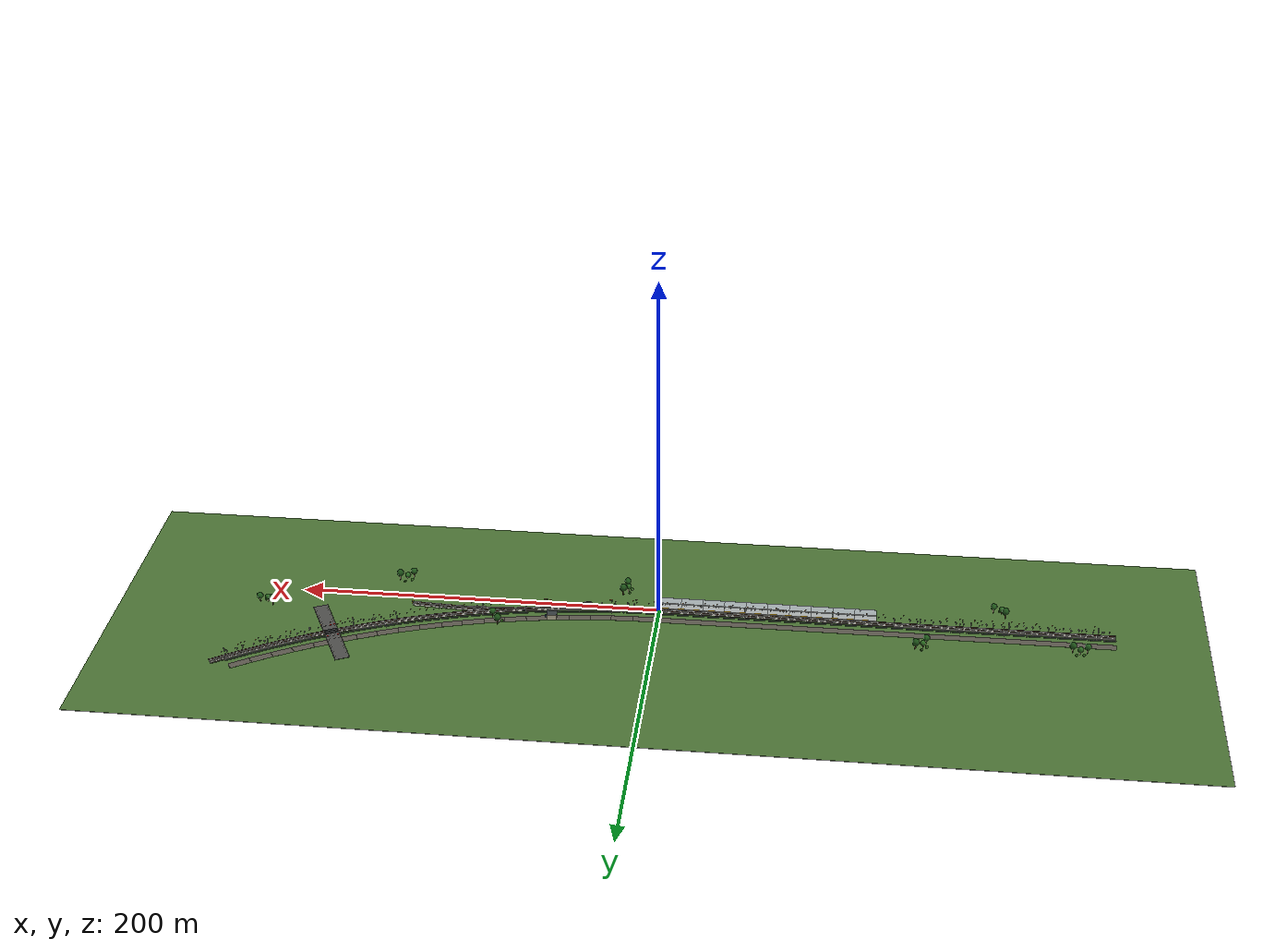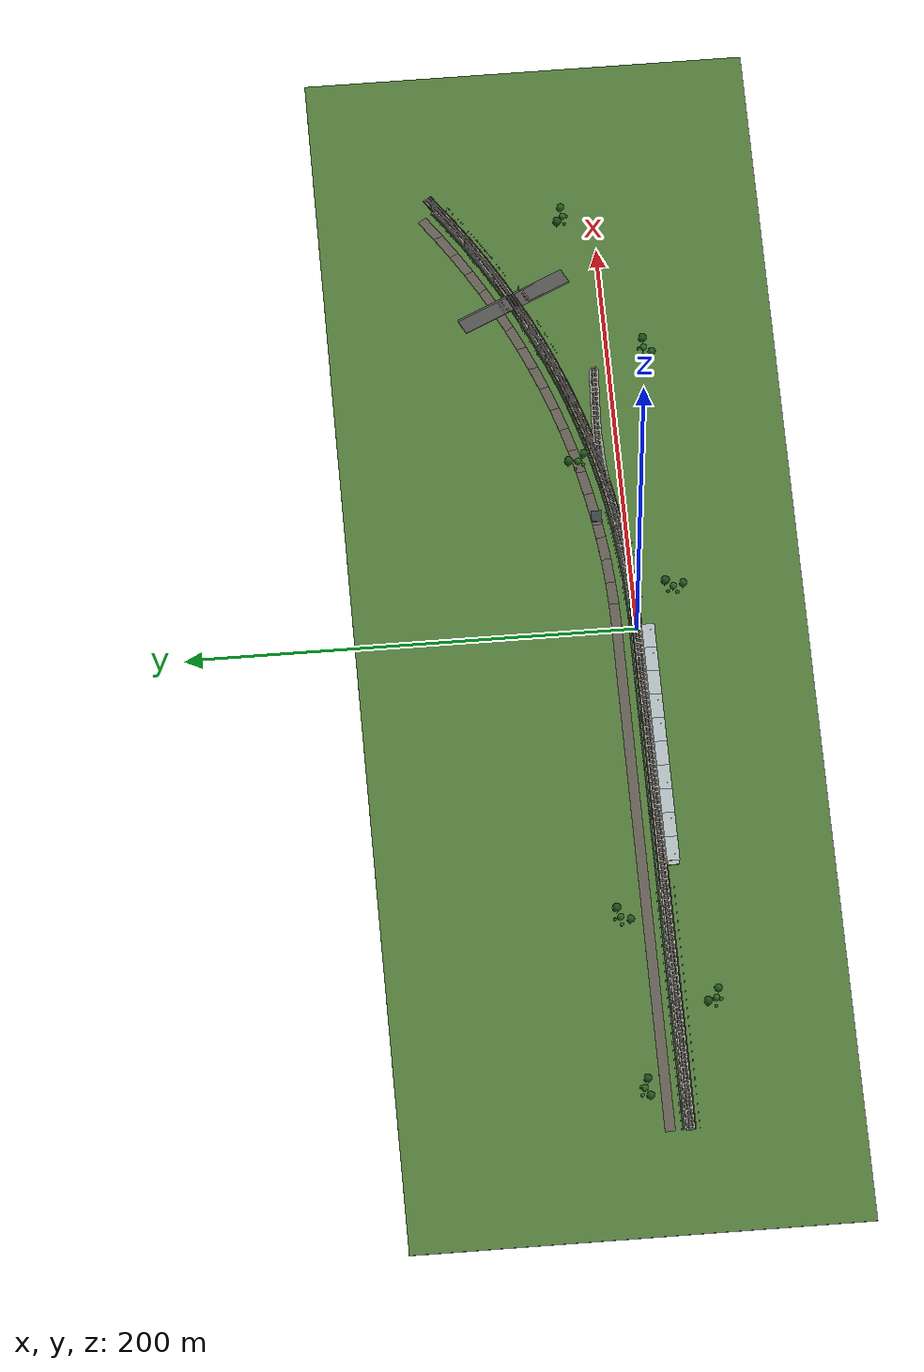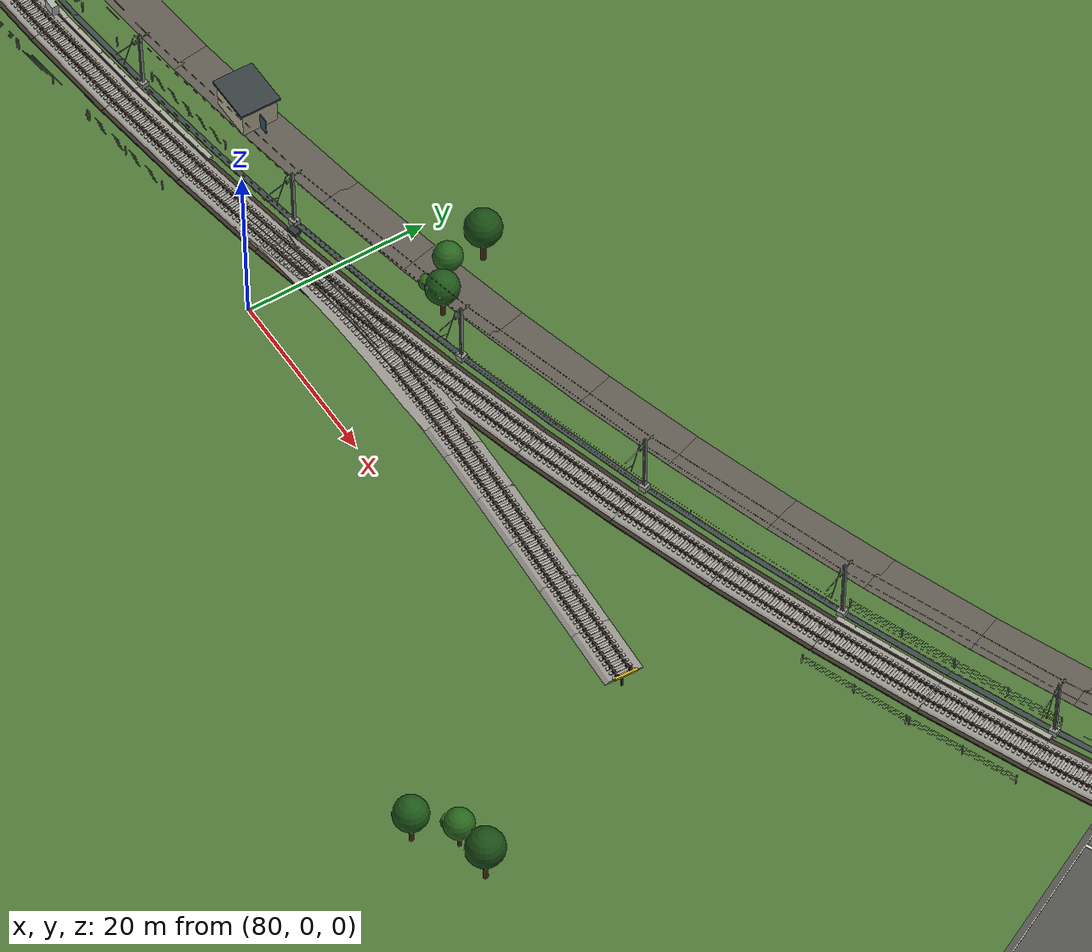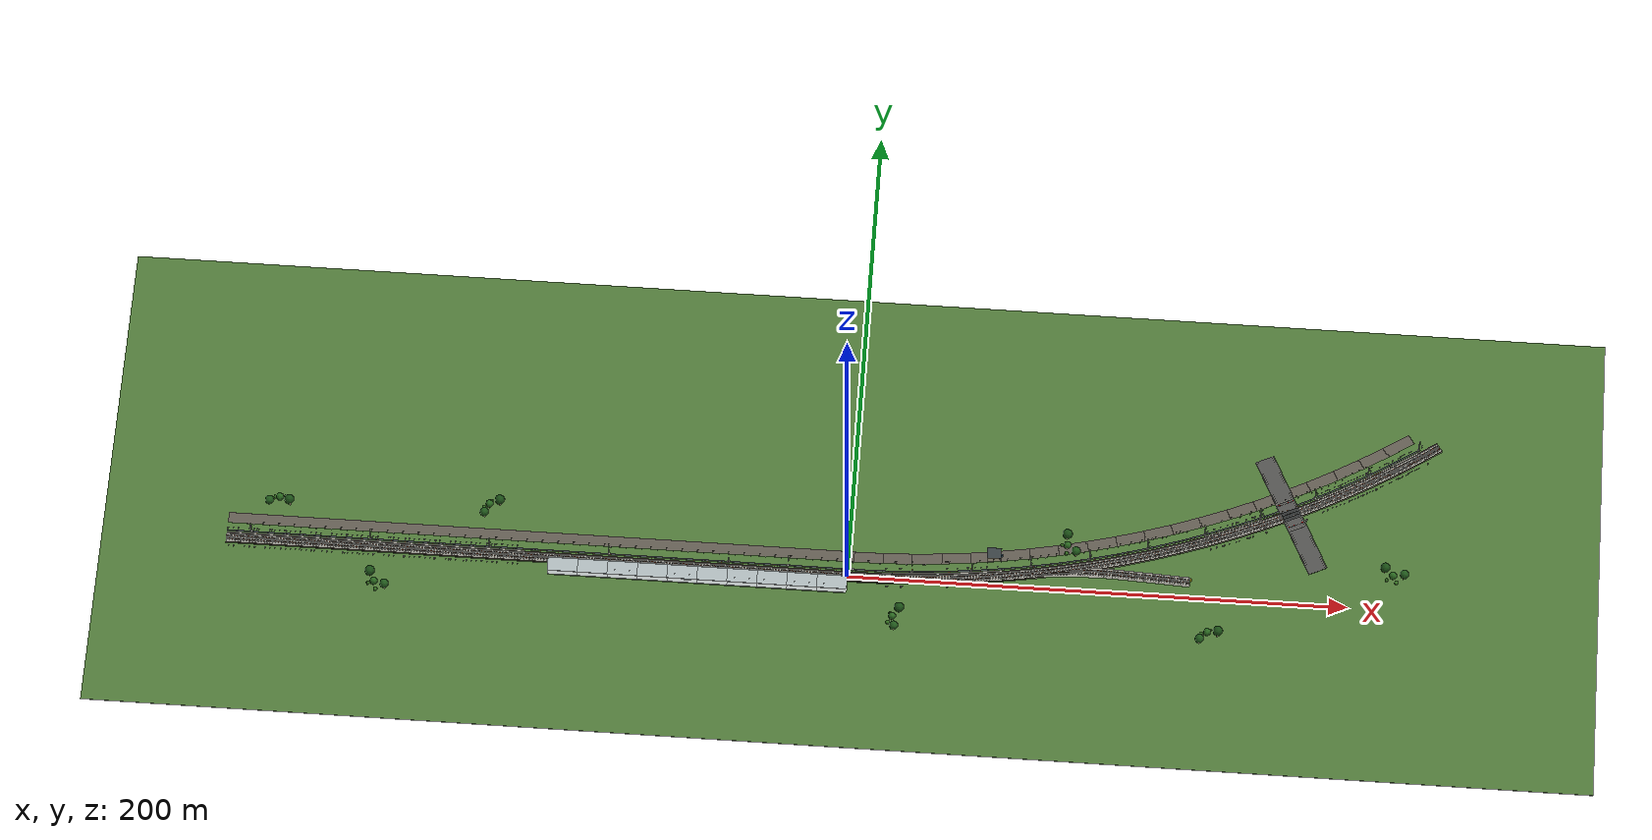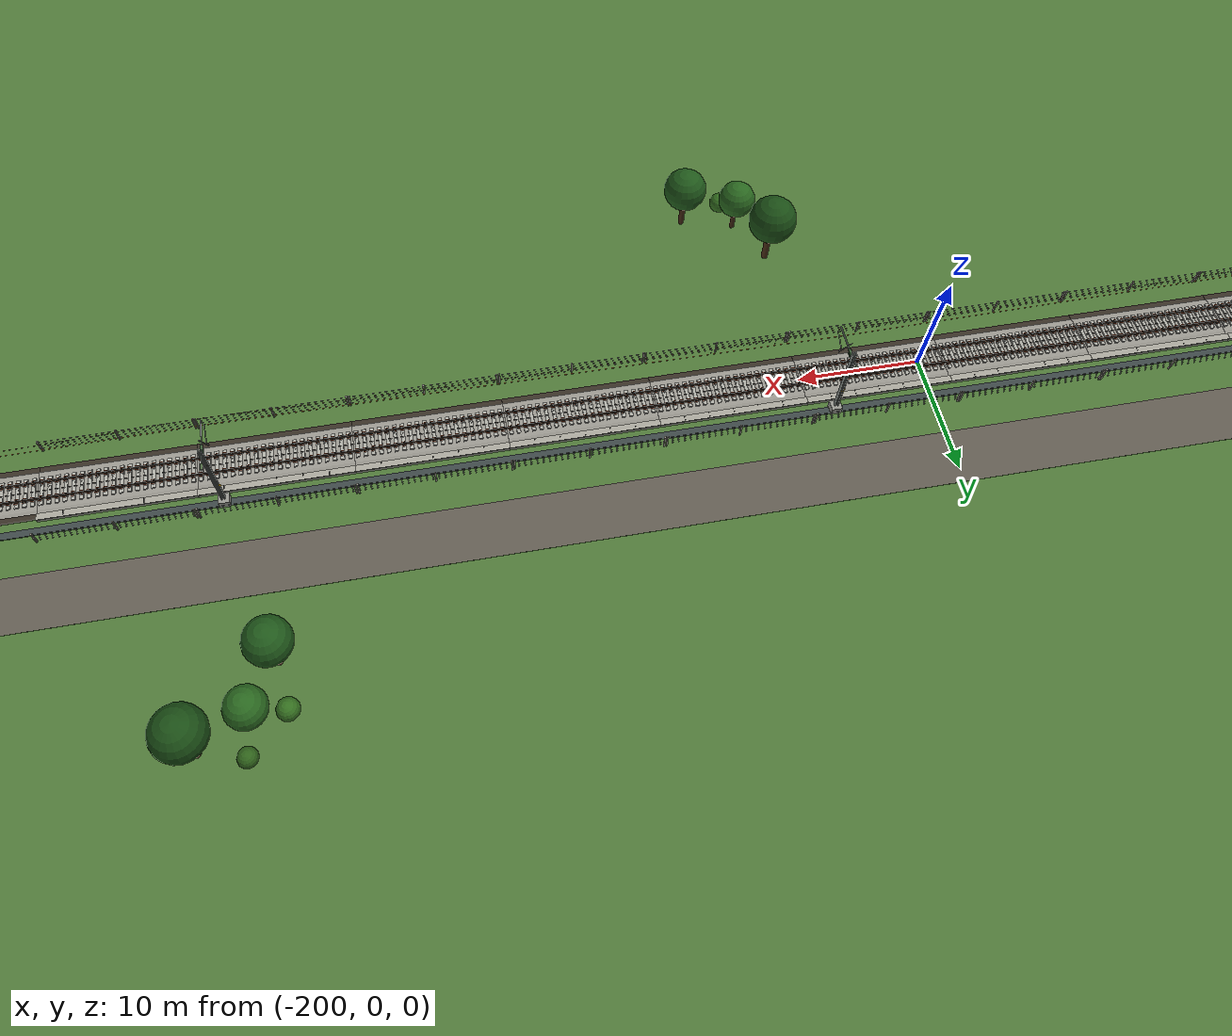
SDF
<sdf version="1.9">
 <world name="railway_environment">
  <physics name="default_physics" type="ignored">
   <max_step_size>0.002</max_step_size>
   <real_time_factor>1.0</real_time_factor>
  </physics>
  <spherical_coordinates>
   <surface_model>EARTH_WGS84</surface_model>
   <world_frame_orientation>ENU</world_frame_orientation>
   <latitude_deg>37.5665</latitude_deg>
   <longitude_deg>126.9780</longitude_deg>
   <elevation>38.0</elevation>
  </spherical_coordinates>
  <plugin filename="gz-sim-physics-system" name="gz::sim::systems::Physics"/>
  <plugin filename="gz-sim-user-commands-system" name="gz::sim::systems::UserCommands"/>
  <plugin filename="gz-sim-scene-broadcaster-system" name="gz::sim::systems::SceneBroadcaster"/>
  <plugin filename="gz-sim-contact-system" name="gz::sim::systems::Contact"/>
  <plugin filename="gz-sim-imu-system" name="gz::sim::systems::Imu"/>
  <plugin filename="gz-sim-air-pressure-system" name="gz::sim::systems::AirPressure"/>
  <plugin filename="gz-sim-navsat-system" name="gz::sim::systems::NavSat"/>
  <plugin filename="gz-sim-sensors-system" name="gz::sim::systems::Sensors">
   <render_engine>ogre2</render_engine>
  </plugin>
  <scene>
   <ambient>0.55 0.58 0.62 1</ambient>
   <background>0.68 0.80 0.92 1</background>
   <shadows>true</shadows>
   <grid>false</grid>
  </scene>
  <light name="sun" type="directional">
   <pose>0 0 80 0 0 0</pose>
   <intensity>1.1</intensity>
   <direction>-0.45 0.25 -0.86</direction>
   <diffuse>0.96 0.94 0.88 1</diffuse>
   <specular>0.25 0.25 0.25 1</specular>
  </light>
  <model name="landscape">
   <static>true</static>
   <link name="ground">
    <collision name="ground_collision">
     <pose>0 25 -0.12 0 0 0</pose>
     <geometry><box><size>600 200 0.20</size></box></geometry>
    </collision>
    <visual name="ground_visual">
     <pose>0 25 -0.12 0 0 0</pose>
     <geometry><box><size>600 200 0.20</size></box></geometry>
     <material><ambient>0.20 0.31 0.14 1</ambient><diffuse>0.31 0.47 0.22 1</diffuse></material>
    </visual>
    <visual name="service_road_tangent">
     <pose>-124 9 0.015 0 0 0</pose>
     <geometry><box><size>252 4.5 0.03</size></box></geometry>
     <material><diffuse>0.38 0.36 0.32 1</diffuse></material>
    </visual>
    <visual name="drainage_tangent">
     <pose>-124 3.25 0.03 0 0 0</pose>
     <geometry><box><size>252 0.60 0.08</size></box></geometry>
     <material><diffuse>0.24 0.28 0.28 1</diffuse></material>
    </visual>
    <visual name="service_road_curve_00">
     <pose>7.8648 9.0440 0.015 0 0 0.015000</pose>
     <geometry><box><size>12.15 4.5 0.03</size></box></geometry>
     <material><diffuse>0.38 0.36 0.32 1</diffuse></material>
    </visual>
    <visual name="drainage_curve_00">
     <pose>7.9510 3.2946 0.03 0 0 0.015000</pose>
     <geometry><box><size>12.15 0.60 0.08</size></box></geometry>
     <material><diffuse>0.24 0.28 0.28 1</diffuse></material>
    </visual>
    <visual name="service_road_curve_01">
     <pose>19.5891 9.3958 0.015 0 0 0.045000</pose>
     <geometry><box><size>12.15 4.5 0.03</size></box></geometry>
     <material><diffuse>0.38 0.36 0.32 1</diffuse></material>
    </visual>
    <visual name="drainage_curve_01">
     <pose>19.8477 3.6516 0.03 0 0 0.045000</pose>
     <geometry><box><size>12.15 0.60 0.08</size></box></geometry>
     <material><diffuse>0.24 0.28 0.28 1</diffuse></material>
    </visual>
    <visual name="service_road_curve_02">
     <pose>31.2975 10.0992 0.015 0 0 0.075000</pose>
     <geometry><box><size>12.15 4.5 0.03</size></box></geometry>
     <material><diffuse>0.38 0.36 0.32 1</diffuse></material>
    </visual>
    <visual name="drainage_curve_02">
     <pose>31.7284 4.3653 0.03 0 0 0.075000</pose>
     <geometry><box><size>12.15 0.60 0.08</size></box></geometry>
     <material><diffuse>0.24 0.28 0.28 1</diffuse></material>
    </visual>
    <visual name="service_road_curve_03">
     <pose>42.9796 11.1534 0.015 0 0 0.105000</pose>
     <geometry><box><size>12.15 4.5 0.03</size></box></geometry>
     <material><diffuse>0.38 0.36 0.32 1</diffuse></material>
    </visual>
    <visual name="drainage_curve_03">
     <pose>43.5822 5.4351 0.03 0 0 0.105000</pose>
     <geometry><box><size>12.15 0.60 0.08</size></box></geometry>
     <material><diffuse>0.24 0.28 0.28 1</diffuse></material>
    </visual>
    <visual name="service_road_curve_04">
     <pose>54.6248 12.5576 0.015 0 0 0.135000</pose>
     <geometry><box><size>12.15 4.5 0.03</size></box></geometry>
     <material><diffuse>0.38 0.36 0.32 1</diffuse></material>
    </visual>
    <visual name="drainage_curve_04">
     <pose>55.3987 6.8599 0.03 0 0 0.135000</pose>
     <geometry><box><size>12.15 0.60 0.08</size></box></geometry>
     <material><diffuse>0.24 0.28 0.28 1</diffuse></material>
    </visual>
    <visual name="service_road_curve_05">
     <pose>66.2227 14.3104 0.015 0 0 0.165000</pose>
     <geometry><box><size>12.15 4.5 0.03</size></box></geometry>
     <material><diffuse>0.38 0.36 0.32 1</diffuse></material>
    </visual>
    <visual name="drainage_curve_05">
     <pose>67.1671 8.6385 0.03 0 0 0.165000</pose>
     <geometry><box><size>12.15 0.60 0.08</size></box></geometry>
     <material><diffuse>0.24 0.28 0.28 1</diffuse></material>
    </visual>
    <visual name="service_road_curve_06">
     <pose>77.7627 16.4104 0.015 0 0 0.195000</pose>
     <geometry><box><size>12.15 4.5 0.03</size></box></geometry>
     <material><diffuse>0.38 0.36 0.32 1</diffuse></material>
    </visual>
    <visual name="drainage_curve_06">
     <pose>78.8769 10.7693 0.03 0 0 0.195000</pose>
     <geometry><box><size>12.15 0.60 0.08</size></box></geometry>
     <material><diffuse>0.24 0.28 0.28 1</diffuse></material>
    </visual>
    <visual name="service_road_curve_07">
     <pose>89.2346 18.8555 0.015 0 0 0.225000</pose>
     <geometry><box><size>12.15 4.5 0.03</size></box></geometry>
     <material><diffuse>0.38 0.36 0.32 1</diffuse></material>
    </visual>
    <visual name="drainage_curve_07">
     <pose>90.5174 13.2504 0.03 0 0 0.225000</pose>
     <geometry><box><size>12.15 0.60 0.08</size></box></geometry>
     <material><diffuse>0.24 0.28 0.28 1</diffuse></material>
    </visual>
    <visual name="service_road_curve_08">
     <pose>100.6280 21.6437 0.015 0 0 0.255000</pose>
     <geometry><box><size>12.15 4.5 0.03</size></box></geometry>
     <material><diffuse>0.38 0.36 0.32 1</diffuse></material>
    </visual>
    <visual name="drainage_curve_08">
     <pose>102.0784 16.0796 0.03 0 0 0.255000</pose>
     <geometry><box><size>12.15 0.60 0.08</size></box></geometry>
     <material><diffuse>0.24 0.28 0.28 1</diffuse></material>
    </visual>
    <visual name="service_road_curve_09">
     <pose>111.9326 24.7723 0.015 0 0 0.285000</pose>
     <geometry><box><size>12.15 4.5 0.03</size></box></geometry>
     <material><diffuse>0.38 0.36 0.32 1</diffuse></material>
    </visual>
    <visual name="drainage_curve_09">
     <pose>113.5492 19.2542 0.03 0 0 0.285000</pose>
     <geometry><box><size>12.15 0.60 0.08</size></box></geometry>
     <material><diffuse>0.24 0.28 0.28 1</diffuse></material>
    </visual>
    <visual name="service_road_curve_10">
     <pose>123.1382 28.2386 0.015 0 0 0.315000</pose>
     <geometry><box><size>12.15 4.5 0.03</size></box></geometry>
     <material><diffuse>0.38 0.36 0.32 1</diffuse></material>
    </visual>
    <visual name="drainage_curve_10">
     <pose>124.9197 22.7715 0.03 0 0 0.315000</pose>
     <geometry><box><size>12.15 0.60 0.08</size></box></geometry>
     <material><diffuse>0.24 0.28 0.28 1</diffuse></material>
    </visual>
    <visual name="service_road_curve_11">
     <pose>134.2349 32.0395 0.015 0 0 0.345000</pose>
     <geometry><box><size>12.15 4.5 0.03</size></box></geometry>
     <material><diffuse>0.38 0.36 0.32 1</diffuse></material>
    </visual>
    <visual name="drainage_curve_11">
     <pose>136.1795 26.6283 0.03 0 0 0.345000</pose>
     <geometry><box><size>12.15 0.60 0.08</size></box></geometry>
     <material><diffuse>0.24 0.28 0.28 1</diffuse></material>
    </visual>
    <visual name="service_road_curve_12">
     <pose>145.2126 36.1715 0.015 0 0 0.375000</pose>
     <geometry><box><size>12.15 4.5 0.03</size></box></geometry>
     <material><diffuse>0.38 0.36 0.32 1</diffuse></material>
    </visual>
    <visual name="drainage_curve_12">
     <pose>147.3186 30.8211 0.03 0 0 0.375000</pose>
     <geometry><box><size>12.15 0.60 0.08</size></box></geometry>
     <material><diffuse>0.24 0.28 0.28 1</diffuse></material>
    </visual>
    <visual name="service_road_curve_13">
     <pose>156.0613 40.6310 0.015 0 0 0.405000</pose>
     <geometry><box><size>12.15 4.5 0.03</size></box></geometry>
     <material><diffuse>0.38 0.36 0.32 1</diffuse></material>
    </visual>
    <visual name="drainage_curve_13">
     <pose>158.3269 35.3461 0.03 0 0 0.405000</pose>
     <geometry><box><size>12.15 0.60 0.08</size></box></geometry>
     <material><diffuse>0.24 0.28 0.28 1</diffuse></material>
    </visual>
    <visual name="service_road_curve_14">
     <pose>166.7715 45.4138 0.015 0 0 0.435000</pose>
     <geometry><box><size>12.15 4.5 0.03</size></box></geometry>
     <material><diffuse>0.38 0.36 0.32 1</diffuse></material>
    </visual>
    <visual name="drainage_curve_14">
     <pose>169.1946 40.1993 0.03 0 0 0.435000</pose>
     <geometry><box><size>12.15 0.60 0.08</size></box></geometry>
     <material><diffuse>0.24 0.28 0.28 1</diffuse></material>
    </visual>
    <visual name="service_road_curve_15">
     <pose>177.3333 50.5158 0.015 0 0 0.465000</pose>
     <geometry><box><size>12.15 4.5 0.03</size></box></geometry>
     <material><diffuse>0.38 0.36 0.32 1</diffuse></material>
    </visual>
    <visual name="drainage_curve_15">
     <pose>179.9117 45.3763 0.03 0 0 0.465000</pose>
     <geometry><box><size>12.15 0.60 0.08</size></box></geometry>
     <material><diffuse>0.24 0.28 0.28 1</diffuse></material>
    </visual>
    <visual name="service_road_curve_16">
     <pose>187.7374 55.9322 0.015 0 0 0.495000</pose>
     <geometry><box><size>12.15 4.5 0.03</size></box></geometry>
     <material><diffuse>0.38 0.36 0.32 1</diffuse></material>
    </visual>
    <visual name="drainage_curve_16">
     <pose>190.4688 50.8724 0.03 0 0 0.495000</pose>
     <geometry><box><size>12.15 0.60 0.08</size></box></geometry>
     <material><diffuse>0.24 0.28 0.28 1</diffuse></material>
    </visual>
    <visual name="service_road_curve_17">
     <pose>197.9743 61.6583 0.015 0 0 0.525000</pose>
     <geometry><box><size>12.15 4.5 0.03</size></box></geometry>
     <material><diffuse>0.38 0.36 0.32 1</diffuse></material>
    </visual>
    <visual name="drainage_curve_17">
     <pose>200.8563 56.6827 0.03 0 0 0.525000</pose>
     <geometry><box><size>12.15 0.60 0.08</size></box></geometry>
     <material><diffuse>0.24 0.28 0.28 1</diffuse></material>
    </visual>
    <visual name="service_road_curve_18">
     <pose>208.0348 67.6889 0.015 0 0 0.555000</pose>
     <geometry><box><size>12.15 4.5 0.03</size></box></geometry>
     <material><diffuse>0.38 0.36 0.32 1</diffuse></material>
    </visual>
    <visual name="drainage_curve_18">
     <pose>211.0648 62.8020 0.03 0 0 0.555000</pose>
     <geometry><box><size>12.15 0.60 0.08</size></box></geometry>
     <material><diffuse>0.24 0.28 0.28 1</diffuse></material>
    </visual>
    <visual name="service_road_curve_19">
     <pose>217.9100 74.0186 0.015 0 0 0.585000</pose>
     <geometry><box><size>12.15 4.5 0.03</size></box></geometry>
     <material><diffuse>0.38 0.36 0.32 1</diffuse></material>
    </visual>
    <visual name="drainage_curve_19">
     <pose>221.0851 69.2247 0.03 0 0 0.585000</pose>
     <geometry><box><size>12.15 0.60 0.08</size></box></geometry>
     <material><diffuse>0.24 0.28 0.28 1</diffuse></material>
    </visual>
   </link>
  </model>
  <include><uri>model://track_12m</uri><name>track_00</name><pose>-244 0 0 0 0 0</pose></include>
  <include><uri>model://track_12m</uri><name>track_01</name><pose>-232 0 0 0 0 0</pose></include>
  <include><uri>model://track_12m</uri><name>track_02</name><pose>-220 0 0 0 0 0</pose></include>
  <include><uri>model://track_12m</uri><name>track_03</name><pose>-208 0 0 0 0 0</pose></include>
  <include><uri>model://track_12m</uri><name>track_04</name><pose>-196 0 0 0 0 0</pose></include>
  <include><uri>model://track_12m</uri><name>track_05</name><pose>-184 0 0 0 0 0</pose></include>
  <include><uri>model://track_12m</uri><name>track_06</name><pose>-172 0 0 0 0 0</pose></include>
  <include><uri>model://track_12m</uri><name>track_07</name><pose>-160 0 0 0 0 0</pose></include>
  <include><uri>model://track_12m</uri><name>track_08</name><pose>-148 0 0 0 0 0</pose></include>
  <include><uri>model://track_12m</uri><name>track_09</name><pose>-136 0 0 0 0 0</pose></include>
  <include><uri>model://track_12m</uri><name>track_10</name><pose>-124 0 0 0 0 0</pose></include>
  <include><uri>model://track_12m</uri><name>track_11</name><pose>-112 0 0 0 0 0</pose></include>
  <include><uri>model://track_12m</uri><name>track_12</name><pose>-100 0 0 0 0 0</pose></include>
  <include><uri>model://track_12m</uri><name>track_13</name><pose>-88 0 0 0 0 0</pose></include>
  <include><uri>model://track_12m</uri><name>track_14</name><pose>-76 0 0 0 0 0</pose></include>
  <include><uri>model://track_12m</uri><name>track_15</name><pose>-64 0 0 0 0 0</pose></include>
  <include><uri>model://track_12m</uri><name>track_16</name><pose>-52 0 0 0 0 0</pose></include>
  <include><uri>model://track_12m</uri><name>track_17</name><pose>-40 0 0 0 0 0</pose></include>
  <include><uri>model://track_12m</uri><name>track_18</name><pose>-28 0 0 0 0 0</pose></include>
  <include><uri>model://track_12m</uri><name>track_19</name><pose>-16 0 0 0 0 0</pose></include>
  <include><uri>model://track_12m</uri><name>track_20</name><pose>-4 0 0 0 0 0</pose></include>
  <include><uri>model://track_12m</uri><name>track_21</name><pose>7.9998 0.0450 0 0 0 0.015000</pose></include>
  <include><uri>model://track_12m</uri><name>track_22</name><pose>19.9939 0.4049 0 0 0 0.045000</pose></include>
  <include><uri>model://track_12m</uri><name>track_23</name><pose>31.9719 1.1245 0 0 0 0.075000</pose></include>
  <include><uri>model://track_12m</uri><name>track_24</name><pose>43.9229 2.2030 0 0 0 0.105000</pose></include>
  <include><uri>model://track_12m</uri><name>track_25</name><pose>55.8361 3.6395 0 0 0 0.135000</pose></include>
  <include><uri>model://track_12m</uri><name>track_26</name><pose>67.7009 5.4327 0 0 0 0.165000</pose></include>
  <include><uri>model://track_12m</uri><name>track_27</name><pose>79.5066 7.5809 0 0 0 0.195000</pose></include>
  <include>
   <uri>model://track_12m</uri>
   <name>track_28</name>
   <pose>91.2425 10.0824 0 0 0 0.225000</pose>
  </include>
  <include>
   <uri>model://track_12m</uri>
   <name>track_29</name>
   <pose>102.8982 12.9347 0 0 0 0.255000</pose>
  </include>
  <include>
   <uri>model://track_12m</uri>
   <name>track_30</name>
   <pose>114.4630 16.1353 0 0 0 0.285000</pose>
  </include>
  <include>
   <uri>model://track_12m</uri>
   <name>track_31</name>
   <pose>125.9266 19.6814 0 0 0 0.315000</pose>
  </include>
  <include>
   <uri>model://track_12m</uri>
   <name>track_32</name>
   <pose>137.2787 23.5698 0 0 0 0.345000</pose>
  </include>
  <include>
   <uri>model://track_12m</uri>
   <name>track_33</name>
   <pose>148.5090 27.7970 0 0 0 0.375000</pose>
  </include>
  <include>
   <uri>model://track_12m</uri>
   <name>track_34</name>
   <pose>159.6075 32.3590 0 0 0 0.405000</pose>
  </include>
  <include>
   <uri>model://track_12m</uri>
   <name>track_35</name>
   <pose>170.5642 37.2520 0 0 0 0.435000</pose>
  </include>
  <include>
   <uri>model://track_12m</uri>
   <name>track_36</name>
   <pose>181.3691 42.4714 0 0 0 0.465000</pose>
  </include>
  <include>
   <uri>model://track_12m</uri>
   <name>track_37</name>
   <pose>192.0127 48.0125 0 0 0 0.495000</pose>
  </include>
  <include>
   <uri>model://track_12m</uri>
   <name>track_38</name>
   <pose>202.4852 53.8704 0 0 0 0.525000</pose>
  </include>
  <include>
   <uri>model://track_12m</uri>
   <name>track_39</name>
   <pose>212.7773 60.0398 0 0 0 0.555000</pose>
  </include>
  <include>
   <uri>model://track_12m</uri>
   <name>track_40</name>
   <pose>222.8798 66.5152 0 0 0 0.585000</pose>
  </include>
  <include>
   <uri>model://track_8m</uri>
   <name>track_41_terminal</name>
   <pose>231.1470 72.1408 0 0 0 0.610000</pose>
  </include>
  <include><uri>model://catenary_span_96m</uri><name>ocs_tangent_00</name><pose>-192 0 0 0 0 0</pose></include>
  <include><uri>model://catenary_span_96m</uri><name>ocs_tangent_01</name><pose>-96 0 0 0 0 0</pose></include>
  <include><uri>model://catenary_span_24m</uri><name>ocs_tangent_02</name><pose>-36 0 0 0 0 0</pose></include>
  <include><uri>model://catenary_span_24m</uri><name>ocs_tangent_03</name><pose>-12 0 0 0 0 0</pose></include>
  <include>
   <uri>model://catenary_span_24m</uri>
   <name>ocs_curve_00</name>
   <pose>13.9982 0.1800 0 0 0 0.030000</pose>
  </include>
  <include>
   <uri>model://catenary_span_24m</uri>
   <name>ocs_curve_01</name>
   <pose>37.9514 1.6189 0 0 0 0.090000</pose>
  </include>
  <include>
   <uri>model://catenary_span_24m</uri>
   <name>ocs_curve_02</name>
   <pose>61.7753 4.4916 0 0 0 0.150000</pose>
  </include>
  <include>
   <uri>model://catenary_span_24m</uri>
   <name>ocs_curve_03</name>
   <pose>85.3840 8.7876 0 0 0 0.210000</pose>
  </include>
  <include>
   <uri>model://catenary_span_24m</uri>
   <name>ocs_curve_04</name>
   <pose>108.6926 14.4916 0 0 0 0.270000</pose>
  </include>
  <include>
   <uri>model://catenary_span_24m</uri>
   <name>ocs_curve_05</name>
   <pose>131.6172 21.5831 0 0 0 0.330000</pose>
  </include>
  <include>
   <uri>model://catenary_span_24m</uri>
   <name>ocs_curve_06</name>
   <pose>154.0754 30.0364 0 0 0 0.390000</pose>
  </include>
  <include>
   <uri>model://catenary_span_24m</uri>
   <name>ocs_curve_07</name>
   <pose>175.9862 39.8212 0 0 0 0.450000</pose>
  </include>
  <include>
   <uri>model://catenary_span_24m</uri>
   <name>ocs_curve_08</name>
   <pose>197.2709 50.9022 0 0 0 0.510000</pose>
  </include>
  <include>
   <uri>model://catenary_span_24m</uri>
   <name>ocs_curve_09</name>
   <pose>217.8528 63.2396 0 0 0 0.570000</pose>
  </include>
  <include>
   <uri>model://catenary_mast</uri>
   <name>ocs_curve_terminal</name>
   <pose>227.8570 69.8658 0 0 0 0.600000</pose>
  </include>
  <include>
   <uri>model://railside_infrastructure_12m</uri>
   <name>infra_00</name>
   <pose>-244 0 0 0 0 0</pose>
  </include>
  <include>
   <uri>model://railside_infrastructure_12m</uri>
   <name>infra_01</name>
   <pose>-232 0 0 0 0 0</pose>
  </include>
  <include>
   <uri>model://railside_infrastructure_12m</uri>
   <name>infra_02</name>
   <pose>-220 0 0 0 0 0</pose>
  </include>
  <include>
   <uri>model://railside_infrastructure_12m</uri>
   <name>infra_03</name>
   <pose>-208 0 0 0 0 0</pose>
  </include>
  <include>
   <uri>model://railside_infrastructure_12m</uri>
   <name>infra_04</name>
   <pose>-196 0 0 0 0 0</pose>
  </include>
  <include>
   <uri>model://railside_infrastructure_12m</uri>
   <name>infra_05</name>
   <pose>-184 0 0 0 0 0</pose>
  </include>
  <include>
   <uri>model://railside_infrastructure_12m</uri>
   <name>infra_06</name>
   <pose>-172 0 0 0 0 0</pose>
  </include>
  <include>
   <uri>model://railside_infrastructure_12m</uri>
   <name>infra_07</name>
   <pose>-160 0 0 0 0 0</pose>
  </include>
  <include>
   <uri>model://railside_infrastructure_12m</uri>
   <name>infra_08</name>
   <pose>-148 0 0 0 0 0</pose>
  </include>
  <include>
   <uri>model://railside_infrastructure_12m</uri>
   <name>infra_09</name>
   <pose>-136 0 0 0 0 0</pose>
  </include>
  <include>
   <uri>model://railside_infrastructure_12m</uri>
   <name>infra_22</name>
   <pose>19.9939 0.4049 0 0 0 0.045000</pose>
  </include>
  <include>
   <uri>model://railside_infrastructure_12m</uri>
   <name>infra_23</name>
   <pose>31.9719 1.1245 0 0 0 0.075000</pose>
  </include>
  <include>
   <uri>model://railside_infrastructure_12m</uri>
   <name>infra_24</name>
   <pose>43.9229 2.2030 0 0 0 0.105000</pose>
  </include>
  <include>
   <uri>model://railside_infrastructure_12m</uri>
   <name>infra_25</name>
   <pose>55.8361 3.6395 0 0 0 0.135000</pose>
  </include>
  <include>
   <uri>model://railside_infrastructure_12m</uri>
   <name>infra_33</name>
   <pose>148.5090 27.7970 0 0 0 0.375000</pose>
  </include>
  <include>
   <uri>model://railside_infrastructure_12m</uri>
   <name>infra_34</name>
   <pose>159.6075 32.3590 0 0 0 0.405000</pose>
  </include>
  <include>
   <uri>model://railside_infrastructure_12m</uri>
   <name>infra_37</name>
   <pose>192.0127 48.0125 0 0 0 0.495000</pose>
  </include>
  <include>
   <uri>model://railside_infrastructure_12m</uri>
   <name>infra_38</name>
   <pose>202.4852 53.8704 0 0 0 0.525000</pose>
  </include>
  <include>
   <uri>model://railside_infrastructure_12m</uri>
   <name>infra_39</name>
   <pose>212.7773 60.0398 0 0 0 0.555000</pose>
  </include>
  <include>
   <uri>model://railside_infrastructure_12m</uri>
   <name>infra_40</name>
   <pose>222.8798 66.5152 0 0 0 0.585000</pose>
  </include>
  <include><uri>model://station_platform_12m</uri><name>platform_00</name><pose>-114 0 0 0 0 0</pose></include>
  <include><uri>model://station_platform_12m</uri><name>platform_01</name><pose>-102 0 0 0 0 0</pose></include>
  <include><uri>model://station_platform_12m</uri><name>platform_02</name><pose>-90 0 0 0 0 0</pose></include>
  <include><uri>model://station_platform_12m</uri><name>platform_03</name><pose>-78 0 0 0 0 0</pose></include>
  <include><uri>model://station_platform_12m</uri><name>platform_04</name><pose>-66 0 0 0 0 0</pose></include>
  <include><uri>model://station_platform_12m</uri><name>platform_05</name><pose>-54 0 0 0 0 0</pose></include>
  <include><uri>model://station_platform_12m</uri><name>platform_06</name><pose>-42 0 0 0 0 0</pose></include>
  <include><uri>model://station_platform_12m</uri><name>platform_07</name><pose>-30 0 0 0 0 0</pose></include>
  <include><uri>model://station_platform_12m</uri><name>platform_08</name><pose>-18 0 0 0 0 0</pose></include>
  <include><uri>model://station_platform_12m</uri><name>platform_09</name><pose>-6 0 0 0 0 0</pose></include>
  <include>
   <uri>model://station_furniture</uri>
   <name>platform_furniture</name>
   <pose>-66 0 0 0 0 0</pose>
  </include>
  <include>
   <uri>model://railway_turnout</uri>
   <name>turnout_and_siding</name>
   <pose>79.5066 7.5809 0 0 0 0.195000</pose>
  </include>
  <include>
   <uri>model://level_crossing</uri>
   <name>level_crossing_east</name>
   <pose>175.9862 39.8212 0 0 0 0.450000</pose>
  </include>
  <model name="signal_equipment">
   <static>true</static>
   <pose>36 3.1 0 0 0 0</pose>
   <plugin filename="gz-sim-label-system" name="gz::sim::systems::Label"><label>40</label></plugin>
   <link name="cabinet">
    <collision name="collision">
     <pose>0 0 0.75 0 0 0</pose>
     <geometry><box><size>1.4 0.8 1.5</size></box></geometry>
    </collision>
    <visual name="body">
     <pose>0 0 0.75 0 0 0</pose>
     <geometry><box><size>1.4 0.8 1.5</size></box></geometry>
     <material><diffuse>0.67 0.70 0.66 1</diffuse></material>
    </visual>
    <visual name="door">
     <pose>-0.705 0 0.75 0 1.570796 0</pose>
     <geometry><box><size>0.70 0.02 1.30</size></box></geometry>
     <material><diffuse>0.40 0.44 0.40 1</diffuse></material>
    </visual>
   </link>
  </model>
  <model name="maintenance_hut">
   <static>true</static>
   <pose>58 13 0 0 0 0</pose>
   <plugin filename="gz-sim-label-system" name="gz::sim::systems::Label"><label>50</label></plugin>
   <link name="hut">
    <collision name="body_collision">
     <pose>0 0 1.5 0 0 0</pose>
     <geometry><box><size>5 4 3</size></box></geometry>
    </collision>
    <visual name="body">
     <pose>0 0 1.5 0 0 0</pose>
     <geometry><box><size>5 4 3</size></box></geometry>
     <material><diffuse>0.72 0.69 0.58 1</diffuse></material>
    </visual>
    <visual name="roof">
     <pose>0 0 3.2 0 0 0</pose>
     <geometry><box><size>5.6 4.6 0.25</size></box></geometry>
     <material><diffuse>0.22 0.25 0.26 1</diffuse></material>
    </visual>
    <visual name="door">
     <pose>2.51 0 1.15 0 1.570796 0</pose>
     <geometry><box><size>1.9 0.08 2.3</size></box></geometry>
     <material><diffuse>0.20 0.32 0.38 1</diffuse></material>
    </visual>
   </link>
  </model>
  <include><uri>model://vegetation_cluster</uri><name>trees_00</name><pose>-230 17 0 0 0 0</pose></include>
  <include><uri>model://vegetation_cluster</uri><name>trees_01</name><pose>-188 -16 0 0 0 2.4</pose></include>
  <include><uri>model://vegetation_cluster</uri><name>trees_02</name><pose>-145 20 0 0 0 0.7</pose></include>
  <include><uri>model://vegetation_cluster</uri><name>trees_03</name><pose>20 -18 0 0 0 1.3</pose></include>
  <include><uri>model://vegetation_cluster</uri><name>trees_04</name><pose>88 19 0 0 0 2.0</pose></include>
  <include><uri>model://vegetation_cluster</uri><name>trees_05</name><pose>145 -17 0 0 0 0.4</pose></include>
  <include><uri>model://vegetation_cluster</uri><name>trees_06</name><pose>218 15 0 0 0 2.8</pose></include>
 </world>
</sdf>

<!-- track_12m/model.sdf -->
<sdf version="1.9">
  <model name="track_12m">
    <static>true</static>
    <plugin filename="gz-sim-label-system" name="gz::sim::systems::Label"><label>10</label></plugin>
    <link name="detailed_track">
      <collision name="formation_collision"><pose>0 0 0.10 0 0 0</pose><geometry><box><size>12 4.2 0.20</size></box></geometry></collision>
      <collision name="rail_left_collision"><pose>0 0.7175 0.535 0 0 0</pose><geometry><box><size>12 0.127 0.153</size></box></geometry></collision>
      <collision name="rail_right_collision"><pose>0 -0.7175 0.535 0 0 0</pose><geometry><box><size>12 0.127 0.153</size></box></geometry></collision>
      <visual name="formation"><pose>0 0 0.08 0 0 0</pose><geometry><box><size>12 4.50 0.16</size></box></geometry><material><diffuse>0.22 0.19 0.15 1</diffuse><pbr><metal><roughness>1.0</roughness><metalness>0</metalness></metal></pbr></material></visual>
      <visual name="ballast_bed"><geometry><mesh><uri>model://track_12m/meshes/ballast_bed.obj</uri></mesh></geometry><material><ambient>0.38 0.38 0.36 1</ambient><diffuse>0.60 0.59 0.56 1</diffuse><pbr><metal><albedo_map>model://track_12m/materials/textures/ballast_albedo.png</albedo_map><roughness>0.98</roughness><metalness>0</metalness></metal></pbr></material></visual>
      <visual name="pc_sleeper_00_concrete"><pose>-5.700 0 0.235 0 0 0</pose><geometry><mesh><uri>model://pc_sleeper/meshes/pc_sleeper_concrete.obj</uri></mesh></geometry><material><ambient>0.47 0.47 0.45 1</ambient><diffuse>0.68 0.68 0.65 1</diffuse><pbr><metal><roughness>0.92</roughness><metalness>0</metalness></metal></pbr></material></visual>
      <visual name="pc_sleeper_00_hardware"><pose>-5.700 0 0.235 0 0 0</pose><geometry><mesh><uri>model://pc_sleeper/meshes/pc_sleeper_hardware.obj</uri></mesh></geometry><material><ambient>0.035 0.038 0.036 1</ambient><diffuse>0.10 0.11 0.10 1</diffuse><specular>0.20 0.20 0.20 1</specular><pbr><metal><roughness>0.66</roughness><metalness>0.28</metalness></metal></pbr></material></visual>
      <visual name="pc_sleeper_00_clips"><pose>-5.700 0 0.235 0 0 0</pose><geometry><mesh><uri>model://pc_sleeper/meshes/pc_sleeper_clips.obj</uri></mesh></geometry><material><ambient>0.16 0.055 0.015 1</ambient><diffuse>0.40 0.14 0.035 1</diffuse><specular>0.24 0.18 0.12 1</specular><pbr><metal><roughness>0.52</roughness><metalness>0.62</metalness></metal></pbr></material></visual>
      <visual name="pc_sleeper_01_concrete"><pose>-5.100 0 0.235 0 0 0</pose><geometry><mesh><uri>model://pc_sleeper/meshes/pc_sleeper_concrete.obj</uri></mesh></geometry><material><ambient>0.47 0.47 0.45 1</ambient><diffuse>0.68 0.68 0.65 1</diffuse><pbr><metal><roughness>0.92</roughness><metalness>0</metalness></metal></pbr></material></visual>
      <visual name="pc_sleeper_01_hardware"><pose>-5.100 0 0.235 0 0 0</pose><geometry><mesh><uri>model://pc_sleeper/meshes/pc_sleeper_hardware.obj</uri></mesh></geometry><material><ambient>0.035 0.038 0.036 1</ambient><diffuse>0.10 0.11 0.10 1</diffuse><specular>0.20 0.20 0.20 1</specular><pbr><metal><roughness>0.66</roughness><metalness>0.28</metalness></metal></pbr></material></visual>
      <visual name="pc_sleeper_01_clips"><pose>-5.100 0 0.235 0 0 0</pose><geometry><mesh><uri>model://pc_sleeper/meshes/pc_sleeper_clips.obj</uri></mesh></geometry><material><ambient>0.16 0.055 0.015 1</ambient><diffuse>0.40 0.14 0.035 1</diffuse><specular>0.24 0.18 0.12 1</specular><pbr><metal><roughness>0.52</roughness><metalness>0.62</metalness></metal></pbr></material></visual>
      <visual name="pc_sleeper_02_concrete"><pose>-4.500 0 0.235 0 0 0</pose><geometry><mesh><uri>model://pc_sleeper/meshes/pc_sleeper_concrete.obj</uri></mesh></geometry><material><ambient>0.47 0.47 0.45 1</ambient><diffuse>0.68 0.68 0.65 1</diffuse><pbr><metal><roughness>0.92</roughness><metalness>0</metalness></metal></pbr></material></visual>
      <visual name="pc_sleeper_02_hardware"><pose>-4.500 0 0.235 0 0 0</pose><geometry><mesh><uri>model://pc_sleeper/meshes/pc_sleeper_hardware.obj</uri></mesh></geometry><material><ambient>0.035 0.038 0.036 1</ambient><diffuse>0.10 0.11 0.10 1</diffuse><specular>0.20 0.20 0.20 1</specular><pbr><metal><roughness>0.66</roughness><metalness>0.28</metalness></metal></pbr></material></visual>
      <visual name="pc_sleeper_02_clips"><pose>-4.500 0 0.235 0 0 0</pose><geometry><mesh><uri>model://pc_sleeper/meshes/pc_sleeper_clips.obj</uri></mesh></geometry><material><ambient>0.16 0.055 0.015 1</ambient><diffuse>0.40 0.14 0.035 1</diffuse><specular>0.24 0.18 0.12 1</specular><pbr><metal><roughness>0.52</roughness><metalness>0.62</metalness></metal></pbr></material></visual>
      <visual name="pc_sleeper_03_concrete"><pose>-3.900 0 0.235 0 0 0</pose><geometry><mesh><uri>model://pc_sleeper/meshes/pc_sleeper_concrete.obj</uri></mesh></geometry><material><ambient>0.47 0.47 0.45 1</ambient><diffuse>0.68 0.68 0.65 1</diffuse><pbr><metal><roughness>0.92</roughness><metalness>0</metalness></metal></pbr></material></visual>
      <visual name="pc_sleeper_03_hardware"><pose>-3.900 0 0.235 0 0 0</pose><geometry><mesh><uri>model://pc_sleeper/meshes/pc_sleeper_hardware.obj</uri></mesh></geometry><material><ambient>0.035 0.038 0.036 1</ambient><diffuse>0.10 0.11 0.10 1</diffuse><specular>0.20 0.20 0.20 1</specular><pbr><metal><roughness>0.66</roughness><metalness>0.28</metalness></metal></pbr></material></visual>
      <visual name="pc_sleeper_03_clips"><pose>-3.900 0 0.235 0 0 0</pose><geometry><mesh><uri>model://pc_sleeper/meshes/pc_sleeper_clips.obj</uri></mesh></geometry><material><ambient>0.16 0.055 0.015 1</ambient><diffuse>0.40 0.14 0.035 1</diffuse><specular>0.24 0.18 0.12 1</specular><pbr><metal><roughness>0.52</roughness><metalness>0.62</metalness></metal></pbr></material></visual>
      <visual name="pc_sleeper_04_concrete"><pose>-3.300 0 0.235 0 0 0</pose><geometry><mesh><uri>model://pc_sleeper/meshes/pc_sleeper_concrete.obj</uri></mesh></geometry><material><ambient>0.47 0.47 0.45 1</ambient><diffuse>0.68 0.68 0.65 1</diffuse><pbr><metal><roughness>0.92</roughness><metalness>0</metalness></metal></pbr></material></visual>
      <visual name="pc_sleeper_04_hardware"><pose>-3.300 0 0.235 0 0 0</pose><geometry><mesh><uri>model://pc_sleeper/meshes/pc_sleeper_hardware.obj</uri></mesh></geometry><material><ambient>0.035 0.038 0.036 1</ambient><diffuse>0.10 0.11 0.10 1</diffuse><specular>0.20 0.20 0.20 1</specular><pbr><metal><roughness>0.66</roughness><metalness>0.28</metalness></metal></pbr></material></visual>
      <visual name="pc_sleeper_04_clips"><pose>-3.300 0 0.235 0 0 0</pose><geometry><mesh><uri>model://pc_sleeper/meshes/pc_sleeper_clips.obj</uri></mesh></geometry><material><ambient>0.16 0.055 0.015 1</ambient><diffuse>0.40 0.14 0.035 1</diffuse><specular>0.24 0.18 0.12 1</specular><pbr><metal><roughness>0.52</roughness><metalness>0.62</metalness></metal></pbr></material></visual>
      <visual name="pc_sleeper_05_concrete"><pose>-2.700 0 0.235 0 0 0</pose><geometry><mesh><uri>model://pc_sleeper/meshes/pc_sleeper_concrete.obj</uri></mesh></geometry><material><ambient>0.47 0.47 0.45 1</ambient><diffuse>0.68 0.68 0.65 1</diffuse><pbr><metal><roughness>0.92</roughness><metalness>0</metalness></metal></pbr></material></visual>
      <visual name="pc_sleeper_05_hardware"><pose>-2.700 0 0.235 0 0 0</pose><geometry><mesh><uri>model://pc_sleeper/meshes/pc_sleeper_hardware.obj</uri></mesh></geometry><material><ambient>0.035 0.038 0.036 1</ambient><diffuse>0.10 0.11 0.10 1</diffuse><specular>0.20 0.20 0.20 1</specular><pbr><metal><roughness>0.66</roughness><metalness>0.28</metalness></metal></pbr></material></visual>
      <visual name="pc_sleeper_05_clips"><pose>-2.700 0 0.235 0 0 0</pose><geometry><mesh><uri>model://pc_sleeper/meshes/pc_sleeper_clips.obj</uri></mesh></geometry><material><ambient>0.16 0.055 0.015 1</ambient><diffuse>0.40 0.14 0.035 1</diffuse><specular>0.24 0.18 0.12 1</specular><pbr><metal><roughness>0.52</roughness><metalness>0.62</metalness></metal></pbr></material></visual>
      <visual name="pc_sleeper_06_concrete"><pose>-2.100 0 0.235 0 0 0</pose><geometry><mesh><uri>model://pc_sleeper/meshes/pc_sleeper_concrete.obj</uri></mesh></geometry><material><ambient>0.47 0.47 0.45 1</ambient><diffuse>0.68 0.68 0.65 1</diffuse><pbr><metal><roughness>0.92</roughness><metalness>0</metalness></metal></pbr></material></visual>
      <visual name="pc_sleeper_06_hardware"><pose>-2.100 0 0.235 0 0 0</pose><geometry><mesh><uri>model://pc_sleeper/meshes/pc_sleeper_hardware.obj</uri></mesh></geometry><material><ambient>0.035 0.038 0.036 1</ambient><diffuse>0.10 0.11 0.10 1</diffuse><specular>0.20 0.20 0.20 1</specular><pbr><metal><roughness>0.66</roughness><metalness>0.28</metalness></metal></pbr></material></visual>
      <visual name="pc_sleeper_06_clips"><pose>-2.100 0 0.235 0 0 0</pose><geometry><mesh><uri>model://pc_sleeper/meshes/pc_sleeper_clips.obj</uri></mesh></geometry><material><ambient>0.16 0.055 0.015 1</ambient><diffuse>0.40 0.14 0.035 1</diffuse><specular>0.24 0.18 0.12 1</specular><pbr><metal><roughness>0.52</roughness><metalness>0.62</metalness></metal></pbr></material></visual>
      <visual name="pc_sleeper_07_concrete"><pose>-1.500 0 0.235 0 0 0</pose><geometry><mesh><uri>model://pc_sleeper/meshes/pc_sleeper_concrete.obj</uri></mesh></geometry><material><ambient>0.47 0.47 0.45 1</ambient><diffuse>0.68 0.68 0.65 1</diffuse><pbr><metal><roughness>0.92</roughness><metalness>0</metalness></metal></pbr></material></visual>
      <visual name="pc_sleeper_07_hardware"><pose>-1.500 0 0.235 0 0 0</pose><geometry><mesh><uri>model://pc_sleeper/meshes/pc_sleeper_hardware.obj</uri></mesh></geometry><material><ambient>0.035 0.038 0.036 1</ambient><diffuse>0.10 0.11 0.10 1</diffuse><specular>0.20 0.20 0.20 1</specular><pbr><metal><roughness>0.66</roughness><metalness>0.28</metalness></metal></pbr></material></visual>
      <visual name="pc_sleeper_07_clips"><pose>-1.500 0 0.235 0 0 0</pose><geometry><mesh><uri>model://pc_sleeper/meshes/pc_sleeper_clips.obj</uri></mesh></geometry><material><ambient>0.16 0.055 0.015 1</ambient><diffuse>0.40 0.14 0.035 1</diffuse><specular>0.24 0.18 0.12 1</specular><pbr><metal><roughness>0.52</roughness><metalness>0.62</metalness></metal></pbr></material></visual>
      <visual name="pc_sleeper_08_concrete"><pose>-0.900 0 0.235 0 0 0</pose><geometry><mesh><uri>model://pc_sleeper/meshes/pc_sleeper_concrete.obj</uri></mesh></geometry><material><ambient>0.47 0.47 0.45 1</ambient><diffuse>0.68 0.68 0.65 1</diffuse><pbr><metal><roughness>0.92</roughness><metalness>0</metalness></metal></pbr></material></visual>
      <visual name="pc_sleeper_08_hardware"><pose>-0.900 0 0.235 0 0 0</pose><geometry><mesh><uri>model://pc_sleeper/meshes/pc_sleeper_hardware.obj</uri></mesh></geometry><material><ambient>0.035 0.038 0.036 1</ambient><diffuse>0.10 0.11 0.10 1</diffuse><specular>0.20 0.20 0.20 1</specular><pbr><metal><roughness>0.66</roughness><metalness>0.28</metalness></metal></pbr></material></visual>
      <visual name="pc_sleeper_08_clips"><pose>-0.900 0 0.235 0 0 0</pose><geometry><mesh><uri>model://pc_sleeper/meshes/pc_sleeper_clips.obj</uri></mesh></geometry><material><ambient>0.16 0.055 0.015 1</ambient><diffuse>0.40 0.14 0.035 1</diffuse><specular>0.24 0.18 0.12 1</specular><pbr><metal><roughness>0.52</roughness><metalness>0.62</metalness></metal></pbr></material></visual>
      <visual name="pc_sleeper_09_concrete"><pose>-0.300 0 0.235 0 0 0</pose><geometry><mesh><uri>model://pc_sleeper/meshes/pc_sleeper_concrete.obj</uri></mesh></geometry><material><ambient>0.47 0.47 0.45 1</ambient><diffuse>0.68 0.68 0.65 1</diffuse><pbr><metal><roughness>0.92</roughness><metalness>0</metalness></metal></pbr></material></visual>
      <visual name="pc_sleeper_09_hardware"><pose>-0.300 0 0.235 0 0 0</pose><geometry><mesh><uri>model://pc_sleeper/meshes/pc_sleeper_hardware.obj</uri></mesh></geometry><material><ambient>0.035 0.038 0.036 1</ambient><diffuse>0.10 0.11 0.10 1</diffuse><specular>0.20 0.20 0.20 1</specular><pbr><metal><roughness>0.66</roughness><metalness>0.28</metalness></metal></pbr></material></visual>
      <visual name="pc_sleeper_09_clips"><pose>-0.300 0 0.235 0 0 0</pose><geometry><mesh><uri>model://pc_sleeper/meshes/pc_sleeper_clips.obj</uri></mesh></geometry><material><ambient>0.16 0.055 0.015 1</ambient><diffuse>0.40 0.14 0.035 1</diffuse><specular>0.24 0.18 0.12 1</specular><pbr><metal><roughness>0.52</roughness><metalness>0.62</metalness></metal></pbr></material></visual>
      <visual name="pc_sleeper_10_concrete"><pose>0.300 0 0.235 0 0 0</pose><geometry><mesh><uri>model://pc_sleeper/meshes/pc_sleeper_concrete.obj</uri></mesh></geometry><material><ambient>0.47 0.47 0.45 1</ambient><diffuse>0.68 0.68 0.65 1</diffuse><pbr><metal><roughness>0.92</roughness><metalness>0</metalness></metal></pbr></material></visual>
      <visual name="pc_sleeper_10_hardware"><pose>0.300 0 0.235 0 0 0</pose><geometry><mesh><uri>model://pc_sleeper/meshes/pc_sleeper_hardware.obj</uri></mesh></geometry><material><ambient>0.035 0.038 0.036 1</ambient><diffuse>0.10 0.11 0.10 1</diffuse><specular>0.20 0.20 0.20 1</specular><pbr><metal><roughness>0.66</roughness><metalness>0.28</metalness></metal></pbr></material></visual>
      <visual name="pc_sleeper_10_clips"><pose>0.300 0 0.235 0 0 0</pose><geometry><mesh><uri>model://pc_sleeper/meshes/pc_sleeper_clips.obj</uri></mesh></geometry><material><ambient>0.16 0.055 0.015 1</ambient><diffuse>0.40 0.14 0.035 1</diffuse><specular>0.24 0.18 0.12 1</specular><pbr><metal><roughness>0.52</roughness><metalness>0.62</metalness></metal></pbr></material></visual>
      <visual name="pc_sleeper_11_concrete"><pose>0.900 0 0.235 0 0 0</pose><geometry><mesh><uri>model://pc_sleeper/meshes/pc_sleeper_concrete.obj</uri></mesh></geometry><material><ambient>0.47 0.47 0.45 1</ambient><diffuse>0.68 0.68 0.65 1</diffuse><pbr><metal><roughness>0.92</roughness><metalness>0</metalness></metal></pbr></material></visual>
      <visual name="pc_sleeper_11_hardware"><pose>0.900 0 0.235 0 0 0</pose><geometry><mesh><uri>model://pc_sleeper/meshes/pc_sleeper_hardware.obj</uri></mesh></geometry><material><ambient>0.035 0.038 0.036 1</ambient><diffuse>0.10 0.11 0.10 1</diffuse><specular>0.20 0.20 0.20 1</specular><pbr><metal><roughness>0.66</roughness><metalness>0.28</metalness></metal></pbr></material></visual>
      <visual name="pc_sleeper_11_clips"><pose>0.900 0 0.235 0 0 0</pose><geometry><mesh><uri>model://pc_sleeper/meshes/pc_sleeper_clips.obj</uri></mesh></geometry><material><ambient>0.16 0.055 0.015 1</ambient><diffuse>0.40 0.14 0.035 1</diffuse><specular>0.24 0.18 0.12 1</specular><pbr><metal><roughness>0.52</roughness><metalness>0.62</metalness></metal></pbr></material></visual>
      <visual name="pc_sleeper_12_concrete"><pose>1.500 0 0.235 0 0 0</pose><geometry><mesh><uri>model://pc_sleeper/meshes/pc_sleeper_concrete.obj</uri></mesh></geometry><material><ambient>0.47 0.47 0.45 1</ambient><diffuse>0.68 0.68 0.65 1</diffuse><pbr><metal><roughness>0.92</roughness><metalness>0</metalness></metal></pbr></material></visual>
      <visual name="pc_sleeper_12_hardware"><pose>1.500 0 0.235 0 0 0</pose><geometry><mesh><uri>model://pc_sleeper/meshes/pc_sleeper_hardware.obj</uri></mesh></geometry><material><ambient>0.035 0.038 0.036 1</ambient><diffuse>0.10 0.11 0.10 1</diffuse><specular>0.20 0.20 0.20 1</specular><pbr><metal><roughness>0.66</roughness><metalness>0.28</metalness></metal></pbr></material></visual>
      <visual name="pc_sleeper_12_clips"><pose>1.500 0 0.235 0 0 0</pose><geometry><mesh><uri>model://pc_sleeper/meshes/pc_sleeper_clips.obj</uri></mesh></geometry><material><ambient>0.16 0.055 0.015 1</ambient><diffuse>0.40 0.14 0.035 1</diffuse><specular>0.24 0.18 0.12 1</specular><pbr><metal><roughness>0.52</roughness><metalness>0.62</metalness></metal></pbr></material></visual>
      <visual name="pc_sleeper_13_concrete"><pose>2.100 0 0.235 0 0 0</pose><geometry><mesh><uri>model://pc_sleeper/meshes/pc_sleeper_concrete.obj</uri></mesh></geometry><material><ambient>0.47 0.47 0.45 1</ambient><diffuse>0.68 0.68 0.65 1</diffuse><pbr><metal><roughness>0.92</roughness><metalness>0</metalness></metal></pbr></material></visual>
      <visual name="pc_sleeper_13_hardware"><pose>2.100 0 0.235 0 0 0</pose><geometry><mesh><uri>model://pc_sleeper/meshes/pc_sleeper_hardware.obj</uri></mesh></geometry><material><ambient>0.035 0.038 0.036 1</ambient><diffuse>0.10 0.11 0.10 1</diffuse><specular>0.20 0.20 0.20 1</specular><pbr><metal><roughness>0.66</roughness><metalness>0.28</metalness></metal></pbr></material></visual>
      <visual name="pc_sleeper_13_clips"><pose>2.100 0 0.235 0 0 0</pose><geometry><mesh><uri>model://pc_sleeper/meshes/pc_sleeper_clips.obj</uri></mesh></geometry><material><ambient>0.16 0.055 0.015 1</ambient><diffuse>0.40 0.14 0.035 1</diffuse><specular>0.24 0.18 0.12 1</specular><pbr><metal><roughness>0.52</roughness><metalness>0.62</metalness></metal></pbr></material></visual>
      <visual name="pc_sleeper_14_concrete"><pose>2.700 0 0.235 0 0 0</pose><geometry><mesh><uri>model://pc_sleeper/meshes/pc_sleeper_concrete.obj</uri></mesh></geometry><material><ambient>0.47 0.47 0.45 1</ambient><diffuse>0.68 0.68 0.65 1</diffuse><pbr><metal><roughness>0.92</roughness><metalness>0</metalness></metal></pbr></material></visual>
      <visual name="pc_sleeper_14_hardware"><pose>2.700 0 0.235 0 0 0</pose><geometry><mesh><uri>model://pc_sleeper/meshes/pc_sleeper_hardware.obj</uri></mesh></geometry><material><ambient>0.035 0.038 0.036 1</ambient><diffuse>0.10 0.11 0.10 1</diffuse><specular>0.20 0.20 0.20 1</specular><pbr><metal><roughness>0.66</roughness><metalness>0.28</metalness></metal></pbr></material></visual>
      <visual name="pc_sleeper_14_clips"><pose>2.700 0 0.235 0 0 0</pose><geometry><mesh><uri>model://pc_sleeper/meshes/pc_sleeper_clips.obj</uri></mesh></geometry><material><ambient>0.16 0.055 0.015 1</ambient><diffuse>0.40 0.14 0.035 1</diffuse><specular>0.24 0.18 0.12 1</specular><pbr><metal><roughness>0.52</roughness><metalness>0.62</metalness></metal></pbr></material></visual>
      <visual name="pc_sleeper_15_concrete"><pose>3.300 0 0.235 0 0 0</pose><geometry><mesh><uri>model://pc_sleeper/meshes/pc_sleeper_concrete.obj</uri></mesh></geometry><material><ambient>0.47 0.47 0.45 1</ambient><diffuse>0.68 0.68 0.65 1</diffuse><pbr><metal><roughness>0.92</roughness><metalness>0</metalness></metal></pbr></material></visual>
      <visual name="pc_sleeper_15_hardware"><pose>3.300 0 0.235 0 0 0</pose><geometry><mesh><uri>model://pc_sleeper/meshes/pc_sleeper_hardware.obj</uri></mesh></geometry><material><ambient>0.035 0.038 0.036 1</ambient><diffuse>0.10 0.11 0.10 1</diffuse><specular>0.20 0.20 0.20 1</specular><pbr><metal><roughness>0.66</roughness><metalness>0.28</metalness></metal></pbr></material></visual>
      <visual name="pc_sleeper_15_clips"><pose>3.300 0 0.235 0 0 0</pose><geometry><mesh><uri>model://pc_sleeper/meshes/pc_sleeper_clips.obj</uri></mesh></geometry><material><ambient>0.16 0.055 0.015 1</ambient><diffuse>0.40 0.14 0.035 1</diffuse><specular>0.24 0.18 0.12 1</specular><pbr><metal><roughness>0.52</roughness><metalness>0.62</metalness></metal></pbr></material></visual>
      <visual name="pc_sleeper_16_concrete"><pose>3.900 0 0.235 0 0 0</pose><geometry><mesh><uri>model://pc_sleeper/meshes/pc_sleeper_concrete.obj</uri></mesh></geometry><material><ambient>0.47 0.47 0.45 1</ambient><diffuse>0.68 0.68 0.65 1</diffuse><pbr><metal><roughness>0.92</roughness><metalness>0</metalness></metal></pbr></material></visual>
      <visual name="pc_sleeper_16_hardware"><pose>3.900 0 0.235 0 0 0</pose><geometry><mesh><uri>model://pc_sleeper/meshes/pc_sleeper_hardware.obj</uri></mesh></geometry><material><ambient>0.035 0.038 0.036 1</ambient><diffuse>0.10 0.11 0.10 1</diffuse><specular>0.20 0.20 0.20 1</specular><pbr><metal><roughness>0.66</roughness><metalness>0.28</metalness></metal></pbr></material></visual>
      <visual name="pc_sleeper_16_clips"><pose>3.900 0 0.235 0 0 0</pose><geometry><mesh><uri>model://pc_sleeper/meshes/pc_sleeper_clips.obj</uri></mesh></geometry><material><ambient>0.16 0.055 0.015 1</ambient><diffuse>0.40 0.14 0.035 1</diffuse><specular>0.24 0.18 0.12 1</specular><pbr><metal><roughness>0.52</roughness><metalness>0.62</metalness></metal></pbr></material></visual>
      <visual name="pc_sleeper_17_concrete"><pose>4.500 0 0.235 0 0 0</pose><geometry><mesh><uri>model://pc_sleeper/meshes/pc_sleeper_concrete.obj</uri></mesh></geometry><material><ambient>0.47 0.47 0.45 1</ambient><diffuse>0.68 0.68 0.65 1</diffuse><pbr><metal><roughness>0.92</roughness><metalness>0</metalness></metal></pbr></material></visual>
      <visual name="pc_sleeper_17_hardware"><pose>4.500 0 0.235 0 0 0</pose><geometry><mesh><uri>model://pc_sleeper/meshes/pc_sleeper_hardware.obj</uri></mesh></geometry><material><ambient>0.035 0.038 0.036 1</ambient><diffuse>0.10 0.11 0.10 1</diffuse><specular>0.20 0.20 0.20 1</specular><pbr><metal><roughness>0.66</roughness><metalness>0.28</metalness></metal></pbr></material></visual>
      <visual name="pc_sleeper_17_clips"><pose>4.500 0 0.235 0 0 0</pose><geometry><mesh><uri>model://pc_sleeper/meshes/pc_sleeper_clips.obj</uri></mesh></geometry><material><ambient>0.16 0.055 0.015 1</ambient><diffuse>0.40 0.14 0.035 1</diffuse><specular>0.24 0.18 0.12 1</specular><pbr><metal><roughness>0.52</roughness><metalness>0.62</metalness></metal></pbr></material></visual>
      <visual name="pc_sleeper_18_concrete"><pose>5.100 0 0.235 0 0 0</pose><geometry><mesh><uri>model://pc_sleeper/meshes/pc_sleeper_concrete.obj</uri></mesh></geometry><material><ambient>0.47 0.47 0.45 1</ambient><diffuse>0.68 0.68 0.65 1</diffuse><pbr><metal><roughness>0.92</roughness><metalness>0</metalness></metal></pbr></material></visual>
      <visual name="pc_sleeper_18_hardware"><pose>5.100 0 0.235 0 0 0</pose><geometry><mesh><uri>model://pc_sleeper/meshes/pc_sleeper_hardware.obj</uri></mesh></geometry><material><ambient>0.035 0.038 0.036 1</ambient><diffuse>0.10 0.11 0.10 1</diffuse><specular>0.20 0.20 0.20 1</specular><pbr><metal><roughness>0.66</roughness><metalness>0.28</metalness></metal></pbr></material></visual>
      <visual name="pc_sleeper_18_clips"><pose>5.100 0 0.235 0 0 0</pose><geometry><mesh><uri>model://pc_sleeper/meshes/pc_sleeper_clips.obj</uri></mesh></geometry><material><ambient>0.16 0.055 0.015 1</ambient><diffuse>0.40 0.14 0.035 1</diffuse><specular>0.24 0.18 0.12 1</specular><pbr><metal><roughness>0.52</roughness><metalness>0.62</metalness></metal></pbr></material></visual>
      <visual name="pc_sleeper_19_concrete"><pose>5.700 0 0.235 0 0 0</pose><geometry><mesh><uri>model://pc_sleeper/meshes/pc_sleeper_concrete.obj</uri></mesh></geometry><material><ambient>0.47 0.47 0.45 1</ambient><diffuse>0.68 0.68 0.65 1</diffuse><pbr><metal><roughness>0.92</roughness><metalness>0</metalness></metal></pbr></material></visual>
      <visual name="pc_sleeper_19_hardware"><pose>5.700 0 0.235 0 0 0</pose><geometry><mesh><uri>model://pc_sleeper/meshes/pc_sleeper_hardware.obj</uri></mesh></geometry><material><ambient>0.035 0.038 0.036 1</ambient><diffuse>0.10 0.11 0.10 1</diffuse><specular>0.20 0.20 0.20 1</specular><pbr><metal><roughness>0.66</roughness><metalness>0.28</metalness></metal></pbr></material></visual>
      <visual name="pc_sleeper_19_clips"><pose>5.700 0 0.235 0 0 0</pose><geometry><mesh><uri>model://pc_sleeper/meshes/pc_sleeper_clips.obj</uri></mesh></geometry><material><ambient>0.16 0.055 0.015 1</ambient><diffuse>0.40 0.14 0.035 1</diffuse><specular>0.24 0.18 0.12 1</specular><pbr><metal><roughness>0.52</roughness><metalness>0.62</metalness></metal></pbr></material></visual>
      <visual name="rail_left_profile"><pose>0 0.7175 0.459 0.025 0 0</pose><geometry><mesh><uri>model://track_12m/meshes/rail_profile_12m.obj</uri></mesh></geometry><material><ambient>0.13 0.09 0.065 1</ambient><diffuse>0.31 0.22 0.16 1</diffuse><specular>0.30 0.25 0.20 1</specular><pbr><metal><roughness>0.48</roughness><metalness>0.72</metalness></metal></pbr></material></visual>
      <visual name="rail_right_profile"><pose>0 -0.7175 0.459 -0.025 0 0</pose><geometry><mesh><uri>model://track_12m/meshes/rail_profile_12m.obj</uri></mesh></geometry><material><ambient>0.13 0.09 0.065 1</ambient><diffuse>0.31 0.22 0.16 1</diffuse><specular>0.30 0.25 0.20 1</specular><pbr><metal><roughness>0.48</roughness><metalness>0.72</metalness></metal></pbr></material></visual>
      <visual name="rail_left_running_band"><pose>0 0.7137 0.6155 0.025 0 0</pose><geometry><box><size>12 0.058 0.006</size></box></geometry><material><ambient>0.42 0.43 0.43 1</ambient><diffuse>0.66 0.67 0.67 1</diffuse><specular>0.92 0.92 0.92 1</specular><pbr><metal><roughness>0.18</roughness><metalness>0.92</metalness></metal></pbr></material></visual>
      <visual name="rail_right_running_band"><pose>0 -0.7137 0.6155 -0.025 0 0</pose><geometry><box><size>12 0.058 0.006</size></box></geometry><material><ambient>0.42 0.43 0.43 1</ambient><diffuse>0.66 0.67 0.67 1</diffuse><specular>0.92 0.92 0.92 1</specular><pbr><metal><roughness>0.18</roughness><metalness>0.92</metalness></metal></pbr></material></visual>
      <visual name="rail_left_gauge_wear"><pose>0 0.6835 0.586 0 0 0</pose><geometry><box><size>12 0.004 0.034</size></box></geometry><material><diffuse>0.47 0.48 0.48 1</diffuse><specular>0.72 0.72 0.72 1</specular></material></visual>
      <visual name="rail_right_gauge_wear"><pose>0 -0.6835 0.586 0 0 0</pose><geometry><box><size>12 0.004 0.034</size></box></geometry><material><diffuse>0.47 0.48 0.48 1</diffuse><specular>0.72 0.72 0.72 1</specular></material></visual>
    </link>
  </model>
</sdf>

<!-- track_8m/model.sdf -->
<sdf version="1.9">
  <model name="track_8m">
    <static>true</static>
    <plugin filename="gz-sim-label-system" name="gz::sim::systems::Label"><label>10</label></plugin>
    <link name="detailed_track">
      <collision name="formation_collision"><pose>0 0 0.10 0 0 0</pose><geometry><box><size>8 4.2 0.20</size></box></geometry></collision>
      <collision name="rail_left_collision"><pose>0 0.7175 0.535 0 0 0</pose><geometry><box><size>8 0.127 0.153</size></box></geometry></collision>
      <collision name="rail_right_collision"><pose>0 -0.7175 0.535 0 0 0</pose><geometry><box><size>8 0.127 0.153</size></box></geometry></collision>
      <visual name="formation"><pose>0 0 0.08 0 0 0</pose><geometry><box><size>8 4.50 0.16</size></box></geometry><material><diffuse>0.22 0.19 0.15 1</diffuse><pbr><metal><roughness>1.0</roughness><metalness>0</metalness></metal></pbr></material></visual>
      <visual name="ballast_bed"><geometry><mesh><uri>model://track_12m/meshes/ballast_bed.obj</uri><scale>0.666667 1 1</scale></mesh></geometry><material><ambient>0.38 0.38 0.36 1</ambient><diffuse>0.60 0.59 0.56 1</diffuse><pbr><metal><albedo_map>model://track_12m/materials/textures/ballast_albedo.png</albedo_map><roughness>0.98</roughness><metalness>0</metalness></metal></pbr></material></visual>
      <visual name="pc_sleeper_00_concrete"><pose>-3.600 0 0.235 0 0 0</pose><geometry><mesh><uri>model://pc_sleeper/meshes/pc_sleeper_concrete.obj</uri></mesh></geometry><material><ambient>0.47 0.47 0.45 1</ambient><diffuse>0.68 0.68 0.65 1</diffuse><pbr><metal><roughness>0.92</roughness><metalness>0</metalness></metal></pbr></material></visual>
      <visual name="pc_sleeper_00_hardware"><pose>-3.600 0 0.235 0 0 0</pose><geometry><mesh><uri>model://pc_sleeper/meshes/pc_sleeper_hardware.obj</uri></mesh></geometry><material><ambient>0.035 0.038 0.036 1</ambient><diffuse>0.10 0.11 0.10 1</diffuse><specular>0.20 0.20 0.20 1</specular><pbr><metal><roughness>0.66</roughness><metalness>0.28</metalness></metal></pbr></material></visual>
      <visual name="pc_sleeper_00_clips"><pose>-3.600 0 0.235 0 0 0</pose><geometry><mesh><uri>model://pc_sleeper/meshes/pc_sleeper_clips.obj</uri></mesh></geometry><material><ambient>0.16 0.055 0.015 1</ambient><diffuse>0.40 0.14 0.035 1</diffuse><specular>0.24 0.18 0.12 1</specular><pbr><metal><roughness>0.52</roughness><metalness>0.62</metalness></metal></pbr></material></visual>
      <visual name="pc_sleeper_01_concrete"><pose>-3.000 0 0.235 0 0 0</pose><geometry><mesh><uri>model://pc_sleeper/meshes/pc_sleeper_concrete.obj</uri></mesh></geometry><material><ambient>0.47 0.47 0.45 1</ambient><diffuse>0.68 0.68 0.65 1</diffuse><pbr><metal><roughness>0.92</roughness><metalness>0</metalness></metal></pbr></material></visual>
      <visual name="pc_sleeper_01_hardware"><pose>-3.000 0 0.235 0 0 0</pose><geometry><mesh><uri>model://pc_sleeper/meshes/pc_sleeper_hardware.obj</uri></mesh></geometry><material><ambient>0.035 0.038 0.036 1</ambient><diffuse>0.10 0.11 0.10 1</diffuse><specular>0.20 0.20 0.20 1</specular><pbr><metal><roughness>0.66</roughness><metalness>0.28</metalness></metal></pbr></material></visual>
      <visual name="pc_sleeper_01_clips"><pose>-3.000 0 0.235 0 0 0</pose><geometry><mesh><uri>model://pc_sleeper/meshes/pc_sleeper_clips.obj</uri></mesh></geometry><material><ambient>0.16 0.055 0.015 1</ambient><diffuse>0.40 0.14 0.035 1</diffuse><specular>0.24 0.18 0.12 1</specular><pbr><metal><roughness>0.52</roughness><metalness>0.62</metalness></metal></pbr></material></visual>
      <visual name="pc_sleeper_02_concrete"><pose>-2.400 0 0.235 0 0 0</pose><geometry><mesh><uri>model://pc_sleeper/meshes/pc_sleeper_concrete.obj</uri></mesh></geometry><material><ambient>0.47 0.47 0.45 1</ambient><diffuse>0.68 0.68 0.65 1</diffuse><pbr><metal><roughness>0.92</roughness><metalness>0</metalness></metal></pbr></material></visual>
      <visual name="pc_sleeper_02_hardware"><pose>-2.400 0 0.235 0 0 0</pose><geometry><mesh><uri>model://pc_sleeper/meshes/pc_sleeper_hardware.obj</uri></mesh></geometry><material><ambient>0.035 0.038 0.036 1</ambient><diffuse>0.10 0.11 0.10 1</diffuse><specular>0.20 0.20 0.20 1</specular><pbr><metal><roughness>0.66</roughness><metalness>0.28</metalness></metal></pbr></material></visual>
      <visual name="pc_sleeper_02_clips"><pose>-2.400 0 0.235 0 0 0</pose><geometry><mesh><uri>model://pc_sleeper/meshes/pc_sleeper_clips.obj</uri></mesh></geometry><material><ambient>0.16 0.055 0.015 1</ambient><diffuse>0.40 0.14 0.035 1</diffuse><specular>0.24 0.18 0.12 1</specular><pbr><metal><roughness>0.52</roughness><metalness>0.62</metalness></metal></pbr></material></visual>
      <visual name="pc_sleeper_03_concrete"><pose>-1.800 0 0.235 0 0 0</pose><geometry><mesh><uri>model://pc_sleeper/meshes/pc_sleeper_concrete.obj</uri></mesh></geometry><material><ambient>0.47 0.47 0.45 1</ambient><diffuse>0.68 0.68 0.65 1</diffuse><pbr><metal><roughness>0.92</roughness><metalness>0</metalness></metal></pbr></material></visual>
      <visual name="pc_sleeper_03_hardware"><pose>-1.800 0 0.235 0 0 0</pose><geometry><mesh><uri>model://pc_sleeper/meshes/pc_sleeper_hardware.obj</uri></mesh></geometry><material><ambient>0.035 0.038 0.036 1</ambient><diffuse>0.10 0.11 0.10 1</diffuse><specular>0.20 0.20 0.20 1</specular><pbr><metal><roughness>0.66</roughness><metalness>0.28</metalness></metal></pbr></material></visual>
      <visual name="pc_sleeper_03_clips"><pose>-1.800 0 0.235 0 0 0</pose><geometry><mesh><uri>model://pc_sleeper/meshes/pc_sleeper_clips.obj</uri></mesh></geometry><material><ambient>0.16 0.055 0.015 1</ambient><diffuse>0.40 0.14 0.035 1</diffuse><specular>0.24 0.18 0.12 1</specular><pbr><metal><roughness>0.52</roughness><metalness>0.62</metalness></metal></pbr></material></visual>
      <visual name="pc_sleeper_04_concrete"><pose>-1.200 0 0.235 0 0 0</pose><geometry><mesh><uri>model://pc_sleeper/meshes/pc_sleeper_concrete.obj</uri></mesh></geometry><material><ambient>0.47 0.47 0.45 1</ambient><diffuse>0.68 0.68 0.65 1</diffuse><pbr><metal><roughness>0.92</roughness><metalness>0</metalness></metal></pbr></material></visual>
      <visual name="pc_sleeper_04_hardware"><pose>-1.200 0 0.235 0 0 0</pose><geometry><mesh><uri>model://pc_sleeper/meshes/pc_sleeper_hardware.obj</uri></mesh></geometry><material><ambient>0.035 0.038 0.036 1</ambient><diffuse>0.10 0.11 0.10 1</diffuse><specular>0.20 0.20 0.20 1</specular><pbr><metal><roughness>0.66</roughness><metalness>0.28</metalness></metal></pbr></material></visual>
      <visual name="pc_sleeper_04_clips"><pose>-1.200 0 0.235 0 0 0</pose><geometry><mesh><uri>model://pc_sleeper/meshes/pc_sleeper_clips.obj</uri></mesh></geometry><material><ambient>0.16 0.055 0.015 1</ambient><diffuse>0.40 0.14 0.035 1</diffuse><specular>0.24 0.18 0.12 1</specular><pbr><metal><roughness>0.52</roughness><metalness>0.62</metalness></metal></pbr></material></visual>
      <visual name="pc_sleeper_05_concrete"><pose>-0.600 0 0.235 0 0 0</pose><geometry><mesh><uri>model://pc_sleeper/meshes/pc_sleeper_concrete.obj</uri></mesh></geometry><material><ambient>0.47 0.47 0.45 1</ambient><diffuse>0.68 0.68 0.65 1</diffuse><pbr><metal><roughness>0.92</roughness><metalness>0</metalness></metal></pbr></material></visual>
      <visual name="pc_sleeper_05_hardware"><pose>-0.600 0 0.235 0 0 0</pose><geometry><mesh><uri>model://pc_sleeper/meshes/pc_sleeper_hardware.obj</uri></mesh></geometry><material><ambient>0.035 0.038 0.036 1</ambient><diffuse>0.10 0.11 0.10 1</diffuse><specular>0.20 0.20 0.20 1</specular><pbr><metal><roughness>0.66</roughness><metalness>0.28</metalness></metal></pbr></material></visual>
      <visual name="pc_sleeper_05_clips"><pose>-0.600 0 0.235 0 0 0</pose><geometry><mesh><uri>model://pc_sleeper/meshes/pc_sleeper_clips.obj</uri></mesh></geometry><material><ambient>0.16 0.055 0.015 1</ambient><diffuse>0.40 0.14 0.035 1</diffuse><specular>0.24 0.18 0.12 1</specular><pbr><metal><roughness>0.52</roughness><metalness>0.62</metalness></metal></pbr></material></visual>
      <visual name="pc_sleeper_06_concrete"><pose>-0.000 0 0.235 0 0 0</pose><geometry><mesh><uri>model://pc_sleeper/meshes/pc_sleeper_concrete.obj</uri></mesh></geometry><material><ambient>0.47 0.47 0.45 1</ambient><diffuse>0.68 0.68 0.65 1</diffuse><pbr><metal><roughness>0.92</roughness><metalness>0</metalness></metal></pbr></material></visual>
      <visual name="pc_sleeper_06_hardware"><pose>-0.000 0 0.235 0 0 0</pose><geometry><mesh><uri>model://pc_sleeper/meshes/pc_sleeper_hardware.obj</uri></mesh></geometry><material><ambient>0.035 0.038 0.036 1</ambient><diffuse>0.10 0.11 0.10 1</diffuse><specular>0.20 0.20 0.20 1</specular><pbr><metal><roughness>0.66</roughness><metalness>0.28</metalness></metal></pbr></material></visual>
      <visual name="pc_sleeper_06_clips"><pose>-0.000 0 0.235 0 0 0</pose><geometry><mesh><uri>model://pc_sleeper/meshes/pc_sleeper_clips.obj</uri></mesh></geometry><material><ambient>0.16 0.055 0.015 1</ambient><diffuse>0.40 0.14 0.035 1</diffuse><specular>0.24 0.18 0.12 1</specular><pbr><metal><roughness>0.52</roughness><metalness>0.62</metalness></metal></pbr></material></visual>
      <visual name="pc_sleeper_07_concrete"><pose>0.600 0 0.235 0 0 0</pose><geometry><mesh><uri>model://pc_sleeper/meshes/pc_sleeper_concrete.obj</uri></mesh></geometry><material><ambient>0.47 0.47 0.45 1</ambient><diffuse>0.68 0.68 0.65 1</diffuse><pbr><metal><roughness>0.92</roughness><metalness>0</metalness></metal></pbr></material></visual>
      <visual name="pc_sleeper_07_hardware"><pose>0.600 0 0.235 0 0 0</pose><geometry><mesh><uri>model://pc_sleeper/meshes/pc_sleeper_hardware.obj</uri></mesh></geometry><material><ambient>0.035 0.038 0.036 1</ambient><diffuse>0.10 0.11 0.10 1</diffuse><specular>0.20 0.20 0.20 1</specular><pbr><metal><roughness>0.66</roughness><metalness>0.28</metalness></metal></pbr></material></visual>
      <visual name="pc_sleeper_07_clips"><pose>0.600 0 0.235 0 0 0</pose><geometry><mesh><uri>model://pc_sleeper/meshes/pc_sleeper_clips.obj</uri></mesh></geometry><material><ambient>0.16 0.055 0.015 1</ambient><diffuse>0.40 0.14 0.035 1</diffuse><specular>0.24 0.18 0.12 1</specular><pbr><metal><roughness>0.52</roughness><metalness>0.62</metalness></metal></pbr></material></visual>
      <visual name="pc_sleeper_08_concrete"><pose>1.200 0 0.235 0 0 0</pose><geometry><mesh><uri>model://pc_sleeper/meshes/pc_sleeper_concrete.obj</uri></mesh></geometry><material><ambient>0.47 0.47 0.45 1</ambient><diffuse>0.68 0.68 0.65 1</diffuse><pbr><metal><roughness>0.92</roughness><metalness>0</metalness></metal></pbr></material></visual>
      <visual name="pc_sleeper_08_hardware"><pose>1.200 0 0.235 0 0 0</pose><geometry><mesh><uri>model://pc_sleeper/meshes/pc_sleeper_hardware.obj</uri></mesh></geometry><material><ambient>0.035 0.038 0.036 1</ambient><diffuse>0.10 0.11 0.10 1</diffuse><specular>0.20 0.20 0.20 1</specular><pbr><metal><roughness>0.66</roughness><metalness>0.28</metalness></metal></pbr></material></visual>
      <visual name="pc_sleeper_08_clips"><pose>1.200 0 0.235 0 0 0</pose><geometry><mesh><uri>model://pc_sleeper/meshes/pc_sleeper_clips.obj</uri></mesh></geometry><material><ambient>0.16 0.055 0.015 1</ambient><diffuse>0.40 0.14 0.035 1</diffuse><specular>0.24 0.18 0.12 1</specular><pbr><metal><roughness>0.52</roughness><metalness>0.62</metalness></metal></pbr></material></visual>
      <visual name="pc_sleeper_09_concrete"><pose>1.800 0 0.235 0 0 0</pose><geometry><mesh><uri>model://pc_sleeper/meshes/pc_sleeper_concrete.obj</uri></mesh></geometry><material><ambient>0.47 0.47 0.45 1</ambient><diffuse>0.68 0.68 0.65 1</diffuse><pbr><metal><roughness>0.92</roughness><metalness>0</metalness></metal></pbr></material></visual>
      <visual name="pc_sleeper_09_hardware"><pose>1.800 0 0.235 0 0 0</pose><geometry><mesh><uri>model://pc_sleeper/meshes/pc_sleeper_hardware.obj</uri></mesh></geometry><material><ambient>0.035 0.038 0.036 1</ambient><diffuse>0.10 0.11 0.10 1</diffuse><specular>0.20 0.20 0.20 1</specular><pbr><metal><roughness>0.66</roughness><metalness>0.28</metalness></metal></pbr></material></visual>
      <visual name="pc_sleeper_09_clips"><pose>1.800 0 0.235 0 0 0</pose><geometry><mesh><uri>model://pc_sleeper/meshes/pc_sleeper_clips.obj</uri></mesh></geometry><material><ambient>0.16 0.055 0.015 1</ambient><diffuse>0.40 0.14 0.035 1</diffuse><specular>0.24 0.18 0.12 1</specular><pbr><metal><roughness>0.52</roughness><metalness>0.62</metalness></metal></pbr></material></visual>
      <visual name="pc_sleeper_10_concrete"><pose>2.400 0 0.235 0 0 0</pose><geometry><mesh><uri>model://pc_sleeper/meshes/pc_sleeper_concrete.obj</uri></mesh></geometry><material><ambient>0.47 0.47 0.45 1</ambient><diffuse>0.68 0.68 0.65 1</diffuse><pbr><metal><roughness>0.92</roughness><metalness>0</metalness></metal></pbr></material></visual>
      <visual name="pc_sleeper_10_hardware"><pose>2.400 0 0.235 0 0 0</pose><geometry><mesh><uri>model://pc_sleeper/meshes/pc_sleeper_hardware.obj</uri></mesh></geometry><material><ambient>0.035 0.038 0.036 1</ambient><diffuse>0.10 0.11 0.10 1</diffuse><specular>0.20 0.20 0.20 1</specular><pbr><metal><roughness>0.66</roughness><metalness>0.28</metalness></metal></pbr></material></visual>
      <visual name="pc_sleeper_10_clips"><pose>2.400 0 0.235 0 0 0</pose><geometry><mesh><uri>model://pc_sleeper/meshes/pc_sleeper_clips.obj</uri></mesh></geometry><material><ambient>0.16 0.055 0.015 1</ambient><diffuse>0.40 0.14 0.035 1</diffuse><specular>0.24 0.18 0.12 1</specular><pbr><metal><roughness>0.52</roughness><metalness>0.62</metalness></metal></pbr></material></visual>
      <visual name="pc_sleeper_11_concrete"><pose>3.000 0 0.235 0 0 0</pose><geometry><mesh><uri>model://pc_sleeper/meshes/pc_sleeper_concrete.obj</uri></mesh></geometry><material><ambient>0.47 0.47 0.45 1</ambient><diffuse>0.68 0.68 0.65 1</diffuse><pbr><metal><roughness>0.92</roughness><metalness>0</metalness></metal></pbr></material></visual>
      <visual name="pc_sleeper_11_hardware"><pose>3.000 0 0.235 0 0 0</pose><geometry><mesh><uri>model://pc_sleeper/meshes/pc_sleeper_hardware.obj</uri></mesh></geometry><material><ambient>0.035 0.038 0.036 1</ambient><diffuse>0.10 0.11 0.10 1</diffuse><specular>0.20 0.20 0.20 1</specular><pbr><metal><roughness>0.66</roughness><metalness>0.28</metalness></metal></pbr></material></visual>
      <visual name="pc_sleeper_11_clips"><pose>3.000 0 0.235 0 0 0</pose><geometry><mesh><uri>model://pc_sleeper/meshes/pc_sleeper_clips.obj</uri></mesh></geometry><material><ambient>0.16 0.055 0.015 1</ambient><diffuse>0.40 0.14 0.035 1</diffuse><specular>0.24 0.18 0.12 1</specular><pbr><metal><roughness>0.52</roughness><metalness>0.62</metalness></metal></pbr></material></visual>
      <visual name="pc_sleeper_12_concrete"><pose>3.600 0 0.235 0 0 0</pose><geometry><mesh><uri>model://pc_sleeper/meshes/pc_sleeper_concrete.obj</uri></mesh></geometry><material><ambient>0.47 0.47 0.45 1</ambient><diffuse>0.68 0.68 0.65 1</diffuse><pbr><metal><roughness>0.92</roughness><metalness>0</metalness></metal></pbr></material></visual>
      <visual name="pc_sleeper_12_hardware"><pose>3.600 0 0.235 0 0 0</pose><geometry><mesh><uri>model://pc_sleeper/meshes/pc_sleeper_hardware.obj</uri></mesh></geometry><material><ambient>0.035 0.038 0.036 1</ambient><diffuse>0.10 0.11 0.10 1</diffuse><specular>0.20 0.20 0.20 1</specular><pbr><metal><roughness>0.66</roughness><metalness>0.28</metalness></metal></pbr></material></visual>
      <visual name="pc_sleeper_12_clips"><pose>3.600 0 0.235 0 0 0</pose><geometry><mesh><uri>model://pc_sleeper/meshes/pc_sleeper_clips.obj</uri></mesh></geometry><material><ambient>0.16 0.055 0.015 1</ambient><diffuse>0.40 0.14 0.035 1</diffuse><specular>0.24 0.18 0.12 1</specular><pbr><metal><roughness>0.52</roughness><metalness>0.62</metalness></metal></pbr></material></visual>
      <visual name="rail_left_profile"><pose>0 0.7175 0.459 0.025 0 0</pose><geometry><mesh><uri>model://track_12m/meshes/rail_profile_12m.obj</uri><scale>0.666667 1 1</scale></mesh></geometry><material><ambient>0.13 0.09 0.065 1</ambient><diffuse>0.31 0.22 0.16 1</diffuse><specular>0.30 0.25 0.20 1</specular><pbr><metal><roughness>0.48</roughness><metalness>0.72</metalness></metal></pbr></material></visual>
      <visual name="rail_right_profile"><pose>0 -0.7175 0.459 -0.025 0 0</pose><geometry><mesh><uri>model://track_12m/meshes/rail_profile_12m.obj</uri><scale>0.666667 1 1</scale></mesh></geometry><material><ambient>0.13 0.09 0.065 1</ambient><diffuse>0.31 0.22 0.16 1</diffuse><specular>0.30 0.25 0.20 1</specular><pbr><metal><roughness>0.48</roughness><metalness>0.72</metalness></metal></pbr></material></visual>
      <visual name="rail_left_running_band"><pose>0 0.7137 0.6155 0.025 0 0</pose><geometry><box><size>8 0.058 0.006</size></box></geometry><material><ambient>0.42 0.43 0.43 1</ambient><diffuse>0.66 0.67 0.67 1</diffuse><specular>0.92 0.92 0.92 1</specular><pbr><metal><roughness>0.18</roughness><metalness>0.92</metalness></metal></pbr></material></visual>
      <visual name="rail_right_running_band"><pose>0 -0.7137 0.6155 -0.025 0 0</pose><geometry><box><size>8 0.058 0.006</size></box></geometry><material><ambient>0.42 0.43 0.43 1</ambient><diffuse>0.66 0.67 0.67 1</diffuse><specular>0.92 0.92 0.92 1</specular><pbr><metal><roughness>0.18</roughness><metalness>0.92</metalness></metal></pbr></material></visual>
      <visual name="rail_left_gauge_wear"><pose>0 0.6835 0.586 0 0 0</pose><geometry><box><size>8 0.004 0.034</size></box></geometry><material><diffuse>0.47 0.48 0.48 1</diffuse><specular>0.72 0.72 0.72 1</specular></material></visual>
      <visual name="rail_right_gauge_wear"><pose>0 -0.6835 0.586 0 0 0</pose><geometry><box><size>8 0.004 0.034</size></box></geometry><material><diffuse>0.47 0.48 0.48 1</diffuse><specular>0.72 0.72 0.72 1</specular></material></visual>
    </link>
  </model>
</sdf>

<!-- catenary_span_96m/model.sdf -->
<sdf version="1.9">
  <model name="catenary_span_96m">
    <static>true</static>
    <plugin filename="gz-sim-label-system" name="gz::sim::systems::Label"><label>30</label></plugin>
    <include><uri>model://catenary_mast</uri><name>mast_left</name><pose>-48 0 0 0 0 0</pose></include>
    <include><uri>model://catenary_mast</uri><name>mast_centre</name><pose>0 0 0 0 0 0</pose></include>
    <link name="conductors">
      <!-- Contact wire: rail top 0.612 m + KR E-03160 nominal 5.200 m. -->
      <visual name="cw_a1"><pose>-42 -0.150 5.812 0 1.570796 0.008333</pose><geometry><cylinder><radius>0.011</radius><length>12.0004</length></cylinder></geometry><material><diffuse>0.58 0.33 0.11 1</diffuse><specular>0.55 0.40 0.20 1</specular></material></visual>
      <visual name="cw_a2"><pose>-30 -0.050 5.812 0 1.570796 0.008333</pose><geometry><cylinder><radius>0.011</radius><length>12.0004</length></cylinder></geometry><material><diffuse>0.58 0.33 0.11 1</diffuse></material></visual>
      <visual name="cw_a3"><pose>-18 0.050 5.812 0 1.570796 0.008333</pose><geometry><cylinder><radius>0.011</radius><length>12.0004</length></cylinder></geometry><material><diffuse>0.58 0.33 0.11 1</diffuse></material></visual>
      <visual name="cw_a4"><pose>-6 0.150 5.812 0 1.570796 0.008333</pose><geometry><cylinder><radius>0.011</radius><length>12.0004</length></cylinder></geometry><material><diffuse>0.58 0.33 0.11 1</diffuse></material></visual>
      <visual name="cw_b1"><pose>6 0.150 5.812 0 1.570796 -0.008333</pose><geometry><cylinder><radius>0.011</radius><length>12.0004</length></cylinder></geometry><material><diffuse>0.58 0.33 0.11 1</diffuse></material></visual>
      <visual name="cw_b2"><pose>18 0.050 5.812 0 1.570796 -0.008333</pose><geometry><cylinder><radius>0.011</radius><length>12.0004</length></cylinder></geometry><material><diffuse>0.58 0.33 0.11 1</diffuse></material></visual>
      <visual name="cw_b3"><pose>30 -0.050 5.812 0 1.570796 -0.008333</pose><geometry><cylinder><radius>0.011</radius><length>12.0004</length></cylinder></geometry><material><diffuse>0.58 0.33 0.11 1</diffuse></material></visual>
      <visual name="cw_b4"><pose>42 -0.150 5.812 0 1.570796 -0.008333</pose><geometry><cylinder><radius>0.011</radius><length>12.0004</length></cylinder></geometry><material><diffuse>0.58 0.33 0.11 1</diffuse></material></visual>

      <!-- Messenger wire approximates the real parabolic sag of a 0.96 m system. -->
      <visual name="mw_a1"><pose>-42 -0.150 6.623 0 1.59567 0.008333</pose><geometry><cylinder><radius>0.010</radius><length>12.004</length></cylinder></geometry><material><diffuse>0.34 0.25 0.15 1</diffuse></material></visual>
      <visual name="mw_a2"><pose>-30 -0.050 6.424 0 1.57909 0.008333</pose><geometry><cylinder><radius>0.010</radius><length>12.001</length></cylinder></geometry><material><diffuse>0.34 0.25 0.15 1</diffuse></material></visual>
      <visual name="mw_a3"><pose>-18 0.050 6.424 0 1.56250 0.008333</pose><geometry><cylinder><radius>0.010</radius><length>12.001</length></cylinder></geometry><material><diffuse>0.34 0.25 0.15 1</diffuse></material></visual>
      <visual name="mw_a4"><pose>-6 0.150 6.623 0 1.54592 0.008333</pose><geometry><cylinder><radius>0.010</radius><length>12.004</length></cylinder></geometry><material><diffuse>0.34 0.25 0.15 1</diffuse></material></visual>
      <visual name="mw_b1"><pose>6 0.150 6.623 0 1.59567 -0.008333</pose><geometry><cylinder><radius>0.010</radius><length>12.004</length></cylinder></geometry><material><diffuse>0.34 0.25 0.15 1</diffuse></material></visual>
      <visual name="mw_b2"><pose>18 0.050 6.424 0 1.57909 -0.008333</pose><geometry><cylinder><radius>0.010</radius><length>12.001</length></cylinder></geometry><material><diffuse>0.34 0.25 0.15 1</diffuse></material></visual>
      <visual name="mw_b3"><pose>30 -0.050 6.424 0 1.56250 -0.008333</pose><geometry><cylinder><radius>0.010</radius><length>12.001</length></cylinder></geometry><material><diffuse>0.34 0.25 0.15 1</diffuse></material></visual>
      <visual name="mw_b4"><pose>42 -0.150 6.623 0 1.54592 -0.008333</pose><geometry><cylinder><radius>0.010</radius><length>12.004</length></cylinder></geometry><material><diffuse>0.34 0.25 0.15 1</diffuse></material></visual>

      <!-- Droppers, nominally 5 m apart. Length follows the messenger sag. -->
      <visual name="da01"><pose>-43 -0.158 6.218 0 0 0</pose><geometry><cylinder><radius>0.006</radius><length>0.812</length></cylinder></geometry><material><diffuse>0.26 0.22 0.17 1</diffuse></material></visual>
      <visual name="da02"><pose>-38 -0.117 6.161 0 0 0</pose><geometry><cylinder><radius>0.006</radius><length>0.697</length></cylinder></geometry><material><diffuse>0.26 0.22 0.17 1</diffuse></material></visual>
      <visual name="da03"><pose>-33 -0.075 6.121 0 0 0</pose><geometry><cylinder><radius>0.006</radius><length>0.618</length></cylinder></geometry><material><diffuse>0.26 0.22 0.17 1</diffuse></material></visual>
      <visual name="da04"><pose>-28 -0.033 6.099 0 0 0</pose><geometry><cylinder><radius>0.006</radius><length>0.573</length></cylinder></geometry><material><diffuse>0.26 0.22 0.17 1</diffuse></material></visual>
      <visual name="da05"><pose>-23 0.008 6.093 0 0 0</pose><geometry><cylinder><radius>0.006</radius><length>0.563</length></cylinder></geometry><material><diffuse>0.26 0.22 0.17 1</diffuse></material></visual>
      <visual name="da06"><pose>-18 0.050 6.105 0 0 0</pose><geometry><cylinder><radius>0.006</radius><length>0.587</length></cylinder></geometry><material><diffuse>0.26 0.22 0.17 1</diffuse></material></visual>
      <visual name="da07"><pose>-13 0.092 6.135 0 0 0</pose><geometry><cylinder><radius>0.006</radius><length>0.646</length></cylinder></geometry><material><diffuse>0.26 0.22 0.17 1</diffuse></material></visual>
      <visual name="da08"><pose>-8 0.133 6.182 0 0 0</pose><geometry><cylinder><radius>0.006</radius><length>0.739</length></cylinder></geometry><material><diffuse>0.26 0.22 0.17 1</diffuse></material></visual>
      <visual name="da09"><pose>-3 0.175 6.245 0 0 0</pose><geometry><cylinder><radius>0.006</radius><length>0.867</length></cylinder></geometry><material><diffuse>0.26 0.22 0.17 1</diffuse></material></visual>
      <visual name="db01"><pose>5 0.158 6.218 0 0 0</pose><geometry><cylinder><radius>0.006</radius><length>0.812</length></cylinder></geometry><material><diffuse>0.26 0.22 0.17 1</diffuse></material></visual>
      <visual name="db02"><pose>10 0.117 6.161 0 0 0</pose><geometry><cylinder><radius>0.006</radius><length>0.697</length></cylinder></geometry><material><diffuse>0.26 0.22 0.17 1</diffuse></material></visual>
      <visual name="db03"><pose>15 0.075 6.121 0 0 0</pose><geometry><cylinder><radius>0.006</radius><length>0.618</length></cylinder></geometry><material><diffuse>0.26 0.22 0.17 1</diffuse></material></visual>
      <visual name="db04"><pose>20 0.033 6.099 0 0 0</pose><geometry><cylinder><radius>0.006</radius><length>0.573</length></cylinder></geometry><material><diffuse>0.26 0.22 0.17 1</diffuse></material></visual>
      <visual name="db05"><pose>25 -0.008 6.093 0 0 0</pose><geometry><cylinder><radius>0.006</radius><length>0.563</length></cylinder></geometry><material><diffuse>0.26 0.22 0.17 1</diffuse></material></visual>
      <visual name="db06"><pose>30 -0.050 6.105 0 0 0</pose><geometry><cylinder><radius>0.006</radius><length>0.587</length></cylinder></geometry><material><diffuse>0.26 0.22 0.17 1</diffuse></material></visual>
      <visual name="db07"><pose>35 -0.092 6.135 0 0 0</pose><geometry><cylinder><radius>0.006</radius><length>0.646</length></cylinder></geometry><material><diffuse>0.26 0.22 0.17 1</diffuse></material></visual>
      <visual name="db08"><pose>40 -0.133 6.182 0 0 0</pose><geometry><cylinder><radius>0.006</radius><length>0.739</length></cylinder></geometry><material><diffuse>0.26 0.22 0.17 1</diffuse></material></visual>
      <visual name="db09"><pose>45 -0.175 6.245 0 0 0</pose><geometry><cylinder><radius>0.006</radius><length>0.867</length></cylinder></geometry><material><diffuse>0.26 0.22 0.17 1</diffuse></material></visual>

      <visual name="feeder"><pose>0 4.15 7.18 0 1.570796 0</pose><geometry><cylinder><radius>0.018</radius><length>96</length></cylinder></geometry><material><diffuse>0.16 0.15 0.13 1</diffuse></material></visual>
      <visual name="protective_wire"><pose>0 3.20 6.82 0 1.570796 0</pose><geometry><cylinder><radius>0.014</radius><length>96</length></cylinder></geometry><material><diffuse>0.18 0.18 0.17 1</diffuse></material></visual>
    </link>
  </model>
</sdf>

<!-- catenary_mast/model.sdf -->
<sdf version="1.9">
  <model name="catenary_mast">
    <static>true</static>
    <plugin filename="gz-sim-label-system" name="gz::sim::systems::Label"><label>30</label></plugin>
    <link name="mast">
      <collision name="foundation_collision"><pose>0 3.20 0.35 0 0 0</pose><geometry><box><size>0.85 0.85 0.70</size></box></geometry></collision>
      <visual name="foundation"><pose>0 3.20 0.35 0 0 0</pose><geometry><box><size>0.85 0.85 0.70</size></box></geometry><material><ambient>0.40 0.40 0.38 1</ambient><diffuse>0.58 0.58 0.55 1</diffuse></material></visual>

      <!-- H-section galvanised steel mast -->
      <visual name="mast_web"><pose>0 3.20 4.05 0 0 0</pose><geometry><box><size>0.055 0.19 7.40</size></box></geometry><material><ambient>0.35 0.37 0.36 1</ambient><diffuse>0.55 0.58 0.56 1</diffuse><specular>0.35 0.35 0.35 1</specular></material></visual>
      <visual name="mast_flange_a"><pose>0.12 3.20 4.05 0 0 0</pose><geometry><box><size>0.055 0.31 7.40</size></box></geometry><material><diffuse>0.53 0.56 0.54 1</diffuse></material></visual>
      <visual name="mast_flange_b"><pose>-0.12 3.20 4.05 0 0 0</pose><geometry><box><size>0.055 0.31 7.40</size></box></geometry><material><diffuse>0.53 0.56 0.54 1</diffuse></material></visual>

      <!-- Cantilever and registration assembly -->
      <visual name="upper_arm"><pose>0 1.70 7.12 0 0 0</pose><geometry><box><size>0.085 3.0 0.085</size></box></geometry><material><diffuse>0.48 0.51 0.49 1</diffuse></material></visual>
      <visual name="diagonal_arm"><pose>0 1.72 6.45 -0.43 0 0</pose><geometry><cylinder><radius>0.038</radius><length>3.28</length></cylinder></geometry><material><diffuse>0.46 0.49 0.47 1</diffuse></material></visual>
      <visual name="upper_insulator"><pose>0 2.65 7.12 1.570796 0 0</pose><geometry><cylinder><radius>0.105</radius><length>0.62</length></cylinder></geometry><material><diffuse>0.23 0.37 0.22 1</diffuse><specular>0.45 0.45 0.45 1</specular></material></visual>
      <visual name="lower_insulator"><pose>0 2.70 6.84 1.570796 0 0</pose><geometry><cylinder><radius>0.090</radius><length>0.52</length></cylinder></geometry><material><diffuse>0.23 0.37 0.22 1</diffuse><specular>0.45 0.45 0.45 1</specular></material></visual>
      <visual name="steady_arm"><pose>0 0.64 5.97 1.12 0 0</pose><geometry><cylinder><radius>0.028</radius><length>1.45</length></cylinder></geometry><material><diffuse>0.46 0.49 0.47 1</diffuse></material></visual>

      <!-- Feeder support and safety marker -->
      <visual name="feeder_bracket"><pose>0 3.85 7.18 1.570796 0 0</pose><geometry><cylinder><radius>0.040</radius><length>1.30</length></cylinder></geometry><material><diffuse>0.47 0.50 0.48 1</diffuse></material></visual>
      <visual name="feeder_insulator"><pose>0 4.15 7.18 1.570796 0 0</pose><geometry><cylinder><radius>0.095</radius><length>0.42</length></cylinder></geometry><material><diffuse>0.31 0.42 0.27 1</diffuse></material></visual>
      <visual name="warning_plate"><pose>-0.151 3.20 2.65 0 1.570796 0</pose><geometry><box><size>0.36 0.018 0.24</size></box></geometry><material><ambient>0.75 0.58 0.04 1</ambient><diffuse>0.92 0.72 0.06 1</diffuse></material></visual>
    </link>
  </model>
</sdf>

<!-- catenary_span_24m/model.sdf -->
<sdf version="1.9">
  <model name="catenary_span_24m">
    <static>true</static>
    <plugin filename="gz-sim-label-system" name="gz::sim::systems::Label"><label>30</label></plugin>
    <include><uri>model://catenary_mast</uri><name>mast_left</name><pose>-12 0 0 0 0 0</pose></include>
    <link name="conductors">
      <visual name="contact"><pose>0 0 5.812 0 1.570796 0</pose><geometry><cylinder><radius>0.011</radius><length>24</length></cylinder></geometry><material><diffuse>0.58 0.33 0.11 1</diffuse><specular>0.55 0.40 0.20 1</specular></material></visual>
      <visual name="messenger_0"><pose>-9 0 6.667 0 1.59162 0</pose><geometry><cylinder><radius>0.010</radius><length>6.001</length></cylinder></geometry><material><diffuse>0.34 0.25 0.15 1</diffuse></material></visual>
      <visual name="messenger_1"><pose>-3 0 6.542 0 1.59162 0</pose><geometry><cylinder><radius>0.010</radius><length>6.001</length></cylinder></geometry><material><diffuse>0.34 0.25 0.15 1</diffuse></material></visual>
      <visual name="messenger_2"><pose>3 0 6.542 0 1.54997 0</pose><geometry><cylinder><radius>0.010</radius><length>6.001</length></cylinder></geometry><material><diffuse>0.34 0.25 0.15 1</diffuse></material></visual>
      <visual name="messenger_3"><pose>9 0 6.667 0 1.54997 0</pose><geometry><cylinder><radius>0.010</radius><length>6.001</length></cylinder></geometry><material><diffuse>0.34 0.25 0.15 1</diffuse></material></visual>
      <visual name="dropper_m8"><pose>-8 0 6.218 0 0 0</pose><geometry><cylinder><radius>0.006</radius><length>0.812</length></cylinder></geometry><material><diffuse>0.26 0.22 0.17 1</diffuse></material></visual>
      <visual name="dropper_m4"><pose>-4 0 6.168 0 0 0</pose><geometry><cylinder><radius>0.006</radius><length>0.712</length></cylinder></geometry><material><diffuse>0.26 0.22 0.17 1</diffuse></material></visual>
      <visual name="dropper_0"><pose>0 0 6.143 0 0 0</pose><geometry><cylinder><radius>0.006</radius><length>0.662</length></cylinder></geometry><material><diffuse>0.26 0.22 0.17 1</diffuse></material></visual>
      <visual name="dropper_p4"><pose>4 0 6.168 0 0 0</pose><geometry><cylinder><radius>0.006</radius><length>0.712</length></cylinder></geometry><material><diffuse>0.26 0.22 0.17 1</diffuse></material></visual>
      <visual name="dropper_p8"><pose>8 0 6.218 0 0 0</pose><geometry><cylinder><radius>0.006</radius><length>0.812</length></cylinder></geometry><material><diffuse>0.26 0.22 0.17 1</diffuse></material></visual>
      <visual name="feeder"><pose>0 4.15 7.18 0 1.570796 0</pose><geometry><cylinder><radius>0.018</radius><length>24</length></cylinder></geometry><material><diffuse>0.16 0.15 0.13 1</diffuse></material></visual>
      <visual name="protective_wire"><pose>0 3.20 6.82 0 1.570796 0</pose><geometry><cylinder><radius>0.014</radius><length>24</length></cylinder></geometry><material><diffuse>0.18 0.18 0.17 1</diffuse></material></visual>
    </link>
  </model>
</sdf>

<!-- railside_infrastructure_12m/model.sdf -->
<sdf version="1.9">
  <model name="railside_infrastructure_12m">
    <static>true</static>
    <plugin filename="gz-sim-label-system" name="gz::sim::systems::Label"><label>40</label></plugin>
    <link name="infrastructure">
      <!-- Precast cable trough on the catenary side -->
      <collision name="trough_collision"><pose>0 2.20 0.18 0 0 0</pose><geometry><box><size>12 0.46 0.36</size></box></geometry></collision>
      <visual name="trough_body"><pose>0 2.20 0.18 0 0 0</pose><geometry><box><size>12 0.46 0.36</size></box></geometry><material><ambient>0.40 0.40 0.38 1</ambient><diffuse>0.58 0.58 0.55 1</diffuse></material></visual>
      <visual name="trough_lid"><pose>0 2.20 0.385 0 0 0</pose><geometry><box><size>12 0.54 0.05</size></box></geometry><material><diffuse>0.66 0.65 0.61 1</diffuse></material></visual>
      <visual name="joint_m4"><pose>-4 2.20 0.413 0 0 0</pose><geometry><box><size>0.018 0.55 0.008</size></box></geometry><material><diffuse>0.15 0.15 0.14 1</diffuse></material></visual>
      <visual name="joint_m2"><pose>-2 2.20 0.413 0 0 0</pose><geometry><box><size>0.018 0.55 0.008</size></box></geometry><material><diffuse>0.15 0.15 0.14 1</diffuse></material></visual>
      <visual name="joint_00"><pose>0 2.20 0.413 0 0 0</pose><geometry><box><size>0.018 0.55 0.008</size></box></geometry><material><diffuse>0.15 0.15 0.14 1</diffuse></material></visual>
      <visual name="joint_p2"><pose>2 2.20 0.413 0 0 0</pose><geometry><box><size>0.018 0.55 0.008</size></box></geometry><material><diffuse>0.15 0.15 0.14 1</diffuse></material></visual>
      <visual name="joint_p4"><pose>4 2.20 0.413 0 0 0</pose><geometry><box><size>0.018 0.55 0.008</size></box></geometry><material><diffuse>0.15 0.15 0.14 1</diffuse></material></visual>

      <!-- Four-strand galvanised rail boundary fence -->
      <visual name="fence_n1"><pose>0 4.15 0.35 0 1.570796 0</pose><geometry><cylinder><radius>0.010</radius><length>12</length></cylinder></geometry><material><diffuse>0.38 0.40 0.39 1</diffuse></material></visual>
      <visual name="fence_n2"><pose>0 4.15 0.65 0 1.570796 0</pose><geometry><cylinder><radius>0.010</radius><length>12</length></cylinder></geometry><material><diffuse>0.38 0.40 0.39 1</diffuse></material></visual>
      <visual name="fence_n3"><pose>0 4.15 0.95 0 1.570796 0</pose><geometry><cylinder><radius>0.010</radius><length>12</length></cylinder></geometry><material><diffuse>0.38 0.40 0.39 1</diffuse></material></visual>
      <visual name="fence_n4"><pose>0 4.15 1.25 0 1.570796 0</pose><geometry><cylinder><radius>0.014</radius><length>12</length></cylinder></geometry><material><diffuse>0.38 0.40 0.39 1</diffuse></material></visual>
      <visual name="fence_s1"><pose>0 -3.85 0.35 0 1.570796 0</pose><geometry><cylinder><radius>0.010</radius><length>12</length></cylinder></geometry><material><diffuse>0.38 0.40 0.39 1</diffuse></material></visual>
      <visual name="fence_s2"><pose>0 -3.85 0.65 0 1.570796 0</pose><geometry><cylinder><radius>0.010</radius><length>12</length></cylinder></geometry><material><diffuse>0.38 0.40 0.39 1</diffuse></material></visual>
      <visual name="fence_s3"><pose>0 -3.85 0.95 0 1.570796 0</pose><geometry><cylinder><radius>0.010</radius><length>12</length></cylinder></geometry><material><diffuse>0.38 0.40 0.39 1</diffuse></material></visual>
      <visual name="fence_s4"><pose>0 -3.85 1.25 0 1.570796 0</pose><geometry><cylinder><radius>0.014</radius><length>12</length></cylinder></geometry><material><diffuse>0.38 0.40 0.39 1</diffuse></material></visual>
      <visual name="post_n_m"><pose>-5.9 4.15 0.68 0 0 0</pose><geometry><box><size>0.12 0.12 1.36</size></box></geometry><material><diffuse>0.59 0.58 0.54 1</diffuse></material></visual>
      <visual name="post_n_0"><pose>0 4.15 0.68 0 0 0</pose><geometry><box><size>0.12 0.12 1.36</size></box></geometry><material><diffuse>0.59 0.58 0.54 1</diffuse></material></visual>
      <visual name="post_n_p"><pose>5.9 4.15 0.68 0 0 0</pose><geometry><box><size>0.12 0.12 1.36</size></box></geometry><material><diffuse>0.59 0.58 0.54 1</diffuse></material></visual>
      <visual name="post_s_m"><pose>-5.9 -3.85 0.68 0 0 0</pose><geometry><box><size>0.12 0.12 1.36</size></box></geometry><material><diffuse>0.59 0.58 0.54 1</diffuse></material></visual>
      <visual name="post_s_0"><pose>0 -3.85 0.68 0 0 0</pose><geometry><box><size>0.12 0.12 1.36</size></box></geometry><material><diffuse>0.59 0.58 0.54 1</diffuse></material></visual>
      <visual name="post_s_p"><pose>5.9 -3.85 0.68 0 0 0</pose><geometry><box><size>0.12 0.12 1.36</size></box></geometry><material><diffuse>0.59 0.58 0.54 1</diffuse></material></visual>
    </link>
  </model>
</sdf>

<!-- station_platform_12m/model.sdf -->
<sdf version="1.9">
  <model name="station_platform_12m">
    <static>true</static>
    <plugin filename="gz-sim-label-system" name="gz::sim::systems::Label"><label>20</label></plugin>
    <link name="platform">
      <collision name="slab_collision"><pose>0 -4.55 0.29 0 0 0</pose><geometry><box><size>12 5.5 0.58</size></box></geometry></collision>
      <visual name="slab"><pose>0 -4.55 0.29 0 0 0</pose><geometry><box><size>12 5.5 0.58</size></box></geometry><material><diffuse>0.70 0.72 0.72 1</diffuse><pbr><metal><albedo_map>model://station_platform_12m/materials/textures/platform_concrete_albedo.png</albedo_map><roughness>0.94</roughness><metalness>0</metalness></metal></pbr></material></visual>
      <visual name="edge_fascia"><pose>0 -1.79 0.32 0 0 0</pose><geometry><box><size>12 0.10 0.64</size></box></geometry><material><diffuse>0.76 0.77 0.75 1</diffuse></material></visual>
      <visual name="tactile_yellow"><pose>0 -2.20 0.591 0 0 0</pose><geometry><box><size>12 0.34 0.022</size></box></geometry><material><ambient>0.75 0.54 0.02 1</ambient><diffuse>0.96 0.71 0.04 1</diffuse><pbr><metal><roughness>0.8</roughness><metalness>0</metalness></metal></pbr></material></visual>
      <visual name="safety_line"><pose>0 -1.92 0.594 0 0 0</pose><geometry><box><size>12 0.055 0.026</size></box></geometry><material><diffuse>0.90 0.89 0.80 1</diffuse></material></visual>
      <collision name="column_left_collision"><pose>-3 -5.58 2.43 0 0 0</pose><geometry><box><size>0.22 0.22 3.68</size></box></geometry></collision>
      <collision name="column_right_collision"><pose>3 -5.58 2.43 0 0 0</pose><geometry><box><size>0.22 0.22 3.68</size></box></geometry></collision>
      <visual name="column_left"><pose>-3 -5.58 2.43 0 0 0</pose><geometry><box><size>0.22 0.22 3.68</size></box></geometry><material><diffuse>0.78 0.80 0.80 1</diffuse><pbr><metal><roughness>0.34</roughness><metalness>0.72</metalness></metal></pbr></material></visual>
      <visual name="column_right"><pose>3 -5.58 2.43 0 0 0</pose><geometry><box><size>0.22 0.22 3.68</size></box></geometry><material><diffuse>0.78 0.80 0.80 1</diffuse><pbr><metal><roughness>0.34</roughness><metalness>0.72</metalness></metal></pbr></material></visual>
      <visual name="roof"><pose>0 -4.55 4.20 0.028 0 0</pose><geometry><box><size>12 5.75 0.15</size></box></geometry><material><diffuse>0.68 0.72 0.73 1</diffuse><pbr><metal><roughness>0.44</roughness><metalness>0.58</metalness></metal></pbr></material></visual>
      <visual name="roof_edge"><pose>0 -1.69 4.28 0 0 0</pose><geometry><box><size>12 0.15 0.36</size></box></geometry><material><diffuse>0.90 0.91 0.89 1</diffuse></material></visual>
      <visual name="beam_left"><pose>-3 -4.55 4.00 0 0 0</pose><geometry><box><size>0.20 5.3 0.24</size></box></geometry><material><diffuse>0.38 0.42 0.43 1</diffuse></material></visual>
      <visual name="beam_right"><pose>3 -4.55 4.00 0 0 0</pose><geometry><box><size>0.20 5.3 0.24</size></box></geometry><material><diffuse>0.38 0.42 0.43 1</diffuse></material></visual>
      <visual name="light_a"><pose>-3 -3.65 3.93 0 0 0</pose><geometry><box><size>2.2 0.16 0.05</size></box></geometry><material><emissive>0.92 0.95 0.90 1</emissive><diffuse>0.92 0.95 0.90 1</diffuse></material></visual>
      <visual name="light_b"><pose>3 -3.65 3.93 0 0 0</pose><geometry><box><size>2.2 0.16 0.05</size></box></geometry><material><emissive>0.92 0.95 0.90 1</emissive><diffuse>0.92 0.95 0.90 1</diffuse></material></visual>
    </link>
  </model>
</sdf>

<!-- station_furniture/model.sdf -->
<sdf version="1.9">
  <model name="station_furniture">
    <static>true</static>
    <plugin filename="gz-sim-label-system" name="gz::sim::systems::Label"><label>21</label></plugin>
    <link name="furniture">
      <visual name="bench_seat"><pose>-2 -5.35 1.04 0 0 0</pose><geometry><box><size>2.8 0.55 0.10</size></box></geometry><material><diffuse>0.48 0.36 0.23 1</diffuse><pbr><metal><roughness>0.65</roughness><metalness>0.05</metalness></metal></pbr></material></visual>
      <visual name="bench_back"><pose>-2 -5.62 1.48 -0.15 0 0</pose><geometry><box><size>2.8 0.09 0.75</size></box></geometry><material><diffuse>0.48 0.36 0.23 1</diffuse></material></visual>
      <visual name="bench_leg_l"><pose>-3 -5.35 0.80 0 0 0</pose><geometry><box><size>0.10 0.48 0.44</size></box></geometry><material><diffuse>0.20 0.22 0.23 1</diffuse></material></visual>
      <visual name="bench_leg_r"><pose>-1 -5.35 0.80 0 0 0</pose><geometry><box><size>0.10 0.48 0.44</size></box></geometry><material><diffuse>0.20 0.22 0.23 1</diffuse></material></visual>
      <visual name="glass_a"><pose>2.4 -6.35 2.18 0 0 0</pose><geometry><box><size>2.8 0.045 2.55</size></box></geometry><material><ambient>0.30 0.48 0.52 0.34</ambient><diffuse>0.45 0.68 0.72 0.30</diffuse><specular>0.8 0.8 0.8 1</specular></material><transparency>0.68</transparency></visual>
      <visual name="glass_post_l"><pose>0.95 -6.35 2.18 0 0 0</pose><geometry><box><size>0.09 0.10 2.65</size></box></geometry><material><diffuse>0.72 0.75 0.75 1</diffuse></material></visual>
      <visual name="glass_post_r"><pose>3.85 -6.35 2.18 0 0 0</pose><geometry><box><size>0.09 0.10 2.65</size></box></geometry><material><diffuse>0.72 0.75 0.75 1</diffuse></material></visual>
      <visual name="sign_post"><pose>0 -4.40 2.70 0 0 0</pose><geometry><cylinder><radius>0.045</radius><length>2.7</length></cylinder></geometry><material><diffuse>0.25 0.27 0.28 1</diffuse></material></visual>
      <visual name="station_sign"><pose>0 -4.40 3.50 0 0 0</pose><geometry><box><size>2.25 0.10 0.66</size></box></geometry><material><diffuse>0.05 0.23 0.55 1</diffuse></material></visual>
      <visual name="sign_white_band"><pose>0 -4.34 3.50 0 0 0</pose><geometry><box><size>1.82 0.025 0.23</size></box></geometry><material><diffuse>0.94 0.95 0.93 1</diffuse></material></visual>
      <visual name="led_board"><pose>3.5 -3.50 3.43 0 0 0</pose><geometry><box><size>3.8 0.12 0.72</size></box></geometry><material><diffuse>0.025 0.032 0.030 1</diffuse></material></visual>
      <visual name="led_green"><pose>3.5 -3.43 3.43 0 0 0</pose><geometry><box><size>3.30 0.02 0.08</size></box></geometry><material><emissive>0.08 0.82 0.23 1</emissive><diffuse>0.08 0.82 0.23 1</diffuse></material></visual>
      <visual name="bin"><pose>-4.5 -5.7 0.95 0 0 0</pose><geometry><box><size>0.52 0.52 0.78</size></box></geometry><material><diffuse>0.20 0.23 0.24 1</diffuse></material></visual>
    </link>
  </model>
</sdf>

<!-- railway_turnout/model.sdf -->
<sdf version="1.9">
  <model name="railway_turnout">
    <static>true</static>
    <plugin filename="gz-sim-label-system" name="gz::sim::systems::Label">
      <label>10</label>
    </plugin>
    <link name="turnout_rails_and_ballast">
      <visual name="ballast_transition">
        <geometry>
          <mesh>
            <uri>model://railway_turnout/meshes/ballast_transition.obj</uri>
          </mesh>
        </geometry>
        <material>
          <ambient>0.38 0.38 0.36 1</ambient>
          <diffuse>0.60 0.59 0.56 1</diffuse>
          <pbr>
            <metal>
              <albedo_map>model://track_12m/materials/textures/ballast_albedo.png</albedo_map>
              <roughness>0.98</roughness>
              <metalness>0</metalness>
            </metal>
          </pbr>
        </material>
      </visual>
      <visual name="transition_sleeper_00">
        <pose>-5.700 -0.0390 0.235 0 0 0</pose>
        <geometry>
          <mesh>
            <uri>model://pc_sleeper/meshes/pc_sleeper_concrete.obj</uri>
            <scale>1 1.032465 1</scale>
          </mesh>
        </geometry>
        <material>
          <ambient>0.47 0.47 0.45 1</ambient>
          <diffuse>0.68 0.68 0.65 1</diffuse>
          <pbr>
            <metal>
              <roughness>0.92</roughness>
              <metalness>0</metalness>
            </metal>
          </pbr>
        </material>
      </visual>
      <visual name="transition_sleeper_01">
        <pose>-5.100 -0.0477 0.235 0 0 0</pose>
        <geometry>
          <mesh>
            <uri>model://pc_sleeper/meshes/pc_sleeper_concrete.obj</uri>
            <scale>1 1.039757 1</scale>
          </mesh>
        </geometry>
        <material>
          <ambient>0.47 0.47 0.45 1</ambient>
          <diffuse>0.68 0.68 0.65 1</diffuse>
          <pbr>
            <metal>
              <roughness>0.92</roughness>
              <metalness>0</metalness>
            </metal>
          </pbr>
        </material>
      </visual>
      <visual name="transition_sleeper_02">
        <pose>-4.500 -0.0565 0.235 0 0 0</pose>
        <geometry>
          <mesh>
            <uri>model://pc_sleeper/meshes/pc_sleeper_concrete.obj</uri>
            <scale>1 1.047049 1</scale>
          </mesh>
        </geometry>
        <material>
          <ambient>0.47 0.47 0.45 1</ambient>
          <diffuse>0.68 0.68 0.65 1</diffuse>
          <pbr>
            <metal>
              <roughness>0.92</roughness>
              <metalness>0</metalness>
            </metal>
          </pbr>
        </material>
      </visual>
      <visual name="transition_sleeper_03">
        <pose>-3.900 -0.0652 0.235 0 0 0</pose>
        <geometry>
          <mesh>
            <uri>model://pc_sleeper/meshes/pc_sleeper_concrete.obj</uri>
            <scale>1 1.054340 1</scale>
          </mesh>
        </geometry>
        <material>
          <ambient>0.47 0.47 0.45 1</ambient>
          <diffuse>0.68 0.68 0.65 1</diffuse>
          <pbr>
            <metal>
              <roughness>0.92</roughness>
              <metalness>0</metalness>
            </metal>
          </pbr>
        </material>
      </visual>
      <visual name="transition_sleeper_04">
        <pose>-3.300 -0.0740 0.235 0 0 0</pose>
        <geometry>
          <mesh>
            <uri>model://pc_sleeper/meshes/pc_sleeper_concrete.obj</uri>
            <scale>1 1.061632 1</scale>
          </mesh>
        </geometry>
        <material>
          <ambient>0.47 0.47 0.45 1</ambient>
          <diffuse>0.68 0.68 0.65 1</diffuse>
          <pbr>
            <metal>
              <roughness>0.92</roughness>
              <metalness>0</metalness>
            </metal>
          </pbr>
        </material>
      </visual>
      <visual name="transition_sleeper_05">
        <pose>-2.700 -0.0827 0.235 0 0 0</pose>
        <geometry>
          <mesh>
            <uri>model://pc_sleeper/meshes/pc_sleeper_concrete.obj</uri>
            <scale>1 1.068924 1</scale>
          </mesh>
        </geometry>
        <material>
          <ambient>0.47 0.47 0.45 1</ambient>
          <diffuse>0.68 0.68 0.65 1</diffuse>
          <pbr>
            <metal>
              <roughness>0.92</roughness>
              <metalness>0</metalness>
            </metal>
          </pbr>
        </material>
      </visual>
      <visual name="transition_sleeper_06">
        <pose>-2.100 -0.0915 0.235 0 0 0</pose>
        <geometry>
          <mesh>
            <uri>model://pc_sleeper/meshes/pc_sleeper_concrete.obj</uri>
            <scale>1 1.076215 1</scale>
          </mesh>
        </geometry>
        <material>
          <ambient>0.47 0.47 0.45 1</ambient>
          <diffuse>0.68 0.68 0.65 1</diffuse>
          <pbr>
            <metal>
              <roughness>0.92</roughness>
              <metalness>0</metalness>
            </metal>
          </pbr>
        </material>
      </visual>
      <visual name="transition_sleeper_07">
        <pose>-1.500 -0.1002 0.235 0 0 0</pose>
        <geometry>
          <mesh>
            <uri>model://pc_sleeper/meshes/pc_sleeper_concrete.obj</uri>
            <scale>1 1.083507 1</scale>
          </mesh>
        </geometry>
        <material>
          <ambient>0.47 0.47 0.45 1</ambient>
          <diffuse>0.68 0.68 0.65 1</diffuse>
          <pbr>
            <metal>
              <roughness>0.92</roughness>
              <metalness>0</metalness>
            </metal>
          </pbr>
        </material>
      </visual>
      <visual name="transition_sleeper_08">
        <pose>-0.900 -0.1109 0.235 0 0 0</pose>
        <geometry>
          <mesh>
            <uri>model://pc_sleeper/meshes/pc_sleeper_concrete.obj</uri>
            <scale>1 1.092431 1</scale>
          </mesh>
        </geometry>
        <material>
          <ambient>0.47 0.47 0.45 1</ambient>
          <diffuse>0.68 0.68 0.65 1</diffuse>
          <pbr>
            <metal>
              <roughness>0.92</roughness>
              <metalness>0</metalness>
            </metal>
          </pbr>
        </material>
      </visual>
      <visual name="transition_sleeper_09">
        <pose>-0.300 -0.1314 0.235 0 0 0</pose>
        <geometry>
          <mesh>
            <uri>model://pc_sleeper/meshes/pc_sleeper_concrete.obj</uri>
            <scale>1 1.109514 1</scale>
          </mesh>
        </geometry>
        <material>
          <ambient>0.47 0.47 0.45 1</ambient>
          <diffuse>0.68 0.68 0.65 1</diffuse>
          <pbr>
            <metal>
              <roughness>0.92</roughness>
              <metalness>0</metalness>
            </metal>
          </pbr>
        </material>
      </visual>
      <visual name="transition_sleeper_10">
        <pose>0.300 -0.1519 0.235 0 0 0</pose>
        <geometry>
          <mesh>
            <uri>model://pc_sleeper/meshes/pc_sleeper_concrete.obj</uri>
            <scale>1 1.126597 1</scale>
          </mesh>
        </geometry>
        <material>
          <ambient>0.47 0.47 0.45 1</ambient>
          <diffuse>0.68 0.68 0.65 1</diffuse>
          <pbr>
            <metal>
              <roughness>0.92</roughness>
              <metalness>0</metalness>
            </metal>
          </pbr>
        </material>
      </visual>
      <visual name="transition_sleeper_11">
        <pose>0.900 -0.1724 0.235 0 0 0</pose>
        <geometry>
          <mesh>
            <uri>model://pc_sleeper/meshes/pc_sleeper_concrete.obj</uri>
            <scale>1 1.143681 1</scale>
          </mesh>
        </geometry>
        <material>
          <ambient>0.47 0.47 0.45 1</ambient>
          <diffuse>0.68 0.68 0.65 1</diffuse>
          <pbr>
            <metal>
              <roughness>0.92</roughness>
              <metalness>0</metalness>
            </metal>
          </pbr>
        </material>
      </visual>
      <visual name="transition_sleeper_12">
        <pose>1.500 -0.1929 0.235 0 0 0</pose>
        <geometry>
          <mesh>
            <uri>model://pc_sleeper/meshes/pc_sleeper_concrete.obj</uri>
            <scale>1 1.160764 1</scale>
          </mesh>
        </geometry>
        <material>
          <ambient>0.47 0.47 0.45 1</ambient>
          <diffuse>0.68 0.68 0.65 1</diffuse>
          <pbr>
            <metal>
              <roughness>0.92</roughness>
              <metalness>0</metalness>
            </metal>
          </pbr>
        </material>
      </visual>
      <visual name="transition_sleeper_13">
        <pose>2.100 -0.2134 0.235 0 0 0</pose>
        <geometry>
          <mesh>
            <uri>model://pc_sleeper/meshes/pc_sleeper_concrete.obj</uri>
            <scale>1 1.177847 1</scale>
          </mesh>
        </geometry>
        <material>
          <ambient>0.47 0.47 0.45 1</ambient>
          <diffuse>0.68 0.68 0.65 1</diffuse>
          <pbr>
            <metal>
              <roughness>0.92</roughness>
              <metalness>0</metalness>
            </metal>
          </pbr>
        </material>
      </visual>
      <visual name="transition_sleeper_14">
        <pose>2.700 -0.2339 0.235 0 0 0</pose>
        <geometry>
          <mesh>
            <uri>model://pc_sleeper/meshes/pc_sleeper_concrete.obj</uri>
            <scale>1 1.194931 1</scale>
          </mesh>
        </geometry>
        <material>
          <ambient>0.47 0.47 0.45 1</ambient>
          <diffuse>0.68 0.68 0.65 1</diffuse>
          <pbr>
            <metal>
              <roughness>0.92</roughness>
              <metalness>0</metalness>
            </metal>
          </pbr>
        </material>
      </visual>
      <visual name="transition_sleeper_15">
        <pose>3.300 -0.2544 0.235 0 0 0</pose>
        <geometry>
          <mesh>
            <uri>model://pc_sleeper/meshes/pc_sleeper_concrete.obj</uri>
            <scale>1 1.212014 1</scale>
          </mesh>
        </geometry>
        <material>
          <ambient>0.47 0.47 0.45 1</ambient>
          <diffuse>0.68 0.68 0.65 1</diffuse>
          <pbr>
            <metal>
              <roughness>0.92</roughness>
              <metalness>0</metalness>
            </metal>
          </pbr>
        </material>
      </visual>
      <visual name="transition_sleeper_16">
        <pose>3.900 -0.2749 0.235 0 0 0</pose>
        <geometry>
          <mesh>
            <uri>model://pc_sleeper/meshes/pc_sleeper_concrete.obj</uri>
            <scale>1 1.229097 1</scale>
          </mesh>
        </geometry>
        <material>
          <ambient>0.47 0.47 0.45 1</ambient>
          <diffuse>0.68 0.68 0.65 1</diffuse>
          <pbr>
            <metal>
              <roughness>0.92</roughness>
              <metalness>0</metalness>
            </metal>
          </pbr>
        </material>
      </visual>
      <visual name="transition_sleeper_17">
        <pose>4.500 -0.2954 0.235 0 0 0</pose>
        <geometry>
          <mesh>
            <uri>model://pc_sleeper/meshes/pc_sleeper_concrete.obj</uri>
            <scale>1 1.246181 1</scale>
          </mesh>
        </geometry>
        <material>
          <ambient>0.47 0.47 0.45 1</ambient>
          <diffuse>0.68 0.68 0.65 1</diffuse>
          <pbr>
            <metal>
              <roughness>0.92</roughness>
              <metalness>0</metalness>
            </metal>
          </pbr>
        </material>
      </visual>
      <visual name="transition_sleeper_18">
        <pose>5.100 -0.3183 0.235 0 0 0</pose>
        <geometry>
          <mesh>
            <uri>model://pc_sleeper/meshes/pc_sleeper_concrete.obj</uri>
            <scale>1 1.265278 1</scale>
          </mesh>
        </geometry>
        <material>
          <ambient>0.47 0.47 0.45 1</ambient>
          <diffuse>0.68 0.68 0.65 1</diffuse>
          <pbr>
            <metal>
              <roughness>0.92</roughness>
              <metalness>0</metalness>
            </metal>
          </pbr>
        </material>
      </visual>
      <visual name="transition_sleeper_19">
        <pose>5.700 -0.3533 0.235 0 0 0</pose>
        <geometry>
          <mesh>
            <uri>model://pc_sleeper/meshes/pc_sleeper_concrete.obj</uri>
            <scale>1 1.294444 1</scale>
          </mesh>
        </geometry>
        <material>
          <ambient>0.47 0.47 0.45 1</ambient>
          <diffuse>0.68 0.68 0.65 1</diffuse>
          <pbr>
            <metal>
              <roughness>0.92</roughness>
              <metalness>0</metalness>
            </metal>
          </pbr>
        </material>
      </visual>
      <visual name="transition_sleeper_20">
        <pose>6.300 -0.3883 0.235 0 0 0</pose>
        <geometry>
          <mesh>
            <uri>model://pc_sleeper/meshes/pc_sleeper_concrete.obj</uri>
            <scale>1 1.323611 1</scale>
          </mesh>
        </geometry>
        <material>
          <ambient>0.47 0.47 0.45 1</ambient>
          <diffuse>0.68 0.68 0.65 1</diffuse>
          <pbr>
            <metal>
              <roughness>0.92</roughness>
              <metalness>0</metalness>
            </metal>
          </pbr>
        </material>
      </visual>
      <visual name="transition_sleeper_21">
        <pose>6.900 -0.4233 0.235 0 0 0</pose>
        <geometry>
          <mesh>
            <uri>model://pc_sleeper/meshes/pc_sleeper_concrete.obj</uri>
            <scale>1 1.352778 1</scale>
          </mesh>
        </geometry>
        <material>
          <ambient>0.47 0.47 0.45 1</ambient>
          <diffuse>0.68 0.68 0.65 1</diffuse>
          <pbr>
            <metal>
              <roughness>0.92</roughness>
              <metalness>0</metalness>
            </metal>
          </pbr>
        </material>
      </visual>
      <visual name="transition_sleeper_22">
        <pose>7.500 -0.4583 0.235 0 0 0</pose>
        <geometry>
          <mesh>
            <uri>model://pc_sleeper/meshes/pc_sleeper_concrete.obj</uri>
            <scale>1 1.381944 1</scale>
          </mesh>
        </geometry>
        <material>
          <ambient>0.47 0.47 0.45 1</ambient>
          <diffuse>0.68 0.68 0.65 1</diffuse>
          <pbr>
            <metal>
              <roughness>0.92</roughness>
              <metalness>0</metalness>
            </metal>
          </pbr>
        </material>
      </visual>
      <visual name="transition_sleeper_23">
        <pose>8.100 -0.4933 0.235 0 0 0</pose>
        <geometry>
          <mesh>
            <uri>model://pc_sleeper/meshes/pc_sleeper_concrete.obj</uri>
            <scale>1 1.411111 1</scale>
          </mesh>
        </geometry>
        <material>
          <ambient>0.47 0.47 0.45 1</ambient>
          <diffuse>0.68 0.68 0.65 1</diffuse>
          <pbr>
            <metal>
              <roughness>0.92</roughness>
              <metalness>0</metalness>
            </metal>
          </pbr>
        </material>
      </visual>
      <visual name="transition_sleeper_24">
        <pose>8.700 -0.5283 0.235 0 0 0</pose>
        <geometry>
          <mesh>
            <uri>model://pc_sleeper/meshes/pc_sleeper_concrete.obj</uri>
            <scale>1 1.440278 1</scale>
          </mesh>
        </geometry>
        <material>
          <ambient>0.47 0.47 0.45 1</ambient>
          <diffuse>0.68 0.68 0.65 1</diffuse>
          <pbr>
            <metal>
              <roughness>0.92</roughness>
              <metalness>0</metalness>
            </metal>
          </pbr>
        </material>
      </visual>
      <visual name="transition_sleeper_25">
        <pose>9.300 -0.5633 0.235 0 0 0</pose>
        <geometry>
          <mesh>
            <uri>model://pc_sleeper/meshes/pc_sleeper_concrete.obj</uri>
            <scale>1 1.469444 1</scale>
          </mesh>
        </geometry>
        <material>
          <ambient>0.47 0.47 0.45 1</ambient>
          <diffuse>0.68 0.68 0.65 1</diffuse>
          <pbr>
            <metal>
              <roughness>0.92</roughness>
              <metalness>0</metalness>
            </metal>
          </pbr>
        </material>
      </visual>
      <visual name="transition_sleeper_26">
        <pose>9.900 -0.5983 0.235 0 0 0</pose>
        <geometry>
          <mesh>
            <uri>model://pc_sleeper/meshes/pc_sleeper_concrete.obj</uri>
            <scale>1 1.498611 1</scale>
          </mesh>
        </geometry>
        <material>
          <ambient>0.47 0.47 0.45 1</ambient>
          <diffuse>0.68 0.68 0.65 1</diffuse>
          <pbr>
            <metal>
              <roughness>0.92</roughness>
              <metalness>0</metalness>
            </metal>
          </pbr>
        </material>
      </visual>
      <visual name="transition_sleeper_27">
        <pose>10.500 -0.6333 0.235 0 0 0</pose>
        <geometry>
          <mesh>
            <uri>model://pc_sleeper/meshes/pc_sleeper_concrete.obj</uri>
            <scale>1 1.527778 1</scale>
          </mesh>
        </geometry>
        <material>
          <ambient>0.47 0.47 0.45 1</ambient>
          <diffuse>0.68 0.68 0.65 1</diffuse>
          <pbr>
            <metal>
              <roughness>0.92</roughness>
              <metalness>0</metalness>
            </metal>
          </pbr>
        </material>
      </visual>
      <visual name="transition_sleeper_28">
        <pose>11.100 -0.6706 0.235 0 0 0</pose>
        <geometry>
          <mesh>
            <uri>model://pc_sleeper/meshes/pc_sleeper_concrete.obj</uri>
            <scale>1 1.558854 1</scale>
          </mesh>
        </geometry>
        <material>
          <ambient>0.47 0.47 0.45 1</ambient>
          <diffuse>0.68 0.68 0.65 1</diffuse>
          <pbr>
            <metal>
              <roughness>0.92</roughness>
              <metalness>0</metalness>
            </metal>
          </pbr>
        </material>
      </visual>
      <visual name="transition_sleeper_29">
        <pose>11.700 -0.7194 0.235 0 0 0</pose>
        <geometry>
          <mesh>
            <uri>model://pc_sleeper/meshes/pc_sleeper_concrete.obj</uri>
            <scale>1 1.599479 1</scale>
          </mesh>
        </geometry>
        <material>
          <ambient>0.47 0.47 0.45 1</ambient>
          <diffuse>0.68 0.68 0.65 1</diffuse>
          <pbr>
            <metal>
              <roughness>0.92</roughness>
              <metalness>0</metalness>
            </metal>
          </pbr>
        </material>
      </visual>
      <visual name="transition_sleeper_30">
        <pose>12.300 -0.7681 0.235 0 0 0</pose>
        <geometry>
          <mesh>
            <uri>model://pc_sleeper/meshes/pc_sleeper_concrete.obj</uri>
            <scale>1 1.640104 1</scale>
          </mesh>
        </geometry>
        <material>
          <ambient>0.47 0.47 0.45 1</ambient>
          <diffuse>0.68 0.68 0.65 1</diffuse>
          <pbr>
            <metal>
              <roughness>0.92</roughness>
              <metalness>0</metalness>
            </metal>
          </pbr>
        </material>
      </visual>
      <visual name="transition_sleeper_31">
        <pose>12.900 -0.8169 0.235 0 0 0</pose>
        <geometry>
          <mesh>
            <uri>model://pc_sleeper/meshes/pc_sleeper_concrete.obj</uri>
            <scale>1 1.680729 1</scale>
          </mesh>
        </geometry>
        <material>
          <ambient>0.47 0.47 0.45 1</ambient>
          <diffuse>0.68 0.68 0.65 1</diffuse>
          <pbr>
            <metal>
              <roughness>0.92</roughness>
              <metalness>0</metalness>
            </metal>
          </pbr>
        </material>
      </visual>
      <visual name="transition_sleeper_32">
        <pose>13.500 -0.8656 0.235 0 0 0</pose>
        <geometry>
          <mesh>
            <uri>model://pc_sleeper/meshes/pc_sleeper_concrete.obj</uri>
            <scale>1 1.721354 1</scale>
          </mesh>
        </geometry>
        <material>
          <ambient>0.47 0.47 0.45 1</ambient>
          <diffuse>0.68 0.68 0.65 1</diffuse>
          <pbr>
            <metal>
              <roughness>0.92</roughness>
              <metalness>0</metalness>
            </metal>
          </pbr>
        </material>
      </visual>
      <visual name="transition_sleeper_33">
        <pose>14.100 -0.9144 0.235 0 0 0</pose>
        <geometry>
          <mesh>
            <uri>model://pc_sleeper/meshes/pc_sleeper_concrete.obj</uri>
            <scale>1 1.761979 1</scale>
          </mesh>
        </geometry>
        <material>
          <ambient>0.47 0.47 0.45 1</ambient>
          <diffuse>0.68 0.68 0.65 1</diffuse>
          <pbr>
            <metal>
              <roughness>0.92</roughness>
              <metalness>0</metalness>
            </metal>
          </pbr>
        </material>
      </visual>
      <collision name="rail_l_collision_0">
        <pose>-6.9904 0.6774 0.516 0 0 -0.013333</pose>
        <geometry>
          <box>
            <size>6.0505 0.145 0.192</size>
          </box>
        </geometry>
      </collision>
      <collision name="rail_r_collision_0">
        <pose>-7.009566 -0.757436 0.516000 0.000000 0.000000 -0.013333</pose>
        <geometry>
          <box>
            <size>6.0505 0.145 0.192</size>
          </box>
        </geometry>
      </collision>
      <collision name="rail_l_collision_1">
        <pose>-0.9677 0.5018 0.516 0 0 -0.044970</pose>
        <geometry>
          <box>
            <size>6.0561 0.145 0.192</size>
          </box>
        </geometry>
      </collision>
      <collision name="rail_r_collision_1">
        <pose>-1.032255 -0.931775 0.516000 0.000000 0.000000 -0.044970</pose>
        <geometry>
          <box>
            <size>6.0561 0.145 0.192</size>
          </box>
        </geometry>
      </collision>
      <collision name="rail_l_collision_2">
        <pose>5.0655 0.0895 0.516 0 0 -0.091411</pose>
        <geometry>
          <box>
            <size>6.0752 0.145 0.192</size>
          </box>
        </geometry>
      </collision>
      <collision name="rail_r_collision_2">
        <pose>4.934504 -1.339504 0.516000 0.000000 0.000000 -0.091411</pose>
        <geometry>
          <box>
            <size>6.0752 0.145 0.192</size>
          </box>
        </geometry>
      </collision>
      <collision name="rail_l_collision_3">
        <pose>11.1006 -0.6146 0.516 0 0 -0.140730</pose>
        <geometry>
          <box>
            <size>6.1099 0.145 0.192</size>
          </box>
        </geometry>
      </collision>
      <collision name="rail_r_collision_3">
        <pose>10.899359 -2.035407 0.516000 0.000000 0.000000 -0.140730</pose>
        <geometry>
          <box>
            <size>6.1099 0.145 0.192</size>
          </box>
        </geometry>
      </collision>
      <collision name="rail_l_collision_4">
        <pose>17.1294 -1.5943 0.516 0 0 -0.181320</pose>
        <geometry>
          <box>
            <size>6.1500 0.145 0.192</size>
          </box>
        </geometry>
      </collision>
      <collision name="rail_r_collision_4">
        <pose>16.870615 -3.005738 0.516000 0.000000 0.000000 -0.181320</pose>
        <geometry>
          <box>
            <size>6.1500 0.145 0.192</size>
          </box>
        </geometry>
      </collision>
      <collision name="ballast_collision_5">
        <pose>23.0000 -3.5000 0.17 0 0 -0.213369</pose>
        <geometry>
          <box>
            <size>6.2892 4.15 0.34</size>
          </box>
        </geometry>
      </collision>
      <visual name="ballast_5">
        <pose>23.000000 -3.500000 0.000000 0.000000 0.000000 -0.213369</pose>
        <geometry>
          <mesh>
            <uri>model://track_12m/meshes/ballast_bed.obj</uri>
            <scale>0.5266000 1 1</scale>
          </mesh>
        </geometry>
        <material>
          <diffuse>0.60 0.59 0.56 1</diffuse>
          <pbr>
            <metal>
              <albedo_map>model://track_12m/materials/textures/ballast_albedo.png</albedo_map>
              <roughness>0.98</roughness>
              <metalness>0</metalness>
            </metal>
          </pbr>
          <ambient>0.38 0.38 0.36 1</ambient>
        </material>
      </visual>
      <collision name="rail_l_collision_5">
        <pose>23.1519 -2.7988 0.516 0 0 -0.213369</pose>
        <geometry>
          <box>
            <size>6.1892 0.145 0.192</size>
          </box>
        </geometry>
      </collision>
      <collision name="rail_r_collision_5">
        <pose>22.848067 -4.201229 0.516000 0.000000 0.000000 -0.213369</pose>
        <geometry>
          <box>
            <size>6.1892 0.145 0.192</size>
          </box>
        </geometry>
      </collision>
      <collision name="ballast_collision_6">
        <pose>29.0000 -4.8500 0.17 0 0 -0.229232</pose>
        <geometry>
          <box>
            <size>6.3112 4.15 0.34</size>
          </box>
        </geometry>
      </collision>
      <visual name="ballast_6">
        <pose>29.000000 -4.850000 0.000000 0.000000 0.000000 -0.229232</pose>
        <geometry>
          <mesh>
            <uri>model://track_12m/meshes/ballast_bed.obj</uri>
            <scale>0.5284333 1 1</scale>
          </mesh>
        </geometry>
        <material>
          <diffuse>0.60 0.59 0.56 1</diffuse>
          <pbr>
            <metal>
              <albedo_map>model://track_12m/materials/textures/ballast_albedo.png</albedo_map>
              <roughness>0.98</roughness>
              <metalness>0</metalness>
            </metal>
          </pbr>
          <ambient>0.38 0.38 0.36 1</ambient>
        </material>
      </visual>
      <collision name="rail_l_collision_6">
        <pose>29.1630 -4.1513 0.516 0 0 -0.229232</pose>
        <geometry>
          <box>
            <size>6.2112 0.145 0.192</size>
          </box>
        </geometry>
      </collision>
      <collision name="rail_r_collision_6">
        <pose>28.836963 -5.548731 0.516000 0.000000 0.000000 -0.229232</pose>
        <geometry>
          <box>
            <size>6.2112 0.145 0.192</size>
          </box>
        </geometry>
      </collision>
      <collision name="ballast_collision_7">
        <pose>35.0000 -6.3000 0.17 0 0 -0.244979</pose>
        <geometry>
          <box>
            <size>6.3347 4.15 0.34</size>
          </box>
        </geometry>
      </collision>
      <visual name="ballast_7">
        <pose>35.000000 -6.300000 0.000000 0.000000 0.000000 -0.244979</pose>
        <geometry>
          <mesh>
            <uri>model://track_12m/meshes/ballast_bed.obj</uri>
            <scale>0.5303917 1 1</scale>
          </mesh>
        </geometry>
        <material>
          <diffuse>0.60 0.59 0.56 1</diffuse>
          <pbr>
            <metal>
              <albedo_map>model://track_12m/materials/textures/ballast_albedo.png</albedo_map>
              <roughness>0.98</roughness>
              <metalness>0</metalness>
            </metal>
          </pbr>
          <ambient>0.38 0.38 0.36 1</ambient>
        </material>
      </visual>
      <collision name="rail_l_collision_7">
        <pose>35.1740 -5.6039 0.516 0 0 -0.244979</pose>
        <geometry>
          <box>
            <size>6.2347 0.145 0.192</size>
          </box>
        </geometry>
      </collision>
      <collision name="rail_r_collision_7">
        <pose>34.825980 -6.996077 0.516000 0.000000 0.000000 -0.244979</pose>
        <geometry>
          <box>
            <size>6.2347 0.145 0.192</size>
          </box>
        </geometry>
      </collision>
      <collision name="ballast_collision_8">
        <pose>41.0000 -7.8000 0.17 0 0 -0.244979</pose>
        <geometry>
          <box>
            <size>6.3347 4.15 0.34</size>
          </box>
        </geometry>
      </collision>
      <visual name="ballast_8">
        <pose>41.000000 -7.800000 0.000000 0.000000 0.000000 -0.244979</pose>
        <geometry>
          <mesh>
            <uri>model://track_12m/meshes/ballast_bed.obj</uri>
            <scale>0.5303917 1 1</scale>
          </mesh>
        </geometry>
        <material>
          <diffuse>0.60 0.59 0.56 1</diffuse>
          <pbr>
            <metal>
              <albedo_map>model://track_12m/materials/textures/ballast_albedo.png</albedo_map>
              <roughness>0.98</roughness>
              <metalness>0</metalness>
            </metal>
          </pbr>
          <ambient>0.38 0.38 0.36 1</ambient>
        </material>
      </visual>
      <collision name="rail_l_collision_8">
        <pose>41.1740 -7.1039 0.516 0 0 -0.244979</pose>
        <geometry>
          <box>
            <size>6.2347 0.145 0.192</size>
          </box>
        </geometry>
      </collision>
      <collision name="rail_r_collision_8">
        <pose>40.825980 -8.496077 0.516000 0.000000 0.000000 -0.244979</pose>
        <geometry>
          <box>
            <size>6.2347 0.145 0.192</size>
          </box>
        </geometry>
      </collision>
      <collision name="ballast_collision_9">
        <pose>47.0000 -9.3000 0.17 0 0 -0.244979</pose>
        <geometry>
          <box>
            <size>6.3347 4.15 0.34</size>
          </box>
        </geometry>
      </collision>
      <visual name="ballast_9">
        <pose>47.000000 -9.300000 0.000000 0.000000 0.000000 -0.244979</pose>
        <geometry>
          <mesh>
            <uri>model://track_12m/meshes/ballast_bed.obj</uri>
            <scale>0.5303917 1 1</scale>
          </mesh>
        </geometry>
        <material>
          <diffuse>0.60 0.59 0.56 1</diffuse>
          <pbr>
            <metal>
              <albedo_map>model://track_12m/materials/textures/ballast_albedo.png</albedo_map>
              <roughness>0.98</roughness>
              <metalness>0</metalness>
            </metal>
          </pbr>
          <ambient>0.38 0.38 0.36 1</ambient>
        </material>
      </visual>
      <collision name="rail_l_collision_9">
        <pose>47.1740 -8.6039 0.516 0 0 -0.244979</pose>
        <geometry>
          <box>
            <size>6.2347 0.145 0.192</size>
          </box>
        </geometry>
      </collision>
      <collision name="rail_r_collision_9">
        <pose>46.825980 -9.996077 0.516000 0.000000 0.000000 -0.244979</pose>
        <geometry>
          <box>
            <size>6.2347 0.145 0.192</size>
          </box>
        </geometry>
      </collision>
      <collision name="ballast_collision_10">
        <pose>53.0000 -10.8000 0.17 0 0 -0.244979</pose>
        <geometry>
          <box>
            <size>6.3347 4.15 0.34</size>
          </box>
        </geometry>
      </collision>
      <visual name="ballast_10">
        <pose>53.000000 -10.800000 0.000000 0.000000 0.000000 -0.244979</pose>
        <geometry>
          <mesh>
            <uri>model://track_12m/meshes/ballast_bed.obj</uri>
            <scale>0.5303917 1 1</scale>
          </mesh>
        </geometry>
        <material>
          <diffuse>0.60 0.59 0.56 1</diffuse>
          <pbr>
            <metal>
              <albedo_map>model://track_12m/materials/textures/ballast_albedo.png</albedo_map>
              <roughness>0.98</roughness>
              <metalness>0</metalness>
            </metal>
          </pbr>
          <ambient>0.38 0.38 0.36 1</ambient>
        </material>
      </visual>
      <collision name="rail_l_collision_10">
        <pose>53.1740 -10.1039 0.516 0 0 -0.244979</pose>
        <geometry>
          <box>
            <size>6.2347 0.145 0.192</size>
          </box>
        </geometry>
      </collision>
      <collision name="rail_r_collision_10">
        <pose>52.825980 -11.496077 0.516000 0.000000 0.000000 -0.244979</pose>
        <geometry>
          <box>
            <size>6.2347 0.145 0.192</size>
          </box>
        </geometry>
      </collision>
      <!-- Moving point blades and check rails make the switch readable in close-range RGB and masks. -->
      <visual name="point_blade_inner">
        <pose>-4.0 -0.19 0.588 0 0 -0.025</pose>
        <geometry>
          <box>
            <size>11.8 0.045 0.048</size>
          </box>
        </geometry>
        <material>
          <ambient>0.13 0.09 0.065 1</ambient>
          <diffuse>0.31 0.22 0.16 1</diffuse>
          <specular>0.72 0.72 0.72 1</specular>
          <pbr>
            <metal>
              <roughness>0.48</roughness>
              <metalness>0.72</metalness>
            </metal>
          </pbr>
        </material>
      </visual>
      <visual name="check_rail_main">
        <pose>8.0 0.49 0.588 0 0 0</pose>
        <geometry>
          <box>
            <size>7.0 0.055 0.050</size>
          </box>
        </geometry>
        <material>
          <ambient>0.13 0.09 0.065 1</ambient>
          <diffuse>0.31 0.22 0.16 1</diffuse>
          <specular>0.72 0.72 0.72 1</specular>
          <pbr>
            <metal>
              <roughness>0.48</roughness>
              <metalness>0.72</metalness>
            </metal>
          </pbr>
        </material>
      </visual>
      <visual name="check_rail_branch">
        <pose>8.1 -1.41 0.588 0 0 -0.12</pose>
        <geometry>
          <box>
            <size>7.0 0.055 0.050</size>
          </box>
        </geometry>
        <material>
          <ambient>0.13 0.09 0.065 1</ambient>
          <diffuse>0.31 0.22 0.16 1</diffuse>
          <specular>0.72 0.72 0.72 1</specular>
          <pbr>
            <metal>
              <roughness>0.48</roughness>
              <metalness>0.72</metalness>
            </metal>
          </pbr>
        </material>
      </visual>
      <visual name="switch_motor">
        <pose>-5.0 2.10 0.56 0 0 0</pose>
        <geometry>
          <box>
            <size>1.15 0.72 0.45</size>
          </box>
        </geometry>
        <material>
          <diffuse>0.18 0.22 0.20 1</diffuse>
          <pbr>
            <metal>
              <roughness>0.54</roughness>
              <metalness>0.48</metalness>
            </metal>
          </pbr>
        </material>
      </visual>
      <visual name="switch_rod">
        <pose>-4.2 1.20 0.48 0 0 -0.25</pose>
        <geometry>
          <box>
            <size>2.10 0.07 0.07</size>
          </box>
        </geometry>
        <material>
          <diffuse>0.36 0.37 0.35 1</diffuse>
        </material>
      </visual>
      <visual name="buffer_beam">
        <pose>56.5 -11.68 0.92 0 0 -0.245</pose>
        <geometry>
          <box>
            <size>0.24 2.45 0.22</size>
          </box>
        </geometry>
        <material>
          <diffuse>0.88 0.72 0.08 1</diffuse>
        </material>
      </visual>
      <visual name="buffer_post_l">
        <pose>56.2 -10.85 0.63 0 0 -0.245</pose>
        <geometry>
          <box>
            <size>0.20 0.20 0.92</size>
          </box>
        </geometry>
        <material>
          <diffuse>0.24 0.25 0.24 1</diffuse>
        </material>
      </visual>
      <visual name="buffer_post_r">
        <pose>56.7 -12.48 0.63 0 0 -0.245</pose>
        <geometry>
          <box>
            <size>0.20 0.20 0.92</size>
          </box>
        </geometry>
        <material>
          <diffuse>0.24 0.25 0.24 1</diffuse>
        </material>
      </visual>
      <visual name="branch_rail_left_0">
        <pose>-6.990400 0.677400 0.459 0 0 -0.013333</pose>
        <geometry>
          <mesh>
            <uri>model://track_12m/meshes/rail_profile_12m.obj</uri>
            <scale>0.5067083 1 1</scale>
          </mesh>
        </geometry>
        <material>
          <ambient>0.13 0.09 0.065 1</ambient>
          <diffuse>0.31 0.22 0.16 1</diffuse>
          <specular>0.30 0.25 0.20 1</specular>
          <pbr>
            <metal>
              <roughness>0.48</roughness>
              <metalness>0.72</metalness>
            </metal>
          </pbr>
        </material>
      </visual>
      <visual name="branch_rail_right_0">
        <pose>-7.009532 -0.757472 0.459 0 0 -0.013333</pose>
        <geometry>
          <mesh>
            <uri>model://track_12m/meshes/rail_profile_12m.obj</uri>
            <scale>0.5067083 1 1</scale>
          </mesh>
        </geometry>
        <material>
          <ambient>0.13 0.09 0.065 1</ambient>
          <diffuse>0.31 0.22 0.16 1</diffuse>
          <specular>0.30 0.25 0.20 1</specular>
          <pbr>
            <metal>
              <roughness>0.48</roughness>
              <metalness>0.72</metalness>
            </metal>
          </pbr>
        </material>
      </visual>
      <visual name="branch_rail_left_1">
        <pose>-0.967700 0.501800 0.459 0 0 -0.044970</pose>
        <geometry>
          <mesh>
            <uri>model://track_12m/meshes/rail_profile_12m.obj</uri>
            <scale>0.5071750 1 1</scale>
          </mesh>
        </geometry>
        <material>
          <ambient>0.13 0.09 0.065 1</ambient>
          <diffuse>0.31 0.22 0.16 1</diffuse>
          <specular>0.30 0.25 0.20 1</specular>
          <pbr>
            <metal>
              <roughness>0.48</roughness>
              <metalness>0.72</metalness>
            </metal>
          </pbr>
        </material>
      </visual>
      <visual name="branch_rail_right_1">
        <pose>-1.032210 -0.931749 0.459 0 0 -0.044970</pose>
        <geometry>
          <mesh>
            <uri>model://track_12m/meshes/rail_profile_12m.obj</uri>
            <scale>0.5071750 1 1</scale>
          </mesh>
        </geometry>
        <material>
          <ambient>0.13 0.09 0.065 1</ambient>
          <diffuse>0.31 0.22 0.16 1</diffuse>
          <specular>0.30 0.25 0.20 1</specular>
          <pbr>
            <metal>
              <roughness>0.48</roughness>
              <metalness>0.72</metalness>
            </metal>
          </pbr>
        </material>
      </visual>
      <visual name="branch_rail_left_2">
        <pose>5.065500 0.089500 0.459 0 0 -0.091411</pose>
        <geometry>
          <mesh>
            <uri>model://track_12m/meshes/rail_profile_12m.obj</uri>
            <scale>0.5087667 1 1</scale>
          </mesh>
        </geometry>
        <material>
          <ambient>0.13 0.09 0.065 1</ambient>
          <diffuse>0.31 0.22 0.16 1</diffuse>
          <specular>0.30 0.25 0.20 1</specular>
          <pbr>
            <metal>
              <roughness>0.48</roughness>
              <metalness>0.72</metalness>
            </metal>
          </pbr>
        </material>
      </visual>
      <visual name="branch_rail_right_2">
        <pose>4.934508 -1.339509 0.459 0 0 -0.091411</pose>
        <geometry>
          <mesh>
            <uri>model://track_12m/meshes/rail_profile_12m.obj</uri>
            <scale>0.5087667 1 1</scale>
          </mesh>
        </geometry>
        <material>
          <ambient>0.13 0.09 0.065 1</ambient>
          <diffuse>0.31 0.22 0.16 1</diffuse>
          <specular>0.30 0.25 0.20 1</specular>
          <pbr>
            <metal>
              <roughness>0.48</roughness>
              <metalness>0.72</metalness>
            </metal>
          </pbr>
        </material>
      </visual>
      <visual name="branch_rail_left_3">
        <pose>11.100600 -0.614600 0.459 0 0 -0.140730</pose>
        <geometry>
          <mesh>
            <uri>model://track_12m/meshes/rail_profile_12m.obj</uri>
            <scale>0.5116583 1 1</scale>
          </mesh>
        </geometry>
        <material>
          <ambient>0.13 0.09 0.065 1</ambient>
          <diffuse>0.31 0.22 0.16 1</diffuse>
          <specular>0.30 0.25 0.20 1</specular>
          <pbr>
            <metal>
              <roughness>0.48</roughness>
              <metalness>0.72</metalness>
            </metal>
          </pbr>
        </material>
      </visual>
      <visual name="branch_rail_right_3">
        <pose>10.899318 -2.035413 0.459 0 0 -0.140730</pose>
        <geometry>
          <mesh>
            <uri>model://track_12m/meshes/rail_profile_12m.obj</uri>
            <scale>0.5116583 1 1</scale>
          </mesh>
        </geometry>
        <material>
          <ambient>0.13 0.09 0.065 1</ambient>
          <diffuse>0.31 0.22 0.16 1</diffuse>
          <specular>0.30 0.25 0.20 1</specular>
          <pbr>
            <metal>
              <roughness>0.48</roughness>
              <metalness>0.72</metalness>
            </metal>
          </pbr>
        </material>
      </visual>
      <visual name="branch_rail_left_4">
        <pose>17.129400 -1.594300 0.459 0 0 -0.181320</pose>
        <geometry>
          <mesh>
            <uri>model://track_12m/meshes/rail_profile_12m.obj</uri>
            <scale>0.5150000 1 1</scale>
          </mesh>
        </geometry>
        <material>
          <ambient>0.13 0.09 0.065 1</ambient>
          <diffuse>0.31 0.22 0.16 1</diffuse>
          <specular>0.30 0.25 0.20 1</specular>
          <pbr>
            <metal>
              <roughness>0.48</roughness>
              <metalness>0.72</metalness>
            </metal>
          </pbr>
        </material>
      </visual>
      <visual name="branch_rail_right_4">
        <pose>16.870629 -3.005775 0.459 0 0 -0.181320</pose>
        <geometry>
          <mesh>
            <uri>model://track_12m/meshes/rail_profile_12m.obj</uri>
            <scale>0.5150000 1 1</scale>
          </mesh>
        </geometry>
        <material>
          <ambient>0.13 0.09 0.065 1</ambient>
          <diffuse>0.31 0.22 0.16 1</diffuse>
          <specular>0.30 0.25 0.20 1</specular>
          <pbr>
            <metal>
              <roughness>0.48</roughness>
              <metalness>0.72</metalness>
            </metal>
          </pbr>
        </material>
      </visual>
      <visual name="branch_rail_left_5">
        <pose>23.151900 -2.798800 0.459 0 0 -0.213369</pose>
        <geometry>
          <mesh>
            <uri>model://track_12m/meshes/rail_profile_12m.obj</uri>
            <scale>0.5182667 1 1</scale>
          </mesh>
        </geometry>
        <material>
          <ambient>0.13 0.09 0.065 1</ambient>
          <diffuse>0.31 0.22 0.16 1</diffuse>
          <specular>0.30 0.25 0.20 1</specular>
          <pbr>
            <metal>
              <roughness>0.48</roughness>
              <metalness>0.72</metalness>
            </metal>
          </pbr>
        </material>
      </visual>
      <visual name="branch_rail_right_5">
        <pose>22.848033 -4.201259 0.459 0 0 -0.213369</pose>
        <geometry>
          <mesh>
            <uri>model://track_12m/meshes/rail_profile_12m.obj</uri>
            <scale>0.5182667 1 1</scale>
          </mesh>
        </geometry>
        <material>
          <ambient>0.13 0.09 0.065 1</ambient>
          <diffuse>0.31 0.22 0.16 1</diffuse>
          <specular>0.30 0.25 0.20 1</specular>
          <pbr>
            <metal>
              <roughness>0.48</roughness>
              <metalness>0.72</metalness>
            </metal>
          </pbr>
        </material>
      </visual>
      <visual name="branch_rail_left_6">
        <pose>29.163000 -4.151300 0.459 0 0 -0.229232</pose>
        <geometry>
          <mesh>
            <uri>model://track_12m/meshes/rail_profile_12m.obj</uri>
            <scale>0.5201000 1 1</scale>
          </mesh>
        </geometry>
        <material>
          <ambient>0.13 0.09 0.065 1</ambient>
          <diffuse>0.31 0.22 0.16 1</diffuse>
          <specular>0.30 0.25 0.20 1</specular>
          <pbr>
            <metal>
              <roughness>0.48</roughness>
              <metalness>0.72</metalness>
            </metal>
          </pbr>
        </material>
      </visual>
      <visual name="branch_rail_right_6">
        <pose>28.836925 -5.548762 0.459 0 0 -0.229232</pose>
        <geometry>
          <mesh>
            <uri>model://track_12m/meshes/rail_profile_12m.obj</uri>
            <scale>0.5201000 1 1</scale>
          </mesh>
        </geometry>
        <material>
          <ambient>0.13 0.09 0.065 1</ambient>
          <diffuse>0.31 0.22 0.16 1</diffuse>
          <specular>0.30 0.25 0.20 1</specular>
          <pbr>
            <metal>
              <roughness>0.48</roughness>
              <metalness>0.72</metalness>
            </metal>
          </pbr>
        </material>
      </visual>
      <visual name="branch_rail_left_7">
        <pose>35.174000 -5.603900 0.459 0 0 -0.244979</pose>
        <geometry>
          <mesh>
            <uri>model://track_12m/meshes/rail_profile_12m.obj</uri>
            <scale>0.5220583 1 1</scale>
          </mesh>
        </geometry>
        <material>
          <ambient>0.13 0.09 0.065 1</ambient>
          <diffuse>0.31 0.22 0.16 1</diffuse>
          <specular>0.30 0.25 0.20 1</specular>
          <pbr>
            <metal>
              <roughness>0.48</roughness>
              <metalness>0.72</metalness>
            </metal>
          </pbr>
        </material>
      </visual>
      <visual name="branch_rail_right_7">
        <pose>34.825961 -6.996054 0.459 0 0 -0.244979</pose>
        <geometry>
          <mesh>
            <uri>model://track_12m/meshes/rail_profile_12m.obj</uri>
            <scale>0.5220583 1 1</scale>
          </mesh>
        </geometry>
        <material>
          <ambient>0.13 0.09 0.065 1</ambient>
          <diffuse>0.31 0.22 0.16 1</diffuse>
          <specular>0.30 0.25 0.20 1</specular>
          <pbr>
            <metal>
              <roughness>0.48</roughness>
              <metalness>0.72</metalness>
            </metal>
          </pbr>
        </material>
      </visual>
      <visual name="branch_rail_left_8">
        <pose>41.174000 -7.103900 0.459 0 0 -0.244979</pose>
        <geometry>
          <mesh>
            <uri>model://track_12m/meshes/rail_profile_12m.obj</uri>
            <scale>0.5220583 1 1</scale>
          </mesh>
        </geometry>
        <material>
          <ambient>0.13 0.09 0.065 1</ambient>
          <diffuse>0.31 0.22 0.16 1</diffuse>
          <specular>0.30 0.25 0.20 1</specular>
          <pbr>
            <metal>
              <roughness>0.48</roughness>
              <metalness>0.72</metalness>
            </metal>
          </pbr>
        </material>
      </visual>
      <visual name="branch_rail_right_8">
        <pose>40.825961 -8.496054 0.459 0 0 -0.244979</pose>
        <geometry>
          <mesh>
            <uri>model://track_12m/meshes/rail_profile_12m.obj</uri>
            <scale>0.5220583 1 1</scale>
          </mesh>
        </geometry>
        <material>
          <ambient>0.13 0.09 0.065 1</ambient>
          <diffuse>0.31 0.22 0.16 1</diffuse>
          <specular>0.30 0.25 0.20 1</specular>
          <pbr>
            <metal>
              <roughness>0.48</roughness>
              <metalness>0.72</metalness>
            </metal>
          </pbr>
        </material>
      </visual>
      <visual name="branch_rail_left_9">
        <pose>47.174000 -8.603900 0.459 0 0 -0.244979</pose>
        <geometry>
          <mesh>
            <uri>model://track_12m/meshes/rail_profile_12m.obj</uri>
            <scale>0.5220583 1 1</scale>
          </mesh>
        </geometry>
        <material>
          <ambient>0.13 0.09 0.065 1</ambient>
          <diffuse>0.31 0.22 0.16 1</diffuse>
          <specular>0.30 0.25 0.20 1</specular>
          <pbr>
            <metal>
              <roughness>0.48</roughness>
              <metalness>0.72</metalness>
            </metal>
          </pbr>
        </material>
      </visual>
      <visual name="branch_rail_right_9">
        <pose>46.825961 -9.996054 0.459 0 0 -0.244979</pose>
        <geometry>
          <mesh>
            <uri>model://track_12m/meshes/rail_profile_12m.obj</uri>
            <scale>0.5220583 1 1</scale>
          </mesh>
        </geometry>
        <material>
          <ambient>0.13 0.09 0.065 1</ambient>
          <diffuse>0.31 0.22 0.16 1</diffuse>
          <specular>0.30 0.25 0.20 1</specular>
          <pbr>
            <metal>
              <roughness>0.48</roughness>
              <metalness>0.72</metalness>
            </metal>
          </pbr>
        </material>
      </visual>
      <visual name="branch_rail_left_10">
        <pose>53.174000 -10.103900 0.459 0 0 -0.244979</pose>
        <geometry>
          <mesh>
            <uri>model://track_12m/meshes/rail_profile_12m.obj</uri>
            <scale>0.5220583 1 1</scale>
          </mesh>
        </geometry>
        <material>
          <ambient>0.13 0.09 0.065 1</ambient>
          <diffuse>0.31 0.22 0.16 1</diffuse>
          <specular>0.30 0.25 0.20 1</specular>
          <pbr>
            <metal>
              <roughness>0.48</roughness>
              <metalness>0.72</metalness>
            </metal>
          </pbr>
        </material>
      </visual>
      <visual name="branch_rail_right_10">
        <pose>52.825961 -11.496054 0.459 0 0 -0.244979</pose>
        <geometry>
          <mesh>
            <uri>model://track_12m/meshes/rail_profile_12m.obj</uri>
            <scale>0.5220583 1 1</scale>
          </mesh>
        </geometry>
        <material>
          <ambient>0.13 0.09 0.065 1</ambient>
          <diffuse>0.31 0.22 0.16 1</diffuse>
          <specular>0.30 0.25 0.20 1</specular>
          <pbr>
            <metal>
              <roughness>0.48</roughness>
              <metalness>0.72</metalness>
            </metal>
          </pbr>
        </material>
      </visual>
      <visual name="branch_running_band_left_0">
        <pose>-6.990451 0.673600 0.6155 0 0 -0.013333</pose>
        <geometry>
          <box>
            <size>6.08050 0.058 0.006</size>
          </box>
        </geometry>
        <material>
          <ambient>0.42 0.43 0.43 1</ambient>
          <diffuse>0.66 0.67 0.67 1</diffuse>
          <specular>0.92 0.92 0.92 1</specular>
          <pbr>
            <metal>
              <roughness>0.18</roughness>
              <metalness>0.92</metalness>
            </metal>
          </pbr>
        </material>
      </visual>
      <visual name="branch_gauge_wear_left_0">
        <pose>-6.990853 0.643403 0.586 0 0 -0.013333</pose>
        <geometry>
          <box>
            <size>6.08050 0.004 0.034</size>
          </box>
        </geometry>
        <material>
          <diffuse>0.47 0.48 0.48 1</diffuse>
          <specular>0.72 0.72 0.72 1</specular>
        </material>
      </visual>
      <visual name="branch_running_band_right_0">
        <pose>-7.009481 -0.753672 0.6155 0 0 -0.013333</pose>
        <geometry>
          <box>
            <size>6.08050 0.058 0.006</size>
          </box>
        </geometry>
        <material>
          <ambient>0.42 0.43 0.43 1</ambient>
          <diffuse>0.66 0.67 0.67 1</diffuse>
          <specular>0.92 0.92 0.92 1</specular>
          <pbr>
            <metal>
              <roughness>0.18</roughness>
              <metalness>0.92</metalness>
            </metal>
          </pbr>
        </material>
      </visual>
      <visual name="branch_gauge_wear_right_0">
        <pose>-7.009079 -0.723475 0.586 0 0 -0.013333</pose>
        <geometry>
          <box>
            <size>6.08050 0.004 0.034</size>
          </box>
        </geometry>
        <material>
          <diffuse>0.47 0.48 0.48 1</diffuse>
          <specular>0.72 0.72 0.72 1</specular>
        </material>
      </visual>
      <visual name="branch_running_band_left_1">
        <pose>-0.967871 0.498004 0.6155 0 0 -0.044970</pose>
        <geometry>
          <box>
            <size>6.08610 0.058 0.006</size>
          </box>
        </geometry>
        <material>
          <ambient>0.42 0.43 0.43 1</ambient>
          <diffuse>0.66 0.67 0.67 1</diffuse>
          <specular>0.92 0.92 0.92 1</specular>
          <pbr>
            <metal>
              <roughness>0.18</roughness>
              <metalness>0.92</metalness>
            </metal>
          </pbr>
        </material>
      </visual>
      <visual name="branch_gauge_wear_left_1">
        <pose>-0.969228 0.467834 0.586 0 0 -0.044970</pose>
        <geometry>
          <box>
            <size>6.08610 0.004 0.034</size>
          </box>
        </geometry>
        <material>
          <diffuse>0.47 0.48 0.48 1</diffuse>
          <specular>0.72 0.72 0.72 1</specular>
        </material>
      </visual>
      <visual name="branch_running_band_right_1">
        <pose>-1.032039 -0.927953 0.6155 0 0 -0.044970</pose>
        <geometry>
          <box>
            <size>6.08610 0.058 0.006</size>
          </box>
        </geometry>
        <material>
          <ambient>0.42 0.43 0.43 1</ambient>
          <diffuse>0.66 0.67 0.67 1</diffuse>
          <specular>0.92 0.92 0.92 1</specular>
          <pbr>
            <metal>
              <roughness>0.18</roughness>
              <metalness>0.92</metalness>
            </metal>
          </pbr>
        </material>
      </visual>
      <visual name="branch_gauge_wear_right_1">
        <pose>-1.030682 -0.897783 0.586 0 0 -0.044970</pose>
        <geometry>
          <box>
            <size>6.08610 0.004 0.034</size>
          </box>
        </geometry>
        <material>
          <diffuse>0.47 0.48 0.48 1</diffuse>
          <specular>0.72 0.72 0.72 1</specular>
        </material>
      </visual>
      <visual name="branch_running_band_left_2">
        <pose>5.065153 0.085716 0.6155 0 0 -0.091411</pose>
        <geometry>
          <box>
            <size>6.10520 0.058 0.006</size>
          </box>
        </geometry>
        <material>
          <ambient>0.42 0.43 0.43 1</ambient>
          <diffuse>0.66 0.67 0.67 1</diffuse>
          <specular>0.92 0.92 0.92 1</specular>
          <pbr>
            <metal>
              <roughness>0.18</roughness>
              <metalness>0.92</metalness>
            </metal>
          </pbr>
        </material>
      </visual>
      <visual name="branch_gauge_wear_left_2">
        <pose>5.062396 0.055642 0.586 0 0 -0.091411</pose>
        <geometry>
          <box>
            <size>6.10520 0.004 0.034</size>
          </box>
        </geometry>
        <material>
          <diffuse>0.47 0.48 0.48 1</diffuse>
          <specular>0.72 0.72 0.72 1</specular>
        </material>
      </visual>
      <visual name="branch_running_band_right_2">
        <pose>4.934855 -1.335725 0.6155 0 0 -0.091411</pose>
        <geometry>
          <box>
            <size>6.10520 0.058 0.006</size>
          </box>
        </geometry>
        <material>
          <ambient>0.42 0.43 0.43 1</ambient>
          <diffuse>0.66 0.67 0.67 1</diffuse>
          <specular>0.92 0.92 0.92 1</specular>
          <pbr>
            <metal>
              <roughness>0.18</roughness>
              <metalness>0.92</metalness>
            </metal>
          </pbr>
        </material>
      </visual>
      <visual name="branch_gauge_wear_right_2">
        <pose>4.937612 -1.305651 0.586 0 0 -0.091411</pose>
        <geometry>
          <box>
            <size>6.10520 0.004 0.034</size>
          </box>
        </geometry>
        <material>
          <diffuse>0.47 0.48 0.48 1</diffuse>
          <specular>0.72 0.72 0.72 1</specular>
        </material>
      </visual>
      <visual name="branch_running_band_left_3">
        <pose>11.100067 -0.618362 0.6155 0 0 -0.140730</pose>
        <geometry>
          <box>
            <size>6.13990 0.058 0.006</size>
          </box>
        </geometry>
        <material>
          <ambient>0.42 0.43 0.43 1</ambient>
          <diffuse>0.66 0.67 0.67 1</diffuse>
          <specular>0.92 0.92 0.92 1</specular>
          <pbr>
            <metal>
              <roughness>0.18</roughness>
              <metalness>0.92</metalness>
            </metal>
          </pbr>
        </material>
      </visual>
      <visual name="branch_gauge_wear_left_3">
        <pose>11.095831 -0.648264 0.586 0 0 -0.140730</pose>
        <geometry>
          <box>
            <size>6.13990 0.004 0.034</size>
          </box>
        </geometry>
        <material>
          <diffuse>0.47 0.48 0.48 1</diffuse>
          <specular>0.72 0.72 0.72 1</specular>
        </material>
      </visual>
      <visual name="branch_running_band_right_3">
        <pose>10.899851 -2.031651 0.6155 0 0 -0.140730</pose>
        <geometry>
          <box>
            <size>6.13990 0.058 0.006</size>
          </box>
        </geometry>
        <material>
          <ambient>0.42 0.43 0.43 1</ambient>
          <diffuse>0.66 0.67 0.67 1</diffuse>
          <specular>0.92 0.92 0.92 1</specular>
          <pbr>
            <metal>
              <roughness>0.18</roughness>
              <metalness>0.92</metalness>
            </metal>
          </pbr>
        </material>
      </visual>
      <visual name="branch_gauge_wear_right_3">
        <pose>10.904087 -2.001749 0.586 0 0 -0.140730</pose>
        <geometry>
          <box>
            <size>6.13990 0.004 0.034</size>
          </box>
        </geometry>
        <material>
          <diffuse>0.47 0.48 0.48 1</diffuse>
          <specular>0.72 0.72 0.72 1</specular>
        </material>
      </visual>
      <visual name="branch_running_band_left_4">
        <pose>17.128715 -1.598038 0.6155 0 0 -0.181320</pose>
        <geometry>
          <box>
            <size>6.18000 0.058 0.006</size>
          </box>
        </geometry>
        <material>
          <ambient>0.42 0.43 0.43 1</ambient>
          <diffuse>0.66 0.67 0.67 1</diffuse>
          <specular>0.92 0.92 0.92 1</specular>
          <pbr>
            <metal>
              <roughness>0.18</roughness>
              <metalness>0.92</metalness>
            </metal>
          </pbr>
        </material>
      </visual>
      <visual name="branch_gauge_wear_left_4">
        <pose>17.123269 -1.627743 0.586 0 0 -0.181320</pose>
        <geometry>
          <box>
            <size>6.18000 0.004 0.034</size>
          </box>
        </geometry>
        <material>
          <diffuse>0.47 0.48 0.48 1</diffuse>
          <specular>0.72 0.72 0.72 1</specular>
        </material>
      </visual>
      <visual name="branch_running_band_right_4">
        <pose>16.871314 -3.002037 0.6155 0 0 -0.181320</pose>
        <geometry>
          <box>
            <size>6.18000 0.058 0.006</size>
          </box>
        </geometry>
        <material>
          <ambient>0.42 0.43 0.43 1</ambient>
          <diffuse>0.66 0.67 0.67 1</diffuse>
          <specular>0.92 0.92 0.92 1</specular>
          <pbr>
            <metal>
              <roughness>0.18</roughness>
              <metalness>0.92</metalness>
            </metal>
          </pbr>
        </material>
      </visual>
      <visual name="branch_gauge_wear_right_4">
        <pose>16.876760 -2.972332 0.586 0 0 -0.181320</pose>
        <geometry>
          <box>
            <size>6.18000 0.004 0.034</size>
          </box>
        </geometry>
        <material>
          <diffuse>0.47 0.48 0.48 1</diffuse>
          <specular>0.72 0.72 0.72 1</specular>
        </material>
      </visual>
      <visual name="branch_running_band_left_5">
        <pose>23.151095 -2.802514 0.6155 0 0 -0.213369</pose>
        <geometry>
          <box>
            <size>6.21920 0.058 0.006</size>
          </box>
        </geometry>
        <material>
          <ambient>0.42 0.43 0.43 1</ambient>
          <diffuse>0.66 0.67 0.67 1</diffuse>
          <specular>0.92 0.92 0.92 1</specular>
          <pbr>
            <metal>
              <roughness>0.18</roughness>
              <metalness>0.92</metalness>
            </metal>
          </pbr>
        </material>
      </visual>
      <visual name="branch_gauge_wear_left_5">
        <pose>23.144700 -2.832029 0.586 0 0 -0.213369</pose>
        <geometry>
          <box>
            <size>6.21920 0.004 0.034</size>
          </box>
        </geometry>
        <material>
          <diffuse>0.47 0.48 0.48 1</diffuse>
          <specular>0.72 0.72 0.72 1</specular>
        </material>
      </visual>
      <visual name="branch_running_band_right_5">
        <pose>22.848838 -4.197545 0.6155 0 0 -0.213369</pose>
        <geometry>
          <box>
            <size>6.21920 0.058 0.006</size>
          </box>
        </geometry>
        <material>
          <ambient>0.42 0.43 0.43 1</ambient>
          <diffuse>0.66 0.67 0.67 1</diffuse>
          <specular>0.92 0.92 0.92 1</specular>
          <pbr>
            <metal>
              <roughness>0.18</roughness>
              <metalness>0.92</metalness>
            </metal>
          </pbr>
        </material>
      </visual>
      <visual name="branch_gauge_wear_right_5">
        <pose>22.855233 -4.168030 0.586 0 0 -0.213369</pose>
        <geometry>
          <box>
            <size>6.21920 0.004 0.034</size>
          </box>
        </geometry>
        <material>
          <diffuse>0.47 0.48 0.48 1</diffuse>
          <specular>0.72 0.72 0.72 1</specular>
        </material>
      </visual>
      <visual name="branch_running_band_left_6">
        <pose>29.162137 -4.155001 0.6155 0 0 -0.229232</pose>
        <geometry>
          <box>
            <size>6.24120 0.058 0.006</size>
          </box>
        </geometry>
        <material>
          <ambient>0.42 0.43 0.43 1</ambient>
          <diffuse>0.66 0.67 0.67 1</diffuse>
          <specular>0.92 0.92 0.92 1</specular>
          <pbr>
            <metal>
              <roughness>0.18</roughness>
              <metalness>0.92</metalness>
            </metal>
          </pbr>
        </material>
      </visual>
      <visual name="branch_gauge_wear_left_6">
        <pose>29.155274 -4.184411 0.586 0 0 -0.229232</pose>
        <geometry>
          <box>
            <size>6.24120 0.004 0.034</size>
          </box>
        </geometry>
        <material>
          <diffuse>0.47 0.48 0.48 1</diffuse>
          <specular>0.72 0.72 0.72 1</specular>
        </material>
      </visual>
      <visual name="branch_running_band_right_6">
        <pose>28.837788 -5.545061 0.6155 0 0 -0.229232</pose>
        <geometry>
          <box>
            <size>6.24120 0.058 0.006</size>
          </box>
        </geometry>
        <material>
          <ambient>0.42 0.43 0.43 1</ambient>
          <diffuse>0.66 0.67 0.67 1</diffuse>
          <specular>0.92 0.92 0.92 1</specular>
          <pbr>
            <metal>
              <roughness>0.18</roughness>
              <metalness>0.92</metalness>
            </metal>
          </pbr>
        </material>
      </visual>
      <visual name="branch_gauge_wear_right_6">
        <pose>28.844651 -5.515651 0.586 0 0 -0.229232</pose>
        <geometry>
          <box>
            <size>6.24120 0.004 0.034</size>
          </box>
        </geometry>
        <material>
          <diffuse>0.47 0.48 0.48 1</diffuse>
          <specular>0.72 0.72 0.72 1</specular>
        </material>
      </visual>
      <visual name="branch_running_band_left_7">
        <pose>35.173078 -5.607587 0.6155 0 0 -0.244979</pose>
        <geometry>
          <box>
            <size>6.26470 0.058 0.006</size>
          </box>
        </geometry>
        <material>
          <ambient>0.42 0.43 0.43 1</ambient>
          <diffuse>0.66 0.67 0.67 1</diffuse>
          <specular>0.92 0.92 0.92 1</specular>
          <pbr>
            <metal>
              <roughness>0.18</roughness>
              <metalness>0.92</metalness>
            </metal>
          </pbr>
        </material>
      </visual>
      <visual name="branch_gauge_wear_left_7">
        <pose>35.165754 -5.636885 0.586 0 0 -0.244979</pose>
        <geometry>
          <box>
            <size>6.26470 0.004 0.034</size>
          </box>
        </geometry>
        <material>
          <diffuse>0.47 0.48 0.48 1</diffuse>
          <specular>0.72 0.72 0.72 1</specular>
        </material>
      </visual>
      <visual name="branch_running_band_right_7">
        <pose>34.826883 -6.992367 0.6155 0 0 -0.244979</pose>
        <geometry>
          <box>
            <size>6.26470 0.058 0.006</size>
          </box>
        </geometry>
        <material>
          <ambient>0.42 0.43 0.43 1</ambient>
          <diffuse>0.66 0.67 0.67 1</diffuse>
          <specular>0.92 0.92 0.92 1</specular>
          <pbr>
            <metal>
              <roughness>0.18</roughness>
              <metalness>0.92</metalness>
            </metal>
          </pbr>
        </material>
      </visual>
      <visual name="branch_gauge_wear_right_7">
        <pose>34.834207 -6.963069 0.586 0 0 -0.244979</pose>
        <geometry>
          <box>
            <size>6.26470 0.004 0.034</size>
          </box>
        </geometry>
        <material>
          <diffuse>0.47 0.48 0.48 1</diffuse>
          <specular>0.72 0.72 0.72 1</specular>
        </material>
      </visual>
      <visual name="branch_running_band_left_8">
        <pose>41.173078 -7.107587 0.6155 0 0 -0.244979</pose>
        <geometry>
          <box>
            <size>6.26470 0.058 0.006</size>
          </box>
        </geometry>
        <material>
          <ambient>0.42 0.43 0.43 1</ambient>
          <diffuse>0.66 0.67 0.67 1</diffuse>
          <specular>0.92 0.92 0.92 1</specular>
          <pbr>
            <metal>
              <roughness>0.18</roughness>
              <metalness>0.92</metalness>
            </metal>
          </pbr>
        </material>
      </visual>
      <visual name="branch_gauge_wear_left_8">
        <pose>41.165754 -7.136885 0.586 0 0 -0.244979</pose>
        <geometry>
          <box>
            <size>6.26470 0.004 0.034</size>
          </box>
        </geometry>
        <material>
          <diffuse>0.47 0.48 0.48 1</diffuse>
          <specular>0.72 0.72 0.72 1</specular>
        </material>
      </visual>
      <visual name="branch_running_band_right_8">
        <pose>40.826883 -8.492367 0.6155 0 0 -0.244979</pose>
        <geometry>
          <box>
            <size>6.26470 0.058 0.006</size>
          </box>
        </geometry>
        <material>
          <ambient>0.42 0.43 0.43 1</ambient>
          <diffuse>0.66 0.67 0.67 1</diffuse>
          <specular>0.92 0.92 0.92 1</specular>
          <pbr>
            <metal>
              <roughness>0.18</roughness>
              <metalness>0.92</metalness>
            </metal>
          </pbr>
        </material>
      </visual>
      <visual name="branch_gauge_wear_right_8">
        <pose>40.834207 -8.463069 0.586 0 0 -0.244979</pose>
        <geometry>
          <box>
            <size>6.26470 0.004 0.034</size>
          </box>
        </geometry>
        <material>
          <diffuse>0.47 0.48 0.48 1</diffuse>
          <specular>0.72 0.72 0.72 1</specular>
        </material>
      </visual>
      <visual name="branch_running_band_left_9">
        <pose>47.173078 -8.607587 0.6155 0 0 -0.244979</pose>
        <geometry>
          <box>
            <size>6.26470 0.058 0.006</size>
          </box>
        </geometry>
        <material>
          <ambient>0.42 0.43 0.43 1</ambient>
          <diffuse>0.66 0.67 0.67 1</diffuse>
          <specular>0.92 0.92 0.92 1</specular>
          <pbr>
            <metal>
              <roughness>0.18</roughness>
              <metalness>0.92</metalness>
            </metal>
          </pbr>
        </material>
      </visual>
      <visual name="branch_gauge_wear_left_9">
        <pose>47.165754 -8.636885 0.586 0 0 -0.244979</pose>
        <geometry>
          <box>
            <size>6.26470 0.004 0.034</size>
          </box>
        </geometry>
        <material>
          <diffuse>0.47 0.48 0.48 1</diffuse>
          <specular>0.72 0.72 0.72 1</specular>
        </material>
      </visual>
      <visual name="branch_running_band_right_9">
        <pose>46.826883 -9.992367 0.6155 0 0 -0.244979</pose>
        <geometry>
          <box>
            <size>6.26470 0.058 0.006</size>
          </box>
        </geometry>
        <material>
          <ambient>0.42 0.43 0.43 1</ambient>
          <diffuse>0.66 0.67 0.67 1</diffuse>
          <specular>0.92 0.92 0.92 1</specular>
          <pbr>
            <metal>
              <roughness>0.18</roughness>
              <metalness>0.92</metalness>
            </metal>
          </pbr>
        </material>
      </visual>
      <visual name="branch_gauge_wear_right_9">
        <pose>46.834207 -9.963069 0.586 0 0 -0.244979</pose>
        <geometry>
          <box>
            <size>6.26470 0.004 0.034</size>
          </box>
        </geometry>
        <material>
          <diffuse>0.47 0.48 0.48 1</diffuse>
          <specular>0.72 0.72 0.72 1</specular>
        </material>
      </visual>
      <visual name="branch_running_band_left_10">
        <pose>53.173078 -10.107587 0.6155 0 0 -0.244979</pose>
        <geometry>
          <box>
            <size>6.26470 0.058 0.006</size>
          </box>
        </geometry>
        <material>
          <ambient>0.42 0.43 0.43 1</ambient>
          <diffuse>0.66 0.67 0.67 1</diffuse>
          <specular>0.92 0.92 0.92 1</specular>
          <pbr>
            <metal>
              <roughness>0.18</roughness>
              <metalness>0.92</metalness>
            </metal>
          </pbr>
        </material>
      </visual>
      <visual name="branch_gauge_wear_left_10">
        <pose>53.165754 -10.136885 0.586 0 0 -0.244979</pose>
        <geometry>
          <box>
            <size>6.26470 0.004 0.034</size>
          </box>
        </geometry>
        <material>
          <diffuse>0.47 0.48 0.48 1</diffuse>
          <specular>0.72 0.72 0.72 1</specular>
        </material>
      </visual>
      <visual name="branch_running_band_right_10">
        <pose>52.826883 -11.492367 0.6155 0 0 -0.244979</pose>
        <geometry>
          <box>
            <size>6.26470 0.058 0.006</size>
          </box>
        </geometry>
        <material>
          <ambient>0.42 0.43 0.43 1</ambient>
          <diffuse>0.66 0.67 0.67 1</diffuse>
          <specular>0.92 0.92 0.92 1</specular>
          <pbr>
            <metal>
              <roughness>0.18</roughness>
              <metalness>0.92</metalness>
            </metal>
          </pbr>
        </material>
      </visual>
      <visual name="branch_gauge_wear_right_10">
        <pose>52.834207 -11.463069 0.586 0 0 -0.244979</pose>
        <geometry>
          <box>
            <size>6.26470 0.004 0.034</size>
          </box>
        </geometry>
        <material>
          <diffuse>0.47 0.48 0.48 1</diffuse>
          <specular>0.72 0.72 0.72 1</specular>
        </material>
      </visual>
    </link>
    <include>
      <uri>model://pc_sleeper</uri>
      <name>branch_sleeper_051</name>
      <pose>20.600000 -2.980000 0.235000 0.000000 0.000000 -0.213369</pose>
    </include>
    <include>
      <uri>model://pc_sleeper</uri>
      <name>branch_sleeper_052</name>
      <pose>21.200000 -3.110000 0.235000 0.000000 0.000000 -0.213369</pose>
    </include>
    <include>
      <uri>model://pc_sleeper</uri>
      <name>branch_sleeper_053</name>
      <pose>21.800000 -3.240000 0.235000 0.000000 0.000000 -0.213369</pose>
    </include>
    <include>
      <uri>model://pc_sleeper</uri>
      <name>branch_sleeper_054</name>
      <pose>22.400000 -3.370000 0.235000 0.000000 0.000000 -0.213369</pose>
    </include>
    <include>
      <uri>model://pc_sleeper</uri>
      <name>branch_sleeper_055</name>
      <pose>23.000000 -3.500000 0.235000 0.000000 0.000000 -0.213369</pose>
    </include>
    <include>
      <uri>model://pc_sleeper</uri>
      <name>branch_sleeper_056</name>
      <pose>23.600000 -3.630000 0.235000 0.000000 0.000000 -0.213369</pose>
    </include>
    <include>
      <uri>model://pc_sleeper</uri>
      <name>branch_sleeper_057</name>
      <pose>24.200000 -3.760000 0.235000 0.000000 0.000000 -0.213369</pose>
    </include>
    <include>
      <uri>model://pc_sleeper</uri>
      <name>branch_sleeper_058</name>
      <pose>24.800000 -3.890000 0.235000 0.000000 0.000000 -0.213369</pose>
    </include>
    <include>
      <uri>model://pc_sleeper</uri>
      <name>branch_sleeper_059</name>
      <pose>25.400000 -4.020000 0.235000 0.000000 0.000000 -0.213369</pose>
    </include>
    <include>
      <uri>model://pc_sleeper</uri>
      <name>branch_sleeper_060</name>
      <pose>26.000000 -4.150000 0.235000 0.000000 0.000000 -0.213369</pose>
    </include>
    <include>
      <uri>model://pc_sleeper</uri>
      <name>branch_sleeper_061</name>
      <pose>26.600000 -4.290000 0.235000 0.000000 0.000000 -0.229232</pose>
    </include>
    <include>
      <uri>model://pc_sleeper</uri>
      <name>branch_sleeper_062</name>
      <pose>27.200000 -4.430000 0.235000 0.000000 0.000000 -0.229232</pose>
    </include>
    <include>
      <uri>model://pc_sleeper</uri>
      <name>branch_sleeper_063</name>
      <pose>27.800000 -4.570000 0.235000 0.000000 0.000000 -0.229232</pose>
    </include>
    <include>
      <uri>model://pc_sleeper</uri>
      <name>branch_sleeper_064</name>
      <pose>28.400000 -4.710000 0.235000 0.000000 0.000000 -0.229232</pose>
    </include>
    <include>
      <uri>model://pc_sleeper</uri>
      <name>branch_sleeper_065</name>
      <pose>29.000000 -4.850000 0.235000 0.000000 0.000000 -0.229232</pose>
    </include>
    <include>
      <uri>model://pc_sleeper</uri>
      <name>branch_sleeper_066</name>
      <pose>29.600000 -4.990000 0.235000 0.000000 0.000000 -0.229232</pose>
    </include>
    <include>
      <uri>model://pc_sleeper</uri>
      <name>branch_sleeper_067</name>
      <pose>30.200000 -5.130000 0.235000 0.000000 0.000000 -0.229232</pose>
    </include>
    <include>
      <uri>model://pc_sleeper</uri>
      <name>branch_sleeper_068</name>
      <pose>30.800000 -5.270000 0.235000 0.000000 0.000000 -0.229232</pose>
    </include>
    <include>
      <uri>model://pc_sleeper</uri>
      <name>branch_sleeper_069</name>
      <pose>31.400000 -5.410000 0.235000 0.000000 0.000000 -0.229232</pose>
    </include>
    <include>
      <uri>model://pc_sleeper</uri>
      <name>branch_sleeper_070</name>
      <pose>32.000000 -5.550000 0.235000 0.000000 0.000000 -0.229232</pose>
    </include>
    <include>
      <uri>model://pc_sleeper</uri>
      <name>branch_sleeper_071</name>
      <pose>32.600000 -5.700000 0.235000 0.000000 0.000000 -0.244979</pose>
    </include>
    <include>
      <uri>model://pc_sleeper</uri>
      <name>branch_sleeper_072</name>
      <pose>33.200000 -5.850000 0.235000 0.000000 0.000000 -0.244979</pose>
    </include>
    <include>
      <uri>model://pc_sleeper</uri>
      <name>branch_sleeper_073</name>
      <pose>33.800000 -6.000000 0.235000 0.000000 0.000000 -0.244979</pose>
    </include>
    <include>
      <uri>model://pc_sleeper</uri>
      <name>branch_sleeper_074</name>
      <pose>34.400000 -6.150000 0.235000 0.000000 0.000000 -0.244979</pose>
    </include>
    <include>
      <uri>model://pc_sleeper</uri>
      <name>branch_sleeper_075</name>
      <pose>35.000000 -6.300000 0.235000 0.000000 0.000000 -0.244979</pose>
    </include>
    <include>
      <uri>model://pc_sleeper</uri>
      <name>branch_sleeper_076</name>
      <pose>35.600000 -6.450000 0.235000 0.000000 0.000000 -0.244979</pose>
    </include>
    <include>
      <uri>model://pc_sleeper</uri>
      <name>branch_sleeper_077</name>
      <pose>36.200000 -6.600000 0.235000 0.000000 0.000000 -0.244979</pose>
    </include>
    <include>
      <uri>model://pc_sleeper</uri>
      <name>branch_sleeper_078</name>
      <pose>36.800000 -6.750000 0.235000 0.000000 0.000000 -0.244979</pose>
    </include>
    <include>
      <uri>model://pc_sleeper</uri>
      <name>branch_sleeper_079</name>
      <pose>37.400000 -6.900000 0.235000 0.000000 0.000000 -0.244979</pose>
    </include>
    <include>
      <uri>model://pc_sleeper</uri>
      <name>branch_sleeper_080</name>
      <pose>38.000000 -7.050000 0.235000 0.000000 0.000000 -0.244979</pose>
    </include>
    <include>
      <uri>model://pc_sleeper</uri>
      <name>branch_sleeper_081</name>
      <pose>38.600000 -7.200000 0.235000 0.000000 0.000000 -0.244979</pose>
    </include>
    <include>
      <uri>model://pc_sleeper</uri>
      <name>branch_sleeper_082</name>
      <pose>39.200000 -7.350000 0.235000 0.000000 0.000000 -0.244979</pose>
    </include>
    <include>
      <uri>model://pc_sleeper</uri>
      <name>branch_sleeper_083</name>
      <pose>39.800000 -7.500000 0.235000 0.000000 0.000000 -0.244979</pose>
    </include>
    <include>
      <uri>model://pc_sleeper</uri>
      <name>branch_sleeper_084</name>
      <pose>40.400000 -7.650000 0.235000 0.000000 0.000000 -0.244979</pose>
    </include>
    <include>
      <uri>model://pc_sleeper</uri>
      <name>branch_sleeper_085</name>
      <pose>41.000000 -7.800000 0.235000 0.000000 0.000000 -0.244979</pose>
    </include>
    <include>
      <uri>model://pc_sleeper</uri>
      <name>branch_sleeper_086</name>
      <pose>41.600000 -7.950000 0.235000 0.000000 0.000000 -0.244979</pose>
    </include>
    <include>
      <uri>model://pc_sleeper</uri>
      <name>branch_sleeper_087</name>
      <pose>42.200000 -8.100000 0.235000 0.000000 0.000000 -0.244979</pose>
    </include>
    <include>
      <uri>model://pc_sleeper</uri>
      <name>branch_sleeper_088</name>
      <pose>42.800000 -8.250000 0.235000 0.000000 0.000000 -0.244979</pose>
    </include>
    <include>
      <uri>model://pc_sleeper</uri>
      <name>branch_sleeper_089</name>
      <pose>43.400000 -8.400000 0.235000 0.000000 0.000000 -0.244979</pose>
    </include>
    <include>
      <uri>model://pc_sleeper</uri>
      <name>branch_sleeper_090</name>
      <pose>44.000000 -8.550000 0.235000 0.000000 0.000000 -0.244979</pose>
    </include>
    <include>
      <uri>model://pc_sleeper</uri>
      <name>branch_sleeper_091</name>
      <pose>44.600000 -8.700000 0.235000 0.000000 0.000000 -0.244979</pose>
    </include>
    <include>
      <uri>model://pc_sleeper</uri>
      <name>branch_sleeper_092</name>
      <pose>45.200000 -8.850000 0.235000 0.000000 0.000000 -0.244979</pose>
    </include>
    <include>
      <uri>model://pc_sleeper</uri>
      <name>branch_sleeper_093</name>
      <pose>45.800000 -9.000000 0.235000 0.000000 0.000000 -0.244979</pose>
    </include>
    <include>
      <uri>model://pc_sleeper</uri>
      <name>branch_sleeper_094</name>
      <pose>46.400000 -9.150000 0.235000 0.000000 0.000000 -0.244979</pose>
    </include>
    <include>
      <uri>model://pc_sleeper</uri>
      <name>branch_sleeper_095</name>
      <pose>47.000000 -9.300000 0.235000 0.000000 0.000000 -0.244979</pose>
    </include>
    <include>
      <uri>model://pc_sleeper</uri>
      <name>branch_sleeper_096</name>
      <pose>47.600000 -9.450000 0.235000 0.000000 0.000000 -0.244979</pose>
    </include>
    <include>
      <uri>model://pc_sleeper</uri>
      <name>branch_sleeper_097</name>
      <pose>48.200000 -9.600000 0.235000 0.000000 0.000000 -0.244979</pose>
    </include>
    <include>
      <uri>model://pc_sleeper</uri>
      <name>branch_sleeper_098</name>
      <pose>48.800000 -9.750000 0.235000 0.000000 0.000000 -0.244979</pose>
    </include>
    <include>
      <uri>model://pc_sleeper</uri>
      <name>branch_sleeper_099</name>
      <pose>49.400000 -9.900000 0.235000 0.000000 0.000000 -0.244979</pose>
    </include>
    <include>
      <uri>model://pc_sleeper</uri>
      <name>branch_sleeper_100</name>
      <pose>50.000000 -10.050000 0.235000 0.000000 0.000000 -0.244979</pose>
    </include>
    <include>
      <uri>model://pc_sleeper</uri>
      <name>branch_sleeper_101</name>
      <pose>50.600000 -10.200000 0.235000 0.000000 0.000000 -0.244979</pose>
    </include>
    <include>
      <uri>model://pc_sleeper</uri>
      <name>branch_sleeper_102</name>
      <pose>51.200000 -10.350000 0.235000 0.000000 0.000000 -0.244979</pose>
    </include>
    <include>
      <uri>model://pc_sleeper</uri>
      <name>branch_sleeper_103</name>
      <pose>51.800000 -10.500000 0.235000 0.000000 0.000000 -0.244979</pose>
    </include>
    <include>
      <uri>model://pc_sleeper</uri>
      <name>branch_sleeper_104</name>
      <pose>52.400000 -10.650000 0.235000 0.000000 0.000000 -0.244979</pose>
    </include>
    <include>
      <uri>model://pc_sleeper</uri>
      <name>branch_sleeper_105</name>
      <pose>53.000000 -10.800000 0.235000 0.000000 0.000000 -0.244979</pose>
    </include>
    <include>
      <uri>model://pc_sleeper</uri>
      <name>branch_sleeper_106</name>
      <pose>53.600000 -10.950000 0.235000 0.000000 0.000000 -0.244979</pose>
    </include>
    <include>
      <uri>model://pc_sleeper</uri>
      <name>branch_sleeper_107</name>
      <pose>54.200000 -11.100000 0.235000 0.000000 0.000000 -0.244979</pose>
    </include>
    <include>
      <uri>model://pc_sleeper</uri>
      <name>branch_sleeper_108</name>
      <pose>54.800000 -11.250000 0.235000 0.000000 0.000000 -0.244979</pose>
    </include>
    <include>
      <uri>model://pc_sleeper</uri>
      <name>branch_sleeper_109</name>
      <pose>55.400000 -11.400000 0.235000 0.000000 0.000000 -0.244979</pose>
    </include>
    <include>
      <uri>model://pc_sleeper</uri>
      <name>branch_sleeper_110</name>
      <pose>56.000000 -11.550000 0.235000 0.000000 0.000000 -0.244979</pose>
    </include>
    <include>
      <uri>model://pc_sleeper</uri>
      <name>branch_sleeper_041</name>
      <pose>14.600000 -1.860000 0.235000 0.000000 0.000000 -0.181320</pose>
    </include>
    <include>
      <uri>model://pc_sleeper</uri>
      <name>branch_sleeper_042</name>
      <pose>15.200000 -1.970000 0.235000 0.000000 0.000000 -0.181320</pose>
    </include>
    <include>
      <uri>model://pc_sleeper</uri>
      <name>branch_sleeper_043</name>
      <pose>15.800000 -2.080000 0.235000 0.000000 0.000000 -0.181320</pose>
    </include>
    <include>
      <uri>model://pc_sleeper</uri>
      <name>branch_sleeper_044</name>
      <pose>16.400000 -2.190000 0.235000 0.000000 0.000000 -0.181320</pose>
    </include>
    <include>
      <uri>model://pc_sleeper</uri>
      <name>branch_sleeper_045</name>
      <pose>17.000000 -2.300000 0.235000 0.000000 0.000000 -0.181320</pose>
    </include>
    <include>
      <uri>model://pc_sleeper</uri>
      <name>branch_sleeper_046</name>
      <pose>17.600000 -2.410000 0.235000 0.000000 0.000000 -0.181320</pose>
    </include>
    <include>
      <uri>model://pc_sleeper</uri>
      <name>branch_sleeper_047</name>
      <pose>18.200000 -2.520000 0.235000 0.000000 0.000000 -0.181320</pose>
    </include>
    <include>
      <uri>model://pc_sleeper</uri>
      <name>branch_sleeper_048</name>
      <pose>18.800000 -2.630000 0.235000 0.000000 0.000000 -0.181320</pose>
    </include>
    <include>
      <uri>model://pc_sleeper</uri>
      <name>branch_sleeper_049</name>
      <pose>19.400000 -2.740000 0.235000 0.000000 0.000000 -0.181320</pose>
    </include>
    <include>
      <uri>model://pc_sleeper</uri>
      <name>branch_sleeper_050</name>
      <pose>20.000000 -2.850000 0.235000 0.000000 0.000000 -0.181320</pose>
    </include>
  </model>
</sdf>

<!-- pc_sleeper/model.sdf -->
<sdf version="1.9">
  <model name="pc_sleeper">
    <static>true</static>
    <plugin filename="gz-sim-label-system" name="gz::sim::systems::Label"><label>10</label></plugin>
    <link name="sleeper">
      <collision name="sleeper_collision"><pose>0 0 0.09 0 0 0</pose><geometry><box><size>0.30 2.40 0.18</size></box></geometry></collision>
      <visual name="concrete"><geometry><mesh><uri>model://pc_sleeper/meshes/pc_sleeper_concrete.obj</uri></mesh></geometry><material><ambient>0.47 0.47 0.45 1</ambient><diffuse>0.68 0.68 0.65 1</diffuse><pbr><metal><roughness>0.92</roughness><metalness>0</metalness></metal></pbr></material></visual>
      <visual name="hardware"><geometry><mesh><uri>model://pc_sleeper/meshes/pc_sleeper_hardware.obj</uri></mesh></geometry><material><ambient>0.035 0.038 0.036 1</ambient><diffuse>0.10 0.11 0.10 1</diffuse><specular>0.20 0.20 0.20 1</specular><pbr><metal><roughness>0.66</roughness><metalness>0.28</metalness></metal></pbr></material></visual>
      <visual name="clips"><geometry><mesh><uri>model://pc_sleeper/meshes/pc_sleeper_clips.obj</uri></mesh></geometry><material><ambient>0.16 0.055 0.015 1</ambient><diffuse>0.40 0.14 0.035 1</diffuse><specular>0.24 0.18 0.12 1</specular><pbr><metal><roughness>0.52</roughness><metalness>0.62</metalness></metal></pbr></material></visual>
    </link>
  </model>
</sdf>

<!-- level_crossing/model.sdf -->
<sdf version="1.9">
  <model name="level_crossing">
    <static>true</static>
    <plugin filename="gz-sim-label-system" name="gz::sim::systems::Label"><label>70</label></plugin>
    <link name="crossing">
      <collision name="road_collision"><pose>0 0 0.12 0 0 0</pose><geometry><box><size>8.0 54 0.24</size></box></geometry></collision>
      <visual name="road"><pose>0 0 0.12 0 0 0</pose><geometry><box><size>8.0 54 0.24</size></box></geometry><material><diffuse>0.32 0.32 0.31 1</diffuse><pbr><metal><albedo_map>model://level_crossing/materials/textures/asphalt_albedo.png</albedo_map><roughness>0.97</roughness><metalness>0</metalness></metal></pbr></material></visual>
      <visual name="deck_center"><pose>0 0 0.565 0 0 0</pose><geometry><box><size>7.4 1.22 0.085</size></box></geometry><material><diffuse>0.16 0.17 0.17 1</diffuse><pbr><metal><roughness>0.90</roughness><metalness>0</metalness></metal></pbr></material></visual>
      <visual name="deck_north"><pose>0 1.35 0.53 0 0 0</pose><geometry><box><size>7.4 1.32 0.12</size></box></geometry><material><diffuse>0.18 0.19 0.19 1</diffuse></material></visual>
      <visual name="deck_south"><pose>0 -1.35 0.53 0 0 0</pose><geometry><box><size>7.4 1.32 0.12</size></box></geometry><material><diffuse>0.18 0.19 0.19 1</diffuse></material></visual>
      <visual name="lane_left"><pose>-3.30 0 0.255 0 0 0</pose><geometry><box><size>0.10 54 0.025</size></box></geometry><material><diffuse>0.92 0.91 0.84 1</diffuse></material></visual>
      <visual name="lane_right"><pose>3.30 0 0.255 0 0 0</pose><geometry><box><size>0.10 54 0.025</size></box></geometry><material><diffuse>0.92 0.91 0.84 1</diffuse></material></visual>
      <visual name="stop_n"><pose>0 6.5 0.258 0 0 0</pose><geometry><box><size>6.6 0.28 0.026</size></box></geometry><material><diffuse>0.93 0.92 0.86 1</diffuse></material></visual>
      <visual name="stop_s"><pose>0 -6.5 0.258 0 0 0</pose><geometry><box><size>6.6 0.28 0.026</size></box></geometry><material><diffuse>0.93 0.92 0.86 1</diffuse></material></visual>
      <visual name="post_n"><pose>-4.25 5.15 1.15 0 0 0</pose><geometry><cylinder><radius>0.13</radius><length>2.30</length></cylinder></geometry><material><diffuse>0.16 0.17 0.17 1</diffuse></material></visual>
      <visual name="post_s"><pose>4.25 -5.15 1.15 0 0 0</pose><geometry><cylinder><radius>0.13</radius><length>2.30</length></cylinder></geometry><material><diffuse>0.16 0.17 0.17 1</diffuse></material></visual>
      <visual name="signal_head_n"><pose>-4.25 5.15 2.32 0 0 0</pose><geometry><box><size>0.62 0.30 0.76</size></box></geometry><material><diffuse>0.08 0.08 0.07 1</diffuse></material></visual>
      <visual name="signal_head_s"><pose>4.25 -5.15 2.32 0 0 0</pose><geometry><box><size>0.62 0.30 0.76</size></box></geometry><material><diffuse>0.08 0.08 0.07 1</diffuse></material></visual>
      <visual name="red_n1"><pose>-4.45 4.99 2.32 1.570796 0 0</pose><geometry><cylinder><radius>0.15</radius><length>0.04</length></cylinder></geometry><material><emissive>0.95 0.02 0.01 1</emissive><diffuse>0.95 0.02 0.01 1</diffuse></material></visual>
      <visual name="red_n2"><pose>-4.05 4.99 2.32 1.570796 0 0</pose><geometry><cylinder><radius>0.15</radius><length>0.04</length></cylinder></geometry><material><diffuse>0.38 0.01 0.01 1</diffuse></material></visual>
      <visual name="red_s1"><pose>4.05 -4.99 2.32 1.570796 0 0</pose><geometry><cylinder><radius>0.15</radius><length>0.04</length></cylinder></geometry><material><emissive>0.95 0.02 0.01 1</emissive><diffuse>0.95 0.02 0.01 1</diffuse></material></visual>
      <visual name="red_s2"><pose>4.45 -4.99 2.32 1.570796 0 0</pose><geometry><cylinder><radius>0.15</radius><length>0.04</length></cylinder></geometry><material><diffuse>0.38 0.01 0.01 1</diffuse></material></visual>
      <visual name="bar_n_white"><pose>-0.3 5.15 1.22 0 0 0</pose><geometry><box><size>7.7 0.15 0.15</size></box></geometry><material><diffuse>0.94 0.94 0.89 1</diffuse></material></visual>
      <visual name="bar_s_white"><pose>0.3 -5.15 1.22 0 0 0</pose><geometry><box><size>7.7 0.15 0.15</size></box></geometry><material><diffuse>0.94 0.94 0.89 1</diffuse></material></visual>
      <visual name="bar_n_red1"><pose>-2.8 5.145 1.225 0 0 0</pose><geometry><box><size>0.75 0.17 0.17</size></box></geometry><material><diffuse>0.90 0.04 0.03 1</diffuse></material></visual>
      <visual name="bar_n_red2"><pose>-0.9 5.145 1.225 0 0 0</pose><geometry><box><size>0.75 0.17 0.17</size></box></geometry><material><diffuse>0.90 0.04 0.03 1</diffuse></material></visual>
      <visual name="bar_n_red3"><pose>1.0 5.145 1.225 0 0 0</pose><geometry><box><size>0.75 0.17 0.17</size></box></geometry><material><diffuse>0.90 0.04 0.03 1</diffuse></material></visual>
      <visual name="bar_n_red4"><pose>2.9 5.145 1.225 0 0 0</pose><geometry><box><size>0.75 0.17 0.17</size></box></geometry><material><diffuse>0.90 0.04 0.03 1</diffuse></material></visual>
      <visual name="bar_s_red1"><pose>-2.9 -5.145 1.225 0 0 0</pose><geometry><box><size>0.75 0.17 0.17</size></box></geometry><material><diffuse>0.90 0.04 0.03 1</diffuse></material></visual>
      <visual name="bar_s_red2"><pose>-1.0 -5.145 1.225 0 0 0</pose><geometry><box><size>0.75 0.17 0.17</size></box></geometry><material><diffuse>0.90 0.04 0.03 1</diffuse></material></visual>
      <visual name="bar_s_red3"><pose>0.9 -5.145 1.225 0 0 0</pose><geometry><box><size>0.75 0.17 0.17</size></box></geometry><material><diffuse>0.90 0.04 0.03 1</diffuse></material></visual>
      <visual name="bar_s_red4"><pose>2.8 -5.145 1.225 0 0 0</pose><geometry><box><size>0.75 0.17 0.17</size></box></geometry><material><diffuse>0.90 0.04 0.03 1</diffuse></material></visual>
      <visual name="crossbuck_n_a"><pose>-4.25 5.15 3.05 0 0.60 0</pose><geometry><box><size>1.15 0.10 0.13</size></box></geometry><material><diffuse>0.94 0.94 0.90 1</diffuse></material></visual>
      <visual name="crossbuck_n_b"><pose>-4.25 5.15 3.05 0 -0.60 0</pose><geometry><box><size>1.15 0.10 0.13</size></box></geometry><material><diffuse>0.94 0.94 0.90 1</diffuse></material></visual>
      <visual name="crossbuck_s_a"><pose>4.25 -5.15 3.05 0 0.60 0</pose><geometry><box><size>1.15 0.10 0.13</size></box></geometry><material><diffuse>0.94 0.94 0.90 1</diffuse></material></visual>
      <visual name="crossbuck_s_b"><pose>4.25 -5.15 3.05 0 -0.60 0</pose><geometry><box><size>1.15 0.10 0.13</size></box></geometry><material><diffuse>0.94 0.94 0.90 1</diffuse></material></visual>
    </link>
  </model>
</sdf>

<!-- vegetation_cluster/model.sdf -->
<sdf version="1.9">
  <model name="vegetation_cluster">
    <static>true</static>
    <plugin filename="gz-sim-label-system" name="gz::sim::systems::Label"><label>60</label></plugin>
    <link name="trees">
      <visual name="trunk_1"><pose>-4 -1 1.6 0 0 0</pose><geometry><cylinder><radius>0.24</radius><length>3.2</length></cylinder></geometry><material><diffuse>0.27 0.16 0.08 1</diffuse></material></visual>
      <visual name="crown_1"><pose>-4 -1 4.2 0 0 0</pose><geometry><sphere><radius>1.8</radius></sphere></geometry><material><diffuse>0.12 0.34 0.10 1</diffuse></material></visual>
      <visual name="trunk_2"><pose>0 1 1.3 0 0 0</pose><geometry><cylinder><radius>0.20</radius><length>2.6</length></cylinder></geometry><material><diffuse>0.25 0.15 0.07 1</diffuse></material></visual>
      <visual name="crown_2"><pose>0 1 3.5 0 0 0</pose><geometry><sphere><radius>1.55</radius></sphere></geometry><material><diffuse>0.16 0.40 0.12 1</diffuse></material></visual>
      <visual name="trunk_3"><pose>4 -0.5 1.8 0 0 0</pose><geometry><cylinder><radius>0.27</radius><length>3.6</length></cylinder></geometry><material><diffuse>0.28 0.17 0.08 1</diffuse></material></visual>
      <visual name="crown_3"><pose>4 -0.5 4.8 0 0 0</pose><geometry><sphere><radius>2.0</radius></sphere></geometry><material><diffuse>0.10 0.30 0.08 1</diffuse></material></visual>
      <visual name="bush_1"><pose>-2 2.2 0.75 0 0 0</pose><geometry><sphere><radius>0.85</radius></sphere></geometry><material><diffuse>0.20 0.43 0.12 1</diffuse></material></visual>
      <visual name="bush_2"><pose>2 2.5 0.65 0 0 0</pose><geometry><sphere><radius>0.75</radius></sphere></geometry><material><diffuse>0.18 0.38 0.10 1</diffuse></material></visual>
    </link>
  </model>
</sdf>
